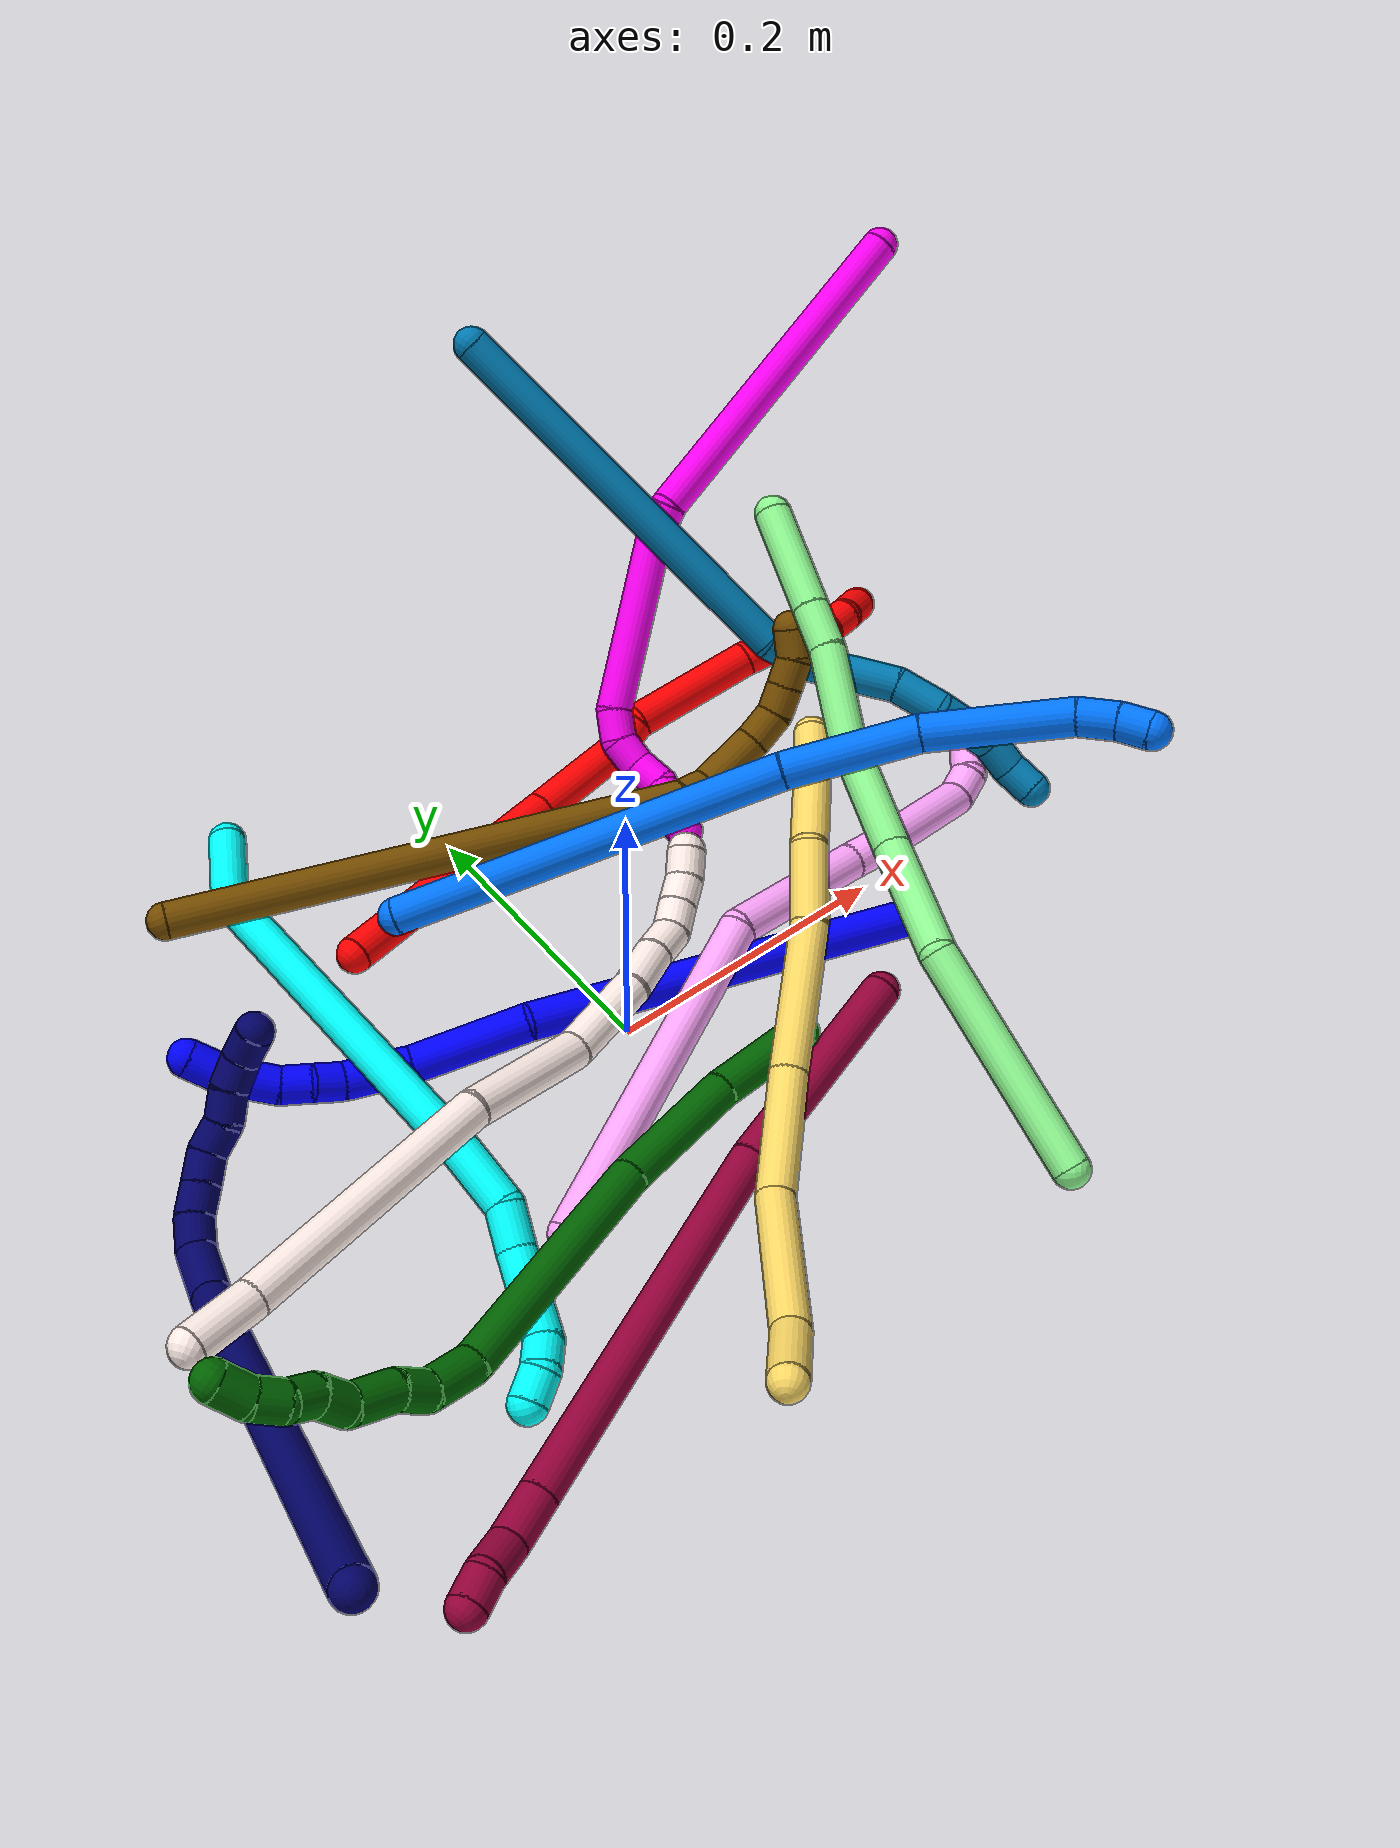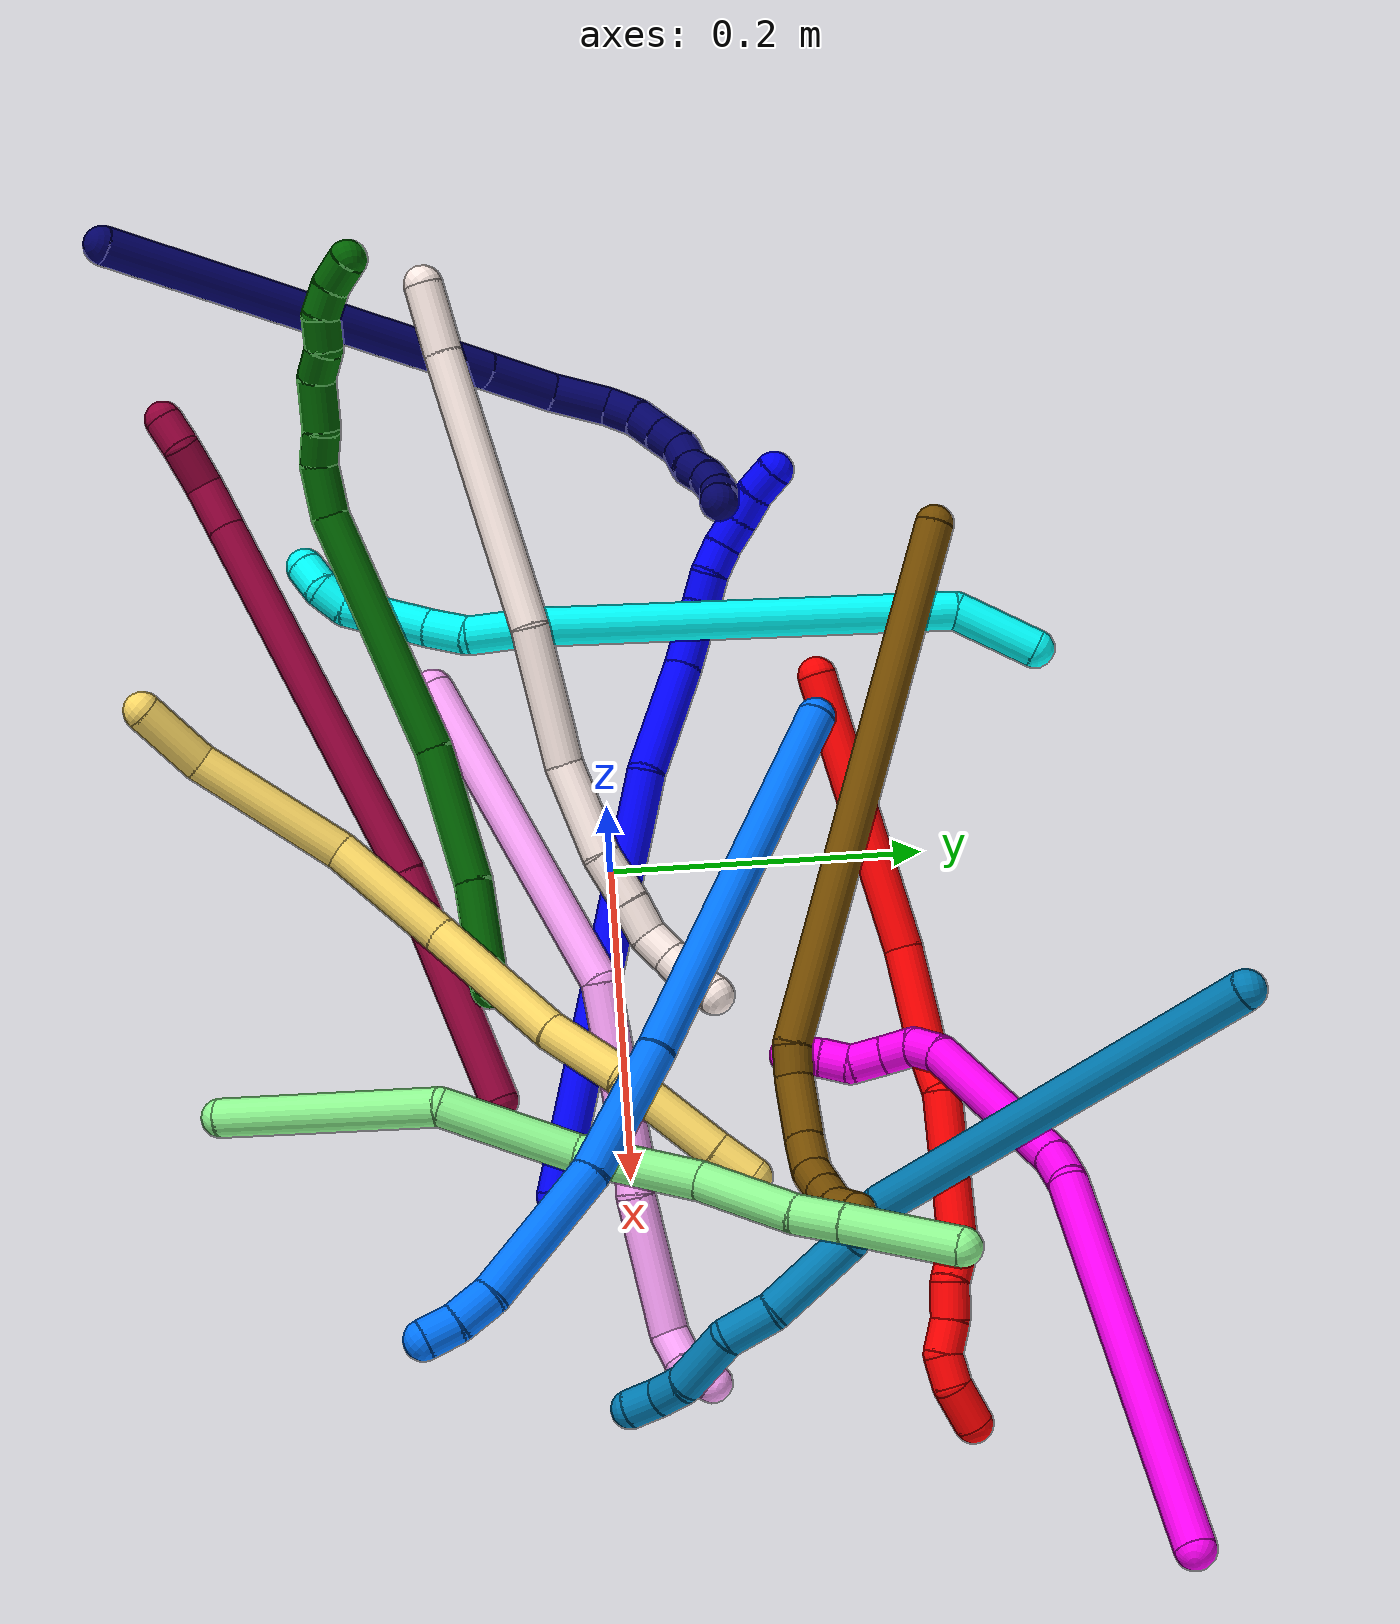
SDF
<sdf version="1.7">
 <world name="default">
  <plugin name="TubeGeneratorPlugin" filename="libtube_generator_plugin.so"/>
  <model name="photoneo_s_sensor">
   <static>1</static>
   <pose>0 0 2 1.57079 1.57079 3.14159</pose>
   <link name="link">
    <inertial><mass>0.1</mass></inertial>
    <sensor name="sensor" type="depth">
     <update_rate>30</update_rate>
     <camera>
      <horizontal_fov>1.22</horizontal_fov>
      <image><width>1920</width><height>1200</height><format>B8G8R8</format></image>
      <clip><near>0.1</near><far>4</far></clip>
      <depth_camera><output>points</output></depth_camera>
     </camera>
     <plugin name="camera_plugin" filename="libgazebo_ros_depth_camera.so">
      <baseline>0.2</baseline>
      <alwaysOn>1</alwaysOn>
      <updateRate>0.0</updateRate>
      <cameraName>camera_ir</cameraName>
      <imageTopicName>/camera/color/image_raw</imageTopicName>
      <cameraInfoTopicName>/camera/color/camera_info</cameraInfoTopicName>
      <depthImageTopicName>/camera/depth/image_raw</depthImageTopicName>
      <depthImageCameraInfoTopicName>/camera/depth/camera_info</depthImageCameraInfoTopicName>
      <pointCloudTopicName>/camera/depth/points</pointCloudTopicName>
      <frameName>fr_optical</frameName>
      <pointCloudCutoff>0.1</pointCloudCutoff>
      <pointCloudCutoffMax>2.0</pointCloudCutoffMax>
      <distortionK1>0</distortionK1>
      <distortionK2>0</distortionK2>
      <distortionK3>0</distortionK3>
      <distortionT1>0</distortionT1>
      <distortionT2>0</distortionT2>
      <CxPrime>0</CxPrime>
      <Cx>0</Cx>
      <Cy>0</Cy>
      <focalLength>0</focalLength>
      <hackBaseline>0</hackBaseline>
     </plugin>
    </sensor>
   </link>
  </model>
  <gravity>0 0 -9.8</gravity>
  <magnetic_field>6e-06 2.3e-05 -4.2e-05</magnetic_field>
  <atmosphere type="adiabatic"/>
  <physics name="default_physics" default="0" type="ode">
   <max_step_size>0.003</max_step_size>
   <real_time_factor>1</real_time_factor>
   <real_time_update_rate>1000</real_time_update_rate>
   <max_contacts>10000</max_contacts>
   <ode>
    <solver>
     <type>quick</type>
     <iters>100</iters>
     <sor>1.3</sor>
     <use_dynamic_moi_rescaling>0</use_dynamic_moi_rescaling>
    </solver>
    <constraints>
     <contact_max_correcting_vel>0</contact_max_correcting_vel>
     <contact_surface_layer>0.001</contact_surface_layer>
     <cfm>0</cfm>
     <erp>0.2</erp>
    </constraints>
   </ode>
  </physics>
  <scene><ambient>0.4 0.4 0.4 1</ambient><background>0.7 0.7 0.7 1</background><shadows>0</shadows></scene>
  <audio><device>default</device></audio>
  <spherical_coordinates>
   <surface_model>EARTH_WGS84</surface_model>
   <latitude_deg>0</latitude_deg>
   <longitude_deg>0</longitude_deg>
   <elevation>0</elevation>
   <heading_deg>0</heading_deg>
  </spherical_coordinates>
  <model name="bin">
   <static>1</static>
   <link name="bottom">
    <collision name="collision-bottom">
     <pose>0 0 -0.01 0 -0 0</pose>
     <geometry><box><size>0.8 0.6 0.02</size></box></geometry>
     <surface>
      <friction><ode><mu>100</mu><mu2>100</mu2></ode></friction>
      <contact><collide_bitmask>65535</collide_bitmask></contact>
     </surface>
    </collision>
   </link>
   <link name="west_wall">
    <collision name="collision-west_wall">
     <pose>-0.41 0 0.1 0 -0 0</pose>
     <geometry><box><size>0.02 0.6 0.2</size></box></geometry>
     <surface>
      <friction><ode><mu>100</mu><mu2>100</mu2></ode></friction>
      <contact><collide_bitmask>65535</collide_bitmask></contact>
     </surface>
    </collision>
   </link>
   <link name="east_wall">
    <collision name="collision-east_wall">
     <pose>0.41 0 0.1 0 -0 0</pose>
     <geometry><box><size>0.02 0.6 0.2</size></box></geometry>
     <surface>
      <friction><ode><mu>100</mu><mu2>100</mu2></ode></friction>
      <contact><collide_bitmask>65535</collide_bitmask></contact>
     </surface>
    </collision>
   </link>
   <link name="south_wall">
    <collision name="collision-south_wall">
     <pose>0 -0.31 0.1 0 -0 0</pose>
     <geometry><box><size>0.8 0.02 0.2</size></box></geometry>
     <surface>
      <friction><ode><mu>100</mu><mu2>100</mu2></ode></friction>
      <contact><collide_bitmask>65535</collide_bitmask></contact>
     </surface>
    </collision>
   </link>
   <link name="north_wall">
    <collision name="collision-north_wall">
     <pose>0 0.31 0.1 0 -0 0</pose>
     <geometry><box><size>0.8 0.02 0.2</size></box></geometry>
     <surface>
      <friction><ode><mu>100</mu><mu2>100</mu2></ode></friction>
      <contact><collide_bitmask>65535</collide_bitmask></contact>
     </surface>
    </collision>
   </link>
  </model>
  <model name="1">
   <static>0</static>
   <link name="1">
    <collision name="collision-cylinder-e_1_1_4">
     <pose>-0.122406 0.049401 0.041511 -0.871965 -1.08567 0.547983</pose>
     <geometry><cylinder><radius>0.0125</radius><length>0.276745</length></cylinder></geometry>
     <surface>
      <friction><ode><mu>1.16</mu><mu2>1.16</mu2><slip1>0</slip1><slip2>0</slip2></ode></friction>
      <contact><ode><kp>1e+06</kp><kd>1</kd><max_vel>0</max_vel><min_depth>0.001</min_depth></ode></contact>
     </surface>
    </collision>
    <visual name="visual-cylinder-e_1_1_4">
     <pose>-0.122406 0.049401 0.041511 -0.871965 -1.08567 0.547983</pose>
     <geometry><cylinder><radius>0.0125</radius><length>0.276745</length></cylinder></geometry>
     <material><ambient>0 0 1 1</ambient></material>
    </visual>
    <collision name="collision-cylinder-e_2_4_5">
     <pose>-0.282557 0.109242 0.084381 -1.44143 -1.29879 1.1763</pose>
     <geometry><cylinder><radius>0.0125</radius><length>0.07837</length></cylinder></geometry>
     <surface>
      <friction><ode><mu>1.16</mu><mu2>1.16</mu2><slip1>0</slip1><slip2>0</slip2></ode></friction>
      <contact><ode><kp>1e+06</kp><kd>1</kd><max_vel>0</max_vel><min_depth>0.001</min_depth></ode></contact>
     </surface>
    </collision>
    <visual name="visual-cylinder-e_2_4_5">
     <pose>-0.282557 0.109242 0.084381 -1.44143 -1.29879 1.1763</pose>
     <geometry><cylinder><radius>0.0125</radius><length>0.07837</length></cylinder></geometry>
     <material><ambient>0 0 1 1</ambient></material>
    </visual>
    <collision name="collision-cylinder-e_3_5_6">
     <pose>-0.331107 0.124428 0.088595 -1.02914 -1.09706 0.665299</pose>
     <geometry><cylinder><radius>0.0125</radius><length>0.024286</length></cylinder></geometry>
     <surface>
      <friction><ode><mu>1.16</mu><mu2>1.16</mu2><slip1>0</slip1><slip2>0</slip2></ode></friction>
      <contact><ode><kp>1e+06</kp><kd>1</kd><max_vel>0</max_vel><min_depth>0.001</min_depth></ode></contact>
     </surface>
    </collision>
    <visual name="visual-cylinder-e_3_5_6">
     <pose>-0.331107 0.124428 0.088595 -1.02914 -1.09706 0.665299</pose>
     <geometry><cylinder><radius>0.0125</radius><length>0.024286</length></cylinder></geometry>
     <material><ambient>0 0 1 1</ambient></material>
    </visual>
    <collision name="collision-cylinder-e_4_6_7">
     <pose>-0.351133 0.133119 0.093727 -1.04735 -1.11209 0.689091</pose>
     <geometry><cylinder><radius>0.0125</radius><length>0.020566</length></cylinder></geometry>
     <surface>
      <friction><ode><mu>1.16</mu><mu2>1.16</mu2><slip1>0</slip1><slip2>0</slip2></ode></friction>
      <contact><ode><kp>1e+06</kp><kd>1</kd><max_vel>0</max_vel><min_depth>0.001</min_depth></ode></contact>
     </surface>
    </collision>
    <visual name="visual-cylinder-e_4_6_7">
     <pose>-0.351133 0.133119 0.093727 -1.04735 -1.11209 0.689091</pose>
     <geometry><cylinder><radius>0.0125</radius><length>0.020566</length></cylinder></geometry>
     <material><ambient>0 0 1 1</ambient></material>
    </visual>
    <collision name="collision-cylinder-e_5_7_8">
     <pose>-0.367777 0.142401 0.100062 -0.920827 -0.836089 0.433714</pose>
     <geometry><cylinder><radius>0.0125</radius><length>0.020008</length></cylinder></geometry>
     <surface>
      <friction><ode><mu>1.16</mu><mu2>1.16</mu2><slip1>0</slip1><slip2>0</slip2></ode></friction>
      <contact><ode><kp>1e+06</kp><kd>1</kd><max_vel>0</max_vel><min_depth>0.001</min_depth></ode></contact>
     </surface>
    </collision>
    <visual name="visual-cylinder-e_5_7_8">
     <pose>-0.367777 0.142401 0.100062 -0.920827 -0.836089 0.433714</pose>
     <geometry><cylinder><radius>0.0125</radius><length>0.020008</length></cylinder></geometry>
     <material><ambient>0 0 1 1</ambient></material>
    </visual>
    <collision name="collision-cylinder-e_6_8_9">
     <pose>-0.38349 0.153088 0.105794 -1.26759 -0.976405 0.744258</pose>
     <geometry><cylinder><radius>0.0125</radius><length>0.020014</length></cylinder></geometry>
     <surface>
      <friction><ode><mu>1.16</mu><mu2>1.16</mu2><slip1>0</slip1><slip2>0</slip2></ode></friction>
      <contact><ode><kp>1e+06</kp><kd>1</kd><max_vel>0</max_vel><min_depth>0.001</min_depth></ode></contact>
     </surface>
    </collision>
    <visual name="visual-cylinder-e_6_8_9">
     <pose>-0.38349 0.153088 0.105794 -1.26759 -0.976405 0.744258</pose>
     <geometry><cylinder><radius>0.0125</radius><length>0.020014</length></cylinder></geometry>
     <material><ambient>0 0 1 1</ambient></material>
    </visual>
    <collision name="collision-cylinder-e_7_9_10">
     <pose>-0.398294 0.16575 0.109505 -1.29897 -0.709043 0.54805</pose>
     <geometry><cylinder><radius>0.0125</radius><length>0.020005</length></cylinder></geometry>
     <surface>
      <friction><ode><mu>1.16</mu><mu2>1.16</mu2><slip1>0</slip1><slip2>0</slip2></ode></friction>
      <contact><ode><kp>1e+06</kp><kd>1</kd><max_vel>0</max_vel><min_depth>0.001</min_depth></ode></contact>
     </surface>
    </collision>
    <visual name="visual-cylinder-e_7_9_10">
     <pose>-0.398294 0.16575 0.109505 -1.29897 -0.709043 0.54805</pose>
     <geometry><cylinder><radius>0.0125</radius><length>0.020005</length></cylinder></geometry>
     <material><ambient>0 0 1 1</ambient></material>
    </visual>
    <collision name="collision-cylinder-e_8_10_11">
     <pose>-0.410429 0.180727 0.114654 -1.1852 -0.597023 0.408593</pose>
     <geometry><cylinder><radius>0.0125</radius><length>0.020003</length></cylinder></geometry>
     <surface>
      <friction><ode><mu>1.16</mu><mu2>1.16</mu2><slip1>0</slip1><slip2>0</slip2></ode></friction>
      <contact><ode><kp>1e+06</kp><kd>1</kd><max_vel>0</max_vel><min_depth>0.001</min_depth></ode></contact>
     </surface>
    </collision>
    <visual name="visual-cylinder-e_8_10_11">
     <pose>-0.410429 0.180727 0.114654 -1.1852 -0.597023 0.408593</pose>
     <geometry><cylinder><radius>0.0125</radius><length>0.020003</length></cylinder></geometry>
     <material><ambient>0 0 1 1</ambient></material>
    </visual>
    <collision name="collision-cylinder-e_9_11_2">
     <pose>-0.4207 0.197068 0.119533 -1.36982 -0.48334 0.397356</pose>
     <geometry><cylinder><radius>0.0125</radius><length>0.020003</length></cylinder></geometry>
     <surface>
      <friction><ode><mu>1.16</mu><mu2>1.16</mu2><slip1>0</slip1><slip2>0</slip2></ode></friction>
      <contact><ode><kp>1e+06</kp><kd>1</kd><max_vel>0</max_vel><min_depth>0.001</min_depth></ode></contact>
     </surface>
    </collision>
    <visual name="visual-cylinder-e_9_11_2">
     <pose>-0.4207 0.197068 0.119533 -1.36982 -0.48334 0.397356</pose>
     <geometry><cylinder><radius>0.0125</radius><length>0.020003</length></cylinder></geometry>
     <material><ambient>0 0 1 1</ambient></material>
    </visual>
    <collision name="collision-sphere-2">
     <pose>-0.425348 0.205745 0.121301 0 -0 0</pose>
     <geometry><sphere><radius>0.0125</radius></sphere></geometry>
     <surface>
      <friction><ode><mu>1.16</mu><mu2>1.16</mu2><slip1>0</slip1><slip2>0</slip2></ode></friction>
      <contact><ode><kp>1e+06</kp><kd>1</kd><max_vel>0</max_vel><min_depth>0.001</min_depth></ode></contact>
     </surface>
    </collision>
    <visual name="visual-sphere-2">
     <pose>-0.425348 0.205745 0.121301 0 -0 0</pose>
     <geometry><sphere><radius>0.0125</radius></sphere></geometry>
     <material><ambient>0 0 1 1</ambient></material>
    </visual>
    <collision name="collision-sphere-11">
     <pose>-0.416051 0.18839 0.117765 0 -0 0</pose>
     <geometry><sphere><radius>0.0125</radius></sphere></geometry>
     <surface>
      <friction><ode><mu>1.16</mu><mu2>1.16</mu2><slip1>0</slip1><slip2>0</slip2></ode></friction>
      <contact><ode><kp>1e+06</kp><kd>1</kd><max_vel>0</max_vel><min_depth>0.001</min_depth></ode></contact>
     </surface>
    </collision>
    <visual name="visual-sphere-11">
     <pose>-0.416051 0.18839 0.117765 0 -0 0</pose>
     <geometry><sphere><radius>0.0125</radius></sphere></geometry>
     <material><ambient>0 0 1 1</ambient></material>
    </visual>
    <collision name="collision-sphere-10">
     <pose>-0.404806 0.173063 0.111543 0 -0 0</pose>
     <geometry><sphere><radius>0.0125</radius></sphere></geometry>
     <surface>
      <friction><ode><mu>1.16</mu><mu2>1.16</mu2><slip1>0</slip1><slip2>0</slip2></ode></friction>
      <contact><ode><kp>1e+06</kp><kd>1</kd><max_vel>0</max_vel><min_depth>0.001</min_depth></ode></contact>
     </surface>
    </collision>
    <visual name="visual-sphere-10">
     <pose>-0.404806 0.173063 0.111543 0 -0 0</pose>
     <geometry><sphere><radius>0.0125</radius></sphere></geometry>
     <material><ambient>0 0 1 1</ambient></material>
    </visual>
    <collision name="collision-sphere-9">
     <pose>-0.391781 0.158437 0.107467 0 -0 0</pose>
     <geometry><sphere><radius>0.0125</radius></sphere></geometry>
     <surface>
      <friction><ode><mu>1.16</mu><mu2>1.16</mu2><slip1>0</slip1><slip2>0</slip2></ode></friction>
      <contact><ode><kp>1e+06</kp><kd>1</kd><max_vel>0</max_vel><min_depth>0.001</min_depth></ode></contact>
     </surface>
    </collision>
    <visual name="visual-sphere-9">
     <pose>-0.391781 0.158437 0.107467 0 -0 0</pose>
     <geometry><sphere><radius>0.0125</radius></sphere></geometry>
     <material><ambient>0 0 1 1</ambient></material>
    </visual>
    <collision name="collision-sphere-4">
     <pose>-0.244813 0.098802 0.083023 0 -0 0</pose>
     <geometry><sphere><radius>0.0125</radius></sphere></geometry>
     <surface>
      <friction><ode><mu>1.16</mu><mu2>1.16</mu2><slip1>0</slip1><slip2>0</slip2></ode></friction>
      <contact><ode><kp>1e+06</kp><kd>1</kd><max_vel>0</max_vel><min_depth>0.001</min_depth></ode></contact>
     </surface>
    </collision>
    <visual name="visual-sphere-4">
     <pose>-0.244813 0.098802 0.083023 0 -0 0</pose>
     <geometry><sphere><radius>0.0125</radius></sphere></geometry>
     <material><ambient>0 0 1 1</ambient></material>
    </visual>
    <collision name="collision-sphere-1">
     <geometry><sphere><radius>0.0125</radius></sphere></geometry>
     <surface>
      <friction><ode><mu>1.16</mu><mu2>1.16</mu2><slip1>0</slip1><slip2>0</slip2></ode></friction>
      <contact><ode><kp>1e+06</kp><kd>1</kd><max_vel>0</max_vel><min_depth>0.001</min_depth></ode></contact>
     </surface>
    </collision>
    <visual name="visual-sphere-1">
     <geometry><sphere><radius>0.0125</radius></sphere></geometry>
     <material><ambient>0 0 1 1</ambient></material>
    </visual>
    <collision name="collision-sphere-8">
     <pose>-0.3752 0.14774 0.10412 0 -0 0</pose>
     <geometry><sphere><radius>0.0125</radius></sphere></geometry>
     <surface>
      <friction><ode><mu>1.16</mu><mu2>1.16</mu2><slip1>0</slip1><slip2>0</slip2></ode></friction>
      <contact><ode><kp>1e+06</kp><kd>1</kd><max_vel>0</max_vel><min_depth>0.001</min_depth></ode></contact>
     </surface>
    </collision>
    <visual name="visual-sphere-8">
     <pose>-0.3752 0.14774 0.10412 0 -0 0</pose>
     <geometry><sphere><radius>0.0125</radius></sphere></geometry>
     <material><ambient>0 0 1 1</ambient></material>
    </visual>
    <collision name="collision-sphere-5">
     <pose>-0.320302 0.119681 0.085739 0 -0 0</pose>
     <geometry><sphere><radius>0.0125</radius></sphere></geometry>
     <surface>
      <friction><ode><mu>1.16</mu><mu2>1.16</mu2><slip1>0</slip1><slip2>0</slip2></ode></friction>
      <contact><ode><kp>1e+06</kp><kd>1</kd><max_vel>0</max_vel><min_depth>0.001</min_depth></ode></contact>
     </surface>
    </collision>
    <visual name="visual-sphere-5">
     <pose>-0.320302 0.119681 0.085739 0 -0 0</pose>
     <geometry><sphere><radius>0.0125</radius></sphere></geometry>
     <material><ambient>0 0 1 1</ambient></material>
    </visual>
    <collision name="collision-sphere-6">
     <pose>-0.341913 0.129175 0.091451 0 -0 0</pose>
     <geometry><sphere><radius>0.0125</radius></sphere></geometry>
     <surface>
      <friction><ode><mu>1.16</mu><mu2>1.16</mu2><slip1>0</slip1><slip2>0</slip2></ode></friction>
      <contact><ode><kp>1e+06</kp><kd>1</kd><max_vel>0</max_vel><min_depth>0.001</min_depth></ode></contact>
     </surface>
    </collision>
    <visual name="visual-sphere-6">
     <pose>-0.341913 0.129175 0.091451 0 -0 0</pose>
     <geometry><sphere><radius>0.0125</radius></sphere></geometry>
     <material><ambient>0 0 1 1</ambient></material>
    </visual>
    <collision name="collision-sphere-7">
     <pose>-0.360354 0.137062 0.096003 0 -0 0</pose>
     <geometry><sphere><radius>0.0125</radius></sphere></geometry>
     <surface>
      <friction><ode><mu>1.16</mu><mu2>1.16</mu2><slip1>0</slip1><slip2>0</slip2></ode></friction>
      <contact><ode><kp>1e+06</kp><kd>1</kd><max_vel>0</max_vel><min_depth>0.001</min_depth></ode></contact>
     </surface>
    </collision>
    <visual name="visual-sphere-7">
     <pose>-0.360354 0.137062 0.096003 0 -0 0</pose>
     <geometry><sphere><radius>0.0125</radius></sphere></geometry>
     <material><ambient>0 0 1 1</ambient></material>
    </visual>
    <inertial>
     <pose>-0.221817 0.089556 0.066349 0 -0 0</pose>
     <mass>0.5</mass>
     <inertia>
      <ixx>0.001131</ixx>
      <ixy>0</ixy>
      <ixz>0</ixz>
      <iyy>0.002113</iyy>
      <iyz>0</iyz>
      <izz>0.000979</izz>
     </inertia>
    </inertial>
   </link>
   <pose>0.208085 -0.048132 0.012369 0.690896 -0.420688 -0.190544</pose>
  </model>
  <model name="2">
   <static>0</static>
   <link name="2">
    <collision name="collision-cylinder-e_1_1_4">
     <pose>0.003264 0.012116 0.091276 -0.131971 0.035439 -0.002342</pose>
     <geometry><cylinder><radius>0.0125</radius><length>0.184268</length></cylinder></geometry>
     <surface>
      <friction><ode><mu>1.16</mu><mu2>1.16</mu2><slip1>0</slip1><slip2>0</slip2></ode></friction>
      <contact><ode><kp>1e+06</kp><kd>1</kd><max_vel>0</max_vel><min_depth>0.001</min_depth></ode></contact>
     </surface>
    </collision>
    <visual name="visual-cylinder-e_1_1_4">
     <pose>0.003264 0.012116 0.091276 -0.131971 0.035439 -0.002342</pose>
     <geometry><cylinder><radius>0.0125</radius><length>0.184268</length></cylinder></geometry>
     <material><ambient>1 0 0 1</ambient></material>
    </visual>
    <collision name="collision-cylinder-e_2_4_5">
     <pose>0.010001 0.02385 0.218422 0.010653 0.096491 0.000514</pose>
     <geometry><cylinder><radius>0.0125</radius><length>0.072081</length></cylinder></geometry>
     <surface>
      <friction><ode><mu>1.16</mu><mu2>1.16</mu2><slip1>0</slip1><slip2>0</slip2></ode></friction>
      <contact><ode><kp>1e+06</kp><kd>1</kd><max_vel>0</max_vel><min_depth>0.001</min_depth></ode></contact>
     </surface>
    </collision>
    <visual name="visual-cylinder-e_2_4_5">
     <pose>0.010001 0.02385 0.218422 0.010653 0.096491 0.000514</pose>
     <geometry><cylinder><radius>0.0125</radius><length>0.072081</length></cylinder></geometry>
     <material><ambient>1 0 0 1</ambient></material>
    </visual>
    <collision name="collision-cylinder-e_3_5_6">
     <pose>0.013192 0.01867 0.266925 0.36296 -0.020839 -0.003824</pose>
     <geometry><cylinder><radius>0.0125</radius><length>0.027033</length></cylinder></geometry>
     <surface>
      <friction><ode><mu>1.16</mu><mu2>1.16</mu2><slip1>0</slip1><slip2>0</slip2></ode></friction>
      <contact><ode><kp>1e+06</kp><kd>1</kd><max_vel>0</max_vel><min_depth>0.001</min_depth></ode></contact>
     </surface>
    </collision>
    <visual name="visual-cylinder-e_3_5_6">
     <pose>0.013192 0.01867 0.266925 0.36296 -0.020839 -0.003824</pose>
     <geometry><cylinder><radius>0.0125</radius><length>0.027033</length></cylinder></geometry>
     <material><ambient>1 0 0 1</ambient></material>
    </visual>
    <collision name="collision-cylinder-e_4_6_7">
     <pose>0.0241 0.01379 0.327628 0.001722 0.228706 0.000198</pose>
     <geometry><cylinder><radius>0.0125</radius><length>0.098709</length></cylinder></geometry>
     <surface>
      <friction><ode><mu>1.16</mu><mu2>1.16</mu2><slip1>0</slip1><slip2>0</slip2></ode></friction>
      <contact><ode><kp>1e+06</kp><kd>1</kd><max_vel>0</max_vel><min_depth>0.001</min_depth></ode></contact>
     </surface>
    </collision>
    <visual name="visual-cylinder-e_4_6_7">
     <pose>0.0241 0.01379 0.327628 0.001722 0.228706 0.000198</pose>
     <geometry><cylinder><radius>0.0125</radius><length>0.098709</length></cylinder></geometry>
     <material><ambient>1 0 0 1</ambient></material>
    </visual>
    <collision name="collision-cylinder-e_5_7_8">
     <pose>0.04103 0.009682 0.385343 0.395271 0.502269 0.102658</pose>
     <geometry><cylinder><radius>0.0125</radius><length>0.023849</length></cylinder></geometry>
     <surface>
      <friction><ode><mu>1.16</mu><mu2>1.16</mu2><slip1>0</slip1><slip2>0</slip2></ode></friction>
      <contact><ode><kp>1e+06</kp><kd>1</kd><max_vel>0</max_vel><min_depth>0.001</min_depth></ode></contact>
     </surface>
    </collision>
    <visual name="visual-cylinder-e_5_7_8">
     <pose>0.04103 0.009682 0.385343 0.395271 0.502269 0.102658</pose>
     <geometry><cylinder><radius>0.0125</radius><length>0.023849</length></cylinder></geometry>
     <material><ambient>1 0 0 1</ambient></material>
    </visual>
    <collision name="collision-cylinder-e_6_8_9">
     <pose>0.05057 0.00641 0.406074 -0.067798 0.3295 -0.011276</pose>
     <geometry><cylinder><radius>0.0125</radius><length>0.023485</length></cylinder></geometry>
     <surface>
      <friction><ode><mu>1.16</mu><mu2>1.16</mu2><slip1>0</slip1><slip2>0</slip2></ode></friction>
      <contact><ode><kp>1e+06</kp><kd>1</kd><max_vel>0</max_vel><min_depth>0.001</min_depth></ode></contact>
     </surface>
    </collision>
    <visual name="visual-cylinder-e_6_8_9">
     <pose>0.05057 0.00641 0.406074 -0.067798 0.3295 -0.011276</pose>
     <geometry><cylinder><radius>0.0125</radius><length>0.023485</length></cylinder></geometry>
     <material><ambient>1 0 0 1</ambient></material>
    </visual>
    <collision name="collision-cylinder-e_7_9_10">
     <pose>0.059979 0.006975 0.426398 0.020373 0.54558 0.0057</pose>
     <geometry><cylinder><radius>0.0125</radius><length>0.021622</length></cylinder></geometry>
     <surface>
      <friction><ode><mu>1.16</mu><mu2>1.16</mu2><slip1>0</slip1><slip2>0</slip2></ode></friction>
      <contact><ode><kp>1e+06</kp><kd>1</kd><max_vel>0</max_vel><min_depth>0.001</min_depth></ode></contact>
     </surface>
    </collision>
    <visual name="visual-cylinder-e_7_9_10">
     <pose>0.059979 0.006975 0.426398 0.020373 0.54558 0.0057</pose>
     <geometry><cylinder><radius>0.0125</radius><length>0.021622</length></cylinder></geometry>
     <material><ambient>1 0 0 1</ambient></material>
    </visual>
    <collision name="collision-cylinder-e_8_10_11">
     <pose>0.066096 0.008377 0.445689 -0.156956 0.049805 -0.003917</pose>
     <geometry><cylinder><radius>0.0125</radius><length>0.020378</length></cylinder></geometry>
     <surface>
      <friction><ode><mu>1.16</mu><mu2>1.16</mu2><slip1>0</slip1><slip2>0</slip2></ode></friction>
      <contact><ode><kp>1e+06</kp><kd>1</kd><max_vel>0</max_vel><min_depth>0.001</min_depth></ode></contact>
     </surface>
    </collision>
    <visual name="visual-cylinder-e_8_10_11">
     <pose>0.066096 0.008377 0.445689 -0.156956 0.049805 -0.003917</pose>
     <geometry><cylinder><radius>0.0125</radius><length>0.020378</length></cylinder></geometry>
     <material><ambient>1 0 0 1</ambient></material>
    </visual>
    <collision name="collision-cylinder-e_9_11_2">
     <pose>0.064581 0.016576 0.468246 -0.486149 -0.14205 0.035281</pose>
     <geometry><cylinder><radius>0.0125</radius><length>0.028576</length></cylinder></geometry>
     <surface>
      <friction><ode><mu>1.16</mu><mu2>1.16</mu2><slip1>0</slip1><slip2>0</slip2></ode></friction>
      <contact><ode><kp>1e+06</kp><kd>1</kd><max_vel>0</max_vel><min_depth>0.001</min_depth></ode></contact>
     </surface>
    </collision>
    <visual name="visual-cylinder-e_9_11_2">
     <pose>0.064581 0.016576 0.468246 -0.486149 -0.14205 0.035281</pose>
     <geometry><cylinder><radius>0.0125</radius><length>0.028576</length></cylinder></geometry>
     <material><ambient>1 0 0 1</ambient></material>
    </visual>
    <collision name="collision-sphere-2">
     <pose>0.062558 0.023185 0.480751 0 -0 0</pose>
     <geometry><sphere><radius>0.0125</radius></sphere></geometry>
     <surface>
      <friction><ode><mu>1.16</mu><mu2>1.16</mu2><slip1>0</slip1><slip2>0</slip2></ode></friction>
      <contact><ode><kp>1e+06</kp><kd>1</kd><max_vel>0</max_vel><min_depth>0.001</min_depth></ode></contact>
     </surface>
    </collision>
    <visual name="visual-sphere-2">
     <pose>0.062558 0.023185 0.480751 0 -0 0</pose>
     <geometry><sphere><radius>0.0125</radius></sphere></geometry>
     <material><ambient>1 0 0 1</ambient></material>
    </visual>
    <collision name="collision-sphere-11">
     <pose>0.066604 0.009968 0.455741 0 -0 0</pose>
     <geometry><sphere><radius>0.0125</radius></sphere></geometry>
     <surface>
      <friction><ode><mu>1.16</mu><mu2>1.16</mu2><slip1>0</slip1><slip2>0</slip2></ode></friction>
      <contact><ode><kp>1e+06</kp><kd>1</kd><max_vel>0</max_vel><min_depth>0.001</min_depth></ode></contact>
     </surface>
    </collision>
    <visual name="visual-sphere-11">
     <pose>0.066604 0.009968 0.455741 0 -0 0</pose>
     <geometry><sphere><radius>0.0125</radius></sphere></geometry>
     <material><ambient>1 0 0 1</ambient></material>
    </visual>
    <collision name="collision-sphere-10">
     <pose>0.065589 0.006786 0.435638 0 -0 0</pose>
     <geometry><sphere><radius>0.0125</radius></sphere></geometry>
     <surface>
      <friction><ode><mu>1.16</mu><mu2>1.16</mu2><slip1>0</slip1><slip2>0</slip2></ode></friction>
      <contact><ode><kp>1e+06</kp><kd>1</kd><max_vel>0</max_vel><min_depth>0.001</min_depth></ode></contact>
     </surface>
    </collision>
    <visual name="visual-sphere-10">
     <pose>0.065589 0.006786 0.435638 0 -0 0</pose>
     <geometry><sphere><radius>0.0125</radius></sphere></geometry>
     <material><ambient>1 0 0 1</ambient></material>
    </visual>
    <collision name="collision-sphere-9">
     <pose>0.054369 0.007163 0.417159 0 -0 0</pose>
     <geometry><sphere><radius>0.0125</radius></sphere></geometry>
     <surface>
      <friction><ode><mu>1.16</mu><mu2>1.16</mu2><slip1>0</slip1><slip2>0</slip2></ode></friction>
      <contact><ode><kp>1e+06</kp><kd>1</kd><max_vel>0</max_vel><min_depth>0.001</min_depth></ode></contact>
     </surface>
    </collision>
    <visual name="visual-sphere-9">
     <pose>0.054369 0.007163 0.417159 0 -0 0</pose>
     <geometry><sphere><radius>0.0125</radius></sphere></geometry>
     <material><ambient>1 0 0 1</ambient></material>
    </visual>
    <collision name="collision-sphere-4">
     <pose>0.006529 0.024232 0.182551 0 -0 0</pose>
     <geometry><sphere><radius>0.0125</radius></sphere></geometry>
     <surface>
      <friction><ode><mu>1.16</mu><mu2>1.16</mu2><slip1>0</slip1><slip2>0</slip2></ode></friction>
      <contact><ode><kp>1e+06</kp><kd>1</kd><max_vel>0</max_vel><min_depth>0.001</min_depth></ode></contact>
     </surface>
    </collision>
    <visual name="visual-sphere-4">
     <pose>0.006529 0.024232 0.182551 0 -0 0</pose>
     <geometry><sphere><radius>0.0125</radius></sphere></geometry>
     <material><ambient>1 0 0 1</ambient></material>
    </visual>
    <collision name="collision-sphere-1">
     <geometry><sphere><radius>0.0125</radius></sphere></geometry>
     <surface>
      <friction><ode><mu>1.16</mu><mu2>1.16</mu2><slip1>0</slip1><slip2>0</slip2></ode></friction>
      <contact><ode><kp>1e+06</kp><kd>1</kd><max_vel>0</max_vel><min_depth>0.001</min_depth></ode></contact>
     </surface>
    </collision>
    <visual name="visual-sphere-1">
     <geometry><sphere><radius>0.0125</radius></sphere></geometry>
     <material><ambient>1 0 0 1</ambient></material>
    </visual>
    <collision name="collision-sphere-8">
     <pose>0.04677 0.005658 0.394989 0 -0 0</pose>
     <geometry><sphere><radius>0.0125</radius></sphere></geometry>
     <surface>
      <friction><ode><mu>1.16</mu><mu2>1.16</mu2><slip1>0</slip1><slip2>0</slip2></ode></friction>
      <contact><ode><kp>1e+06</kp><kd>1</kd><max_vel>0</max_vel><min_depth>0.001</min_depth></ode></contact>
     </surface>
    </collision>
    <visual name="visual-sphere-8">
     <pose>0.04677 0.005658 0.394989 0 -0 0</pose>
     <geometry><sphere><radius>0.0125</radius></sphere></geometry>
     <material><ambient>1 0 0 1</ambient></material>
    </visual>
    <collision name="collision-sphere-5">
     <pose>0.013473 0.023468 0.254292 0 -0 0</pose>
     <geometry><sphere><radius>0.0125</radius></sphere></geometry>
     <surface>
      <friction><ode><mu>1.16</mu><mu2>1.16</mu2><slip1>0</slip1><slip2>0</slip2></ode></friction>
      <contact><ode><kp>1e+06</kp><kd>1</kd><max_vel>0</max_vel><min_depth>0.001</min_depth></ode></contact>
     </surface>
    </collision>
    <visual name="visual-sphere-5">
     <pose>0.013473 0.023468 0.254292 0 -0 0</pose>
     <geometry><sphere><radius>0.0125</radius></sphere></geometry>
     <material><ambient>1 0 0 1</ambient></material>
    </visual>
    <collision name="collision-sphere-6">
     <pose>0.01291 0.013872 0.279558 0 -0 0</pose>
     <geometry><sphere><radius>0.0125</radius></sphere></geometry>
     <surface>
      <friction><ode><mu>1.16</mu><mu2>1.16</mu2><slip1>0</slip1><slip2>0</slip2></ode></friction>
      <contact><ode><kp>1e+06</kp><kd>1</kd><max_vel>0</max_vel><min_depth>0.001</min_depth></ode></contact>
     </surface>
    </collision>
    <visual name="visual-sphere-6">
     <pose>0.01291 0.013872 0.279558 0 -0 0</pose>
     <geometry><sphere><radius>0.0125</radius></sphere></geometry>
     <material><ambient>1 0 0 1</ambient></material>
    </visual>
    <collision name="collision-sphere-7">
     <pose>0.035289 0.013707 0.375697 0 -0 0</pose>
     <geometry><sphere><radius>0.0125</radius></sphere></geometry>
     <surface>
      <friction><ode><mu>1.16</mu><mu2>1.16</mu2><slip1>0</slip1><slip2>0</slip2></ode></friction>
      <contact><ode><kp>1e+06</kp><kd>1</kd><max_vel>0</max_vel><min_depth>0.001</min_depth></ode></contact>
     </surface>
    </collision>
    <visual name="visual-sphere-7">
     <pose>0.035289 0.013707 0.375697 0 -0 0</pose>
     <geometry><sphere><radius>0.0125</radius></sphere></geometry>
     <material><ambient>1 0 0 1</ambient></material>
    </visual>
    <inertial>
     <pose>0.021426 0.013988 0.245055 0 -0 0</pose>
     <mass>0.5</mass>
     <inertia>
      <ixx>0.00066</ixx>
      <ixy>0</ixy>
      <ixz>0</ixz>
      <iyy>0.000655</iyy>
      <iyz>0</iyz>
      <izz>-7.5e-05</izz>
     </inertia>
    </inertial>
   </link>
   <pose>-0.113829 0.140556 0.02774 -1.52259 0.159757 -1.31581</pose>
  </model>
  <model name="3">
   <static>0</static>
   <link name="3">
    <collision name="collision-cylinder-e_1_1_4">
     <pose>-0.00414 -0.028111 0.002272 1.49016 -0.145767 -0.134498</pose>
     <geometry><cylinder><radius>0.0125</radius><length>0.05701</length></cylinder></geometry>
     <surface>
      <friction><ode><mu>1.16</mu><mu2>1.16</mu2><slip1>0</slip1><slip2>0</slip2></ode></friction>
      <contact><ode><kp>1e+06</kp><kd>1</kd><max_vel>0</max_vel><min_depth>0.001</min_depth></ode></contact>
     </surface>
    </collision>
    <visual name="visual-cylinder-e_1_1_4">
     <pose>-0.00414 -0.028111 0.002272 1.49016 -0.145767 -0.134498</pose>
     <geometry><cylinder><radius>0.0125</radius><length>0.05701</length></cylinder></geometry>
     <material><ambient>0.003922 1 0.996078 1</ambient></material>
    </visual>
    <collision name="collision-cylinder-e_2_4_5">
     <pose>-0.009062 -0.171086 0.077737 1.00345 -0.005733 -0.003145</pose>
     <geometry><cylinder><radius>0.0125</radius><length>0.272408</length></cylinder></geometry>
     <surface>
      <friction><ode><mu>1.16</mu><mu2>1.16</mu2><slip1>0</slip1><slip2>0</slip2></ode></friction>
      <contact><ode><kp>1e+06</kp><kd>1</kd><max_vel>0</max_vel><min_depth>0.001</min_depth></ode></contact>
     </surface>
    </collision>
    <visual name="visual-cylinder-e_2_4_5">
     <pose>-0.009062 -0.171086 0.077737 1.00345 -0.005733 -0.003145</pose>
     <geometry><cylinder><radius>0.0125</radius><length>0.272408</length></cylinder></geometry>
     <material><ambient>0.003922 1 0.996078 1</ambient></material>
    </visual>
    <collision name="collision-cylinder-e_3_5_6">
     <pose>-0.004405 -0.304496 0.161168 1.06647 0.251274 0.14883</pose>
     <geometry><cylinder><radius>0.0125</radius><length>0.043743</length></cylinder></geometry>
     <surface>
      <friction><ode><mu>1.16</mu><mu2>1.16</mu2><slip1>0</slip1><slip2>0</slip2></ode></friction>
      <contact><ode><kp>1e+06</kp><kd>1</kd><max_vel>0</max_vel><min_depth>0.001</min_depth></ode></contact>
     </surface>
    </collision>
    <visual name="visual-cylinder-e_3_5_6">
     <pose>-0.004405 -0.304496 0.161168 1.06647 0.251274 0.14883</pose>
     <geometry><cylinder><radius>0.0125</radius><length>0.043743</length></cylinder></geometry>
     <material><ambient>0.003922 1 0.996078 1</ambient></material>
    </visual>
    <collision name="collision-cylinder-e_4_6_7">
     <pose>0.005454 -0.336722 0.172442 1.49511 0.311737 0.289322</pose>
     <geometry><cylinder><radius>0.0125</radius><length>0.028825</length></cylinder></geometry>
     <surface>
      <friction><ode><mu>1.16</mu><mu2>1.16</mu2><slip1>0</slip1><slip2>0</slip2></ode></friction>
      <contact><ode><kp>1e+06</kp><kd>1</kd><max_vel>0</max_vel><min_depth>0.001</min_depth></ode></contact>
     </surface>
    </collision>
    <visual name="visual-cylinder-e_4_6_7">
     <pose>0.005454 -0.336722 0.172442 1.49511 0.311737 0.289322</pose>
     <geometry><cylinder><radius>0.0125</radius><length>0.028825</length></cylinder></geometry>
     <material><ambient>0.003922 1 0.996078 1</ambient></material>
    </visual>
    <collision name="collision-cylinder-e_5_7_8">
     <pose>0.013121 -0.378674 0.178064 1.41004 0.112875 0.096074</pose>
     <geometry><cylinder><radius>0.0125</radius><length>0.057653</length></cylinder></geometry>
     <surface>
      <friction><ode><mu>1.16</mu><mu2>1.16</mu2><slip1>0</slip1><slip2>0</slip2></ode></friction>
      <contact><ode><kp>1e+06</kp><kd>1</kd><max_vel>0</max_vel><min_depth>0.001</min_depth></ode></contact>
     </surface>
    </collision>
    <visual name="visual-cylinder-e_5_7_8">
     <pose>0.013121 -0.378674 0.178064 1.41004 0.112875 0.096074</pose>
     <geometry><cylinder><radius>0.0125</radius><length>0.057653</length></cylinder></geometry>
     <material><ambient>0.003922 1 0.996078 1</ambient></material>
    </visual>
    <collision name="collision-cylinder-e_6_8_9">
     <pose>0.014119 -0.416733 0.181472 1.69042 -0.224376 -0.252675</pose>
     <geometry><cylinder><radius>0.0125</radius><length>0.020219</length></cylinder></geometry>
     <surface>
      <friction><ode><mu>1.16</mu><mu2>1.16</mu2><slip1>0</slip1><slip2>0</slip2></ode></friction>
      <contact><ode><kp>1e+06</kp><kd>1</kd><max_vel>0</max_vel><min_depth>0.001</min_depth></ode></contact>
     </surface>
    </collision>
    <visual name="visual-cylinder-e_6_8_9">
     <pose>0.014119 -0.416733 0.181472 1.69042 -0.224376 -0.252675</pose>
     <geometry><cylinder><radius>0.0125</radius><length>0.020219</length></cylinder></geometry>
     <material><ambient>0.003922 1 0.996078 1</ambient></material>
    </visual>
    <collision name="collision-cylinder-e_7_9_2">
     <pose>0.012321 -0.435373 0.175519 2.06563 0.044891 0.075211</pose>
     <geometry><cylinder><radius>0.0125</radius><length>0.020142</length></cylinder></geometry>
     <surface>
      <friction><ode><mu>1.16</mu><mu2>1.16</mu2><slip1>0</slip1><slip2>0</slip2></ode></friction>
      <contact><ode><kp>1e+06</kp><kd>1</kd><max_vel>0</max_vel><min_depth>0.001</min_depth></ode></contact>
     </surface>
    </collision>
    <visual name="visual-cylinder-e_7_9_2">
     <pose>0.012321 -0.435373 0.175519 2.06563 0.044891 0.075211</pose>
     <geometry><cylinder><radius>0.0125</radius><length>0.020142</length></cylinder></geometry>
     <material><ambient>0.003922 1 0.996078 1</ambient></material>
    </visual>
    <collision name="collision-sphere-2">
     <pose>0.012773 -0.444227 0.170741 0 -0 0</pose>
     <geometry><sphere><radius>0.0125</radius></sphere></geometry>
     <surface>
      <friction><ode><mu>1.16</mu><mu2>1.16</mu2><slip1>0</slip1><slip2>0</slip2></ode></friction>
      <contact><ode><kp>1e+06</kp><kd>1</kd><max_vel>0</max_vel><min_depth>0.001</min_depth></ode></contact>
     </surface>
    </collision>
    <visual name="visual-sphere-2">
     <pose>0.012773 -0.444227 0.170741 0 -0 0</pose>
     <geometry><sphere><radius>0.0125</radius></sphere></geometry>
     <material><ambient>0.003922 1 0.996078 1</ambient></material>
    </visual>
    <collision name="collision-sphere-9">
     <pose>0.011869 -0.426519 0.180296 0 -0 0</pose>
     <geometry><sphere><radius>0.0125</radius></sphere></geometry>
     <surface>
      <friction><ode><mu>1.16</mu><mu2>1.16</mu2><slip1>0</slip1><slip2>0</slip2></ode></friction>
      <contact><ode><kp>1e+06</kp><kd>1</kd><max_vel>0</max_vel><min_depth>0.001</min_depth></ode></contact>
     </surface>
    </collision>
    <visual name="visual-sphere-9">
     <pose>0.011869 -0.426519 0.180296 0 -0 0</pose>
     <geometry><sphere><radius>0.0125</radius></sphere></geometry>
     <material><ambient>0.003922 1 0.996078 1</ambient></material>
    </visual>
    <collision name="collision-sphere-4">
     <pose>-0.008281 -0.056223 0.004543 0 -0 0</pose>
     <geometry><sphere><radius>0.0125</radius></sphere></geometry>
     <surface>
      <friction><ode><mu>1.16</mu><mu2>1.16</mu2><slip1>0</slip1><slip2>0</slip2></ode></friction>
      <contact><ode><kp>1e+06</kp><kd>1</kd><max_vel>0</max_vel><min_depth>0.001</min_depth></ode></contact>
     </surface>
    </collision>
    <visual name="visual-sphere-4">
     <pose>-0.008281 -0.056223 0.004543 0 -0 0</pose>
     <geometry><sphere><radius>0.0125</radius></sphere></geometry>
     <material><ambient>0.003922 1 0.996078 1</ambient></material>
    </visual>
    <collision name="collision-sphere-1">
     <geometry><sphere><radius>0.0125</radius></sphere></geometry>
     <surface>
      <friction><ode><mu>1.16</mu><mu2>1.16</mu2><slip1>0</slip1><slip2>0</slip2></ode></friction>
      <contact><ode><kp>1e+06</kp><kd>1</kd><max_vel>0</max_vel><min_depth>0.001</min_depth></ode></contact>
     </surface>
    </collision>
    <visual name="visual-sphere-1">
     <geometry><sphere><radius>0.0125</radius></sphere></geometry>
     <material><ambient>0.003922 1 0.996078 1</ambient></material>
    </visual>
    <collision name="collision-sphere-8">
     <pose>0.016368 -0.406948 0.182649 0 -0 0</pose>
     <geometry><sphere><radius>0.0125</radius></sphere></geometry>
     <surface>
      <friction><ode><mu>1.16</mu><mu2>1.16</mu2><slip1>0</slip1><slip2>0</slip2></ode></friction>
      <contact><ode><kp>1e+06</kp><kd>1</kd><max_vel>0</max_vel><min_depth>0.001</min_depth></ode></contact>
     </surface>
    </collision>
    <visual name="visual-sphere-8">
     <pose>0.016368 -0.406948 0.182649 0 -0 0</pose>
     <geometry><sphere><radius>0.0125</radius></sphere></geometry>
     <material><ambient>0.003922 1 0.996078 1</ambient></material>
    </visual>
    <collision name="collision-sphere-5">
     <pose>-0.009843 -0.285949 0.150931 0 -0 0</pose>
     <geometry><sphere><radius>0.0125</radius></sphere></geometry>
     <surface>
      <friction><ode><mu>1.16</mu><mu2>1.16</mu2><slip1>0</slip1><slip2>0</slip2></ode></friction>
      <contact><ode><kp>1e+06</kp><kd>1</kd><max_vel>0</max_vel><min_depth>0.001</min_depth></ode></contact>
     </surface>
    </collision>
    <visual name="visual-sphere-5">
     <pose>-0.009843 -0.285949 0.150931 0 -0 0</pose>
     <geometry><sphere><radius>0.0125</radius></sphere></geometry>
     <material><ambient>0.003922 1 0.996078 1</ambient></material>
    </visual>
    <collision name="collision-sphere-6">
     <pose>0.001034 -0.323043 0.171405 0 -0 0</pose>
     <geometry><sphere><radius>0.0125</radius></sphere></geometry>
     <surface>
      <friction><ode><mu>1.16</mu><mu2>1.16</mu2><slip1>0</slip1><slip2>0</slip2></ode></friction>
      <contact><ode><kp>1e+06</kp><kd>1</kd><max_vel>0</max_vel><min_depth>0.001</min_depth></ode></contact>
     </surface>
    </collision>
    <visual name="visual-sphere-6">
     <pose>0.001034 -0.323043 0.171405 0 -0 0</pose>
     <geometry><sphere><radius>0.0125</radius></sphere></geometry>
     <material><ambient>0.003922 1 0.996078 1</ambient></material>
    </visual>
    <collision name="collision-sphere-7">
     <pose>0.009874 -0.3504 0.173479 0 -0 0</pose>
     <geometry><sphere><radius>0.0125</radius></sphere></geometry>
     <surface>
      <friction><ode><mu>1.16</mu><mu2>1.16</mu2><slip1>0</slip1><slip2>0</slip2></ode></friction>
      <contact><ode><kp>1e+06</kp><kd>1</kd><max_vel>0</max_vel><min_depth>0.001</min_depth></ode></contact>
     </surface>
    </collision>
    <visual name="visual-sphere-7">
     <pose>0.009874 -0.3504 0.173479 0 -0 0</pose>
     <geometry><sphere><radius>0.0125</radius></sphere></geometry>
     <material><ambient>0.003922 1 0.996078 1</ambient></material>
    </visual>
    <inertial>
     <pose>-0.0029 -0.22052 0.101593 0 -0 0</pose>
     <mass>0.5</mass>
     <inertia>
      <ixx>0.001741</ixx>
      <ixy>0</ixy>
      <ixz>0</ixz>
      <iyy>0.000881</iyy>
      <iyz>0</iyz>
      <izz>0.001499</izz>
     </inertia>
    </inertial>
   </link>
   <pose>-0.124534 0.28303 0.019312 0.333103 1.23944 -0.226459</pose>
  </model>
  <model name="4">
   <static>0</static>
   <link name="4">
    <collision name="collision-cylinder-e_1_1_4">
     <pose>0.038734 0.073724 0.080652 -0.740551 0.340659 -0.133333</pose>
     <geometry><cylinder><radius>0.0125</radius><length>0.231864</length></cylinder></geometry>
     <surface>
      <friction><ode><mu>1.16</mu><mu2>1.16</mu2><slip1>0</slip1><slip2>0</slip2></ode></friction>
      <contact><ode><kp>1e+06</kp><kd>1</kd><max_vel>0</max_vel><min_depth>0.001</min_depth></ode></contact>
     </surface>
    </collision>
    <visual name="visual-cylinder-e_1_1_4">
     <pose>0.038734 0.073724 0.080652 -0.740551 0.340659 -0.133333</pose>
     <geometry><cylinder><radius>0.0125</radius><length>0.231864</length></cylinder></geometry>
     <material><ambient>1 0.65098 0.996078 1</ambient></material>
    </visual>
    <collision name="collision-cylinder-e_2_4_5">
     <pose>0.108981 0.189998 0.176767 -1.22223 0.608088 -0.432761</pose>
     <geometry><cylinder><radius>0.0125</radius><length>0.110323</length></cylinder></geometry>
     <surface>
      <friction><ode><mu>1.16</mu><mu2>1.16</mu2><slip1>0</slip1><slip2>0</slip2></ode></friction>
      <contact><ode><kp>1e+06</kp><kd>1</kd><max_vel>0</max_vel><min_depth>0.001</min_depth></ode></contact>
     </surface>
    </collision>
    <visual name="visual-cylinder-e_2_4_5">
     <pose>0.108981 0.189998 0.176767 -1.22223 0.608088 -0.432761</pose>
     <geometry><cylinder><radius>0.0125</radius><length>0.110323</length></cylinder></geometry>
     <material><ambient>1 0.65098 0.996078 1</ambient></material>
    </visual>
    <collision name="collision-cylinder-e_3_5_6">
     <pose>0.149361 0.240576 0.196699 -1.06286 0.767655 -0.466179</pose>
     <geometry><cylinder><radius>0.0125</radius><length>0.025535</length></cylinder></geometry>
     <surface>
      <friction><ode><mu>1.16</mu><mu2>1.16</mu2><slip1>0</slip1><slip2>0</slip2></ode></friction>
      <contact><ode><kp>1e+06</kp><kd>1</kd><max_vel>0</max_vel><min_depth>0.001</min_depth></ode></contact>
     </surface>
    </collision>
    <visual name="visual-cylinder-e_3_5_6">
     <pose>0.149361 0.240576 0.196699 -1.06286 0.767655 -0.466179</pose>
     <geometry><cylinder><radius>0.0125</radius><length>0.025535</length></cylinder></geometry>
     <material><ambient>1 0.65098 0.996078 1</ambient></material>
    </visual>
    <collision name="collision-cylinder-e_4_6_7">
     <pose>0.181493 0.284481 0.213299 -1.2447 0.550854 -0.400101</pose>
     <geometry><cylinder><radius>0.0125</radius><length>0.088897</length></cylinder></geometry>
     <surface>
      <friction><ode><mu>1.16</mu><mu2>1.16</mu2><slip1>0</slip1><slip2>0</slip2></ode></friction>
      <contact><ode><kp>1e+06</kp><kd>1</kd><max_vel>0</max_vel><min_depth>0.001</min_depth></ode></contact>
     </surface>
    </collision>
    <visual name="visual-cylinder-e_4_6_7">
     <pose>0.181493 0.284481 0.213299 -1.2447 0.550854 -0.400101</pose>
     <geometry><cylinder><radius>0.0125</radius><length>0.088897</length></cylinder></geometry>
     <material><ambient>1 0.65098 0.996078 1</ambient></material>
    </visual>
    <collision name="collision-cylinder-e_5_7_8">
     <pose>0.208508 0.32636 0.23268 -0.691646 0.379238 -0.138082</pose>
     <geometry><cylinder><radius>0.0125</radius><length>0.02026</length></cylinder></geometry>
     <surface>
      <friction><ode><mu>1.16</mu><mu2>1.16</mu2><slip1>0</slip1><slip2>0</slip2></ode></friction>
      <contact><ode><kp>1e+06</kp><kd>1</kd><max_vel>0</max_vel><min_depth>0.001</min_depth></ode></contact>
     </surface>
    </collision>
    <visual name="visual-cylinder-e_5_7_8">
     <pose>0.208508 0.32636 0.23268 -0.691646 0.379238 -0.138082</pose>
     <geometry><cylinder><radius>0.0125</radius><length>0.02026</length></cylinder></geometry>
     <material><ambient>1 0.65098 0.996078 1</ambient></material>
    </visual>
    <collision name="collision-cylinder-e_6_8_2">
     <pose>0.211195 0.341542 0.246873 -0.923102 -0.092106 0.045836</pose>
     <geometry><cylinder><radius>0.0125</radius><length>0.023121</length></cylinder></geometry>
     <surface>
      <friction><ode><mu>1.16</mu><mu2>1.16</mu2><slip1>0</slip1><slip2>0</slip2></ode></friction>
      <contact><ode><kp>1e+06</kp><kd>1</kd><max_vel>0</max_vel><min_depth>0.001</min_depth></ode></contact>
     </surface>
    </collision>
    <visual name="visual-cylinder-e_6_8_2">
     <pose>0.211195 0.341542 0.246873 -0.923102 -0.092106 0.045836</pose>
     <geometry><cylinder><radius>0.0125</radius><length>0.023121</length></cylinder></geometry>
     <material><ambient>1 0.65098 0.996078 1</ambient></material>
    </visual>
    <collision name="collision-sphere-2">
     <pose>0.210132 0.350722 0.253818 0 -0 0</pose>
     <geometry><sphere><radius>0.0125</radius></sphere></geometry>
     <surface>
      <friction><ode><mu>1.16</mu><mu2>1.16</mu2><slip1>0</slip1><slip2>0</slip2></ode></friction>
      <contact><ode><kp>1e+06</kp><kd>1</kd><max_vel>0</max_vel><min_depth>0.001</min_depth></ode></contact>
     </surface>
    </collision>
    <visual name="visual-sphere-2">
     <pose>0.210132 0.350722 0.253818 0 -0 0</pose>
     <geometry><sphere><radius>0.0125</radius></sphere></geometry>
     <material><ambient>1 0.65098 0.996078 1</ambient></material>
    </visual>
    <collision name="collision-sphere-4">
     <pose>0.077468 0.147448 0.161304 0 -0 0</pose>
     <geometry><sphere><radius>0.0125</radius></sphere></geometry>
     <surface>
      <friction><ode><mu>1.16</mu><mu2>1.16</mu2><slip1>0</slip1><slip2>0</slip2></ode></friction>
      <contact><ode><kp>1e+06</kp><kd>1</kd><max_vel>0</max_vel><min_depth>0.001</min_depth></ode></contact>
     </surface>
    </collision>
    <visual name="visual-sphere-4">
     <pose>0.077468 0.147448 0.161304 0 -0 0</pose>
     <geometry><sphere><radius>0.0125</radius></sphere></geometry>
     <material><ambient>1 0.65098 0.996078 1</ambient></material>
    </visual>
    <collision name="collision-sphere-1">
     <geometry><sphere><radius>0.0125</radius></sphere></geometry>
     <surface>
      <friction><ode><mu>1.16</mu><mu2>1.16</mu2><slip1>0</slip1><slip2>0</slip2></ode></friction>
      <contact><ode><kp>1e+06</kp><kd>1</kd><max_vel>0</max_vel><min_depth>0.001</min_depth></ode></contact>
     </surface>
    </collision>
    <visual name="visual-sphere-1">
     <geometry><sphere><radius>0.0125</radius></sphere></geometry>
     <material><ambient>1 0.65098 0.996078 1</ambient></material>
    </visual>
    <collision name="collision-sphere-8">
     <pose>0.212258 0.332362 0.239927 0 -0 0</pose>
     <geometry><sphere><radius>0.0125</radius></sphere></geometry>
     <surface>
      <friction><ode><mu>1.16</mu><mu2>1.16</mu2><slip1>0</slip1><slip2>0</slip2></ode></friction>
      <contact><ode><kp>1e+06</kp><kd>1</kd><max_vel>0</max_vel><min_depth>0.001</min_depth></ode></contact>
     </surface>
    </collision>
    <visual name="visual-sphere-8">
     <pose>0.212258 0.332362 0.239927 0 -0 0</pose>
     <geometry><sphere><radius>0.0125</radius></sphere></geometry>
     <material><ambient>1 0.65098 0.996078 1</ambient></material>
    </visual>
    <collision name="collision-sphere-5">
     <pose>0.140495 0.232549 0.19223 0 -0 0</pose>
     <geometry><sphere><radius>0.0125</radius></sphere></geometry>
     <surface>
      <friction><ode><mu>1.16</mu><mu2>1.16</mu2><slip1>0</slip1><slip2>0</slip2></ode></friction>
      <contact><ode><kp>1e+06</kp><kd>1</kd><max_vel>0</max_vel><min_depth>0.001</min_depth></ode></contact>
     </surface>
    </collision>
    <visual name="visual-sphere-5">
     <pose>0.140495 0.232549 0.19223 0 -0 0</pose>
     <geometry><sphere><radius>0.0125</radius></sphere></geometry>
     <material><ambient>1 0.65098 0.996078 1</ambient></material>
    </visual>
    <collision name="collision-sphere-6">
     <pose>0.158228 0.248603 0.201167 0 -0 0</pose>
     <geometry><sphere><radius>0.0125</radius></sphere></geometry>
     <surface>
      <friction><ode><mu>1.16</mu><mu2>1.16</mu2><slip1>0</slip1><slip2>0</slip2></ode></friction>
      <contact><ode><kp>1e+06</kp><kd>1</kd><max_vel>0</max_vel><min_depth>0.001</min_depth></ode></contact>
     </surface>
    </collision>
    <visual name="visual-sphere-6">
     <pose>0.158228 0.248603 0.201167 0 -0 0</pose>
     <geometry><sphere><radius>0.0125</radius></sphere></geometry>
     <material><ambient>1 0.65098 0.996078 1</ambient></material>
    </visual>
    <collision name="collision-sphere-7">
     <pose>0.204758 0.320358 0.225432 0 -0 0</pose>
     <geometry><sphere><radius>0.0125</radius></sphere></geometry>
     <surface>
      <friction><ode><mu>1.16</mu><mu2>1.16</mu2><slip1>0</slip1><slip2>0</slip2></ode></friction>
      <contact><ode><kp>1e+06</kp><kd>1</kd><max_vel>0</max_vel><min_depth>0.001</min_depth></ode></contact>
     </surface>
    </collision>
    <visual name="visual-sphere-7">
     <pose>0.204758 0.320358 0.225432 0 -0 0</pose>
     <geometry><sphere><radius>0.0125</radius></sphere></geometry>
     <material><ambient>1 0.65098 0.996078 1</ambient></material>
    </visual>
    <inertial>
     <pose>0.100119 0.167993 0.145216 0 -0 0</pose>
     <mass>0.5</mass>
     <inertia>
      <ixx>0.000943</ixx>
      <ixy>0</ixy>
      <ixz>0</ixz>
      <iyy>0.000729</iyy>
      <iyz>0</iyz>
      <izz>-0.001241</izz>
     </inertia>
    </inertial>
   </link>
   <pose>-0.126403 -0.106135 0.011962 -0.647681 -0.063571 -0.805435</pose>
  </model>
  <model name="5">
   <static>0</static>
   <link name="5">
    <collision name="collision-cylinder-e_1_1_4">
     <pose>-0.003691 -0.006104 -0.023573 2.88822 -0.150417 -1.06843</pose>
     <geometry><cylinder><radius>0.0125</radius><length>0.049257</length></cylinder></geometry>
     <surface>
      <friction><ode><mu>1.16</mu><mu2>1.16</mu2><slip1>0</slip1><slip2>0</slip2></ode></friction>
      <contact><ode><kp>1e+06</kp><kd>1</kd><max_vel>0</max_vel><min_depth>0.001</min_depth></ode></contact>
     </surface>
    </collision>
    <visual name="visual-cylinder-e_1_1_4">
     <pose>-0.003691 -0.006104 -0.023573 2.88822 -0.150417 -1.06843</pose>
     <geometry><cylinder><radius>0.0125</radius><length>0.049257</length></cylinder></geometry>
     <material><ambient>1 0.858824 0.4 1</ambient></material>
    </visual>
    <collision name="collision-cylinder-e_2_4_5">
     <pose>-0.014434 -0.008838 -0.099311 -3.07708 -0.134116 2.2458</pose>
     <geometry><cylinder><radius>0.0125</radius><length>0.105497</length></cylinder></geometry>
     <surface>
      <friction><ode><mu>1.16</mu><mu2>1.16</mu2><slip1>0</slip1><slip2>0</slip2></ode></friction>
      <contact><ode><kp>1e+06</kp><kd>1</kd><max_vel>0</max_vel><min_depth>0.001</min_depth></ode></contact>
     </surface>
    </collision>
    <visual name="visual-cylinder-e_2_4_5">
     <pose>-0.014434 -0.008838 -0.099311 -3.07708 -0.134116 2.2458</pose>
     <geometry><cylinder><radius>0.0125</radius><length>0.105497</length></cylinder></geometry>
     <material><ambient>1 0.858824 0.4 1</ambient></material>
    </visual>
    <collision name="collision-cylinder-e_3_5_6">
     <pose>-0.015018 0.004647 -0.192981 -2.90255 0.150313 -1.12008</pose>
     <geometry><cylinder><radius>0.0125</radius><length>0.08641</length></cylinder></geometry>
     <surface>
      <friction><ode><mu>1.16</mu><mu2>1.16</mu2><slip1>0</slip1><slip2>0</slip2></ode></friction>
      <contact><ode><kp>1e+06</kp><kd>1</kd><max_vel>0</max_vel><min_depth>0.001</min_depth></ode></contact>
     </surface>
    </collision>
    <visual name="visual-cylinder-e_3_5_6">
     <pose>-0.015018 0.004647 -0.192981 -2.90255 0.150313 -1.12008</pose>
     <geometry><cylinder><radius>0.0125</radius><length>0.08641</length></cylinder></geometry>
     <material><ambient>1 0.858824 0.4 1</ambient></material>
    </visual>
    <collision name="collision-cylinder-e_4_6_7">
     <pose>0.00485 0.033464 -0.279424 -2.7472 0.268598 -1.18925</pose>
     <geometry><cylinder><radius>0.0125</radius><length>0.100973</length></cylinder></geometry>
     <surface>
      <friction><ode><mu>1.16</mu><mu2>1.16</mu2><slip1>0</slip1><slip2>0</slip2></ode></friction>
      <contact><ode><kp>1e+06</kp><kd>1</kd><max_vel>0</max_vel><min_depth>0.001</min_depth></ode></contact>
     </surface>
    </collision>
    <visual name="visual-cylinder-e_4_6_7">
     <pose>0.00485 0.033464 -0.279424 -2.7472 0.268598 -1.18925</pose>
     <geometry><cylinder><radius>0.0125</radius><length>0.100973</length></cylinder></geometry>
     <material><ambient>1 0.858824 0.4 1</ambient></material>
    </visual>
    <collision name="collision-cylinder-e_5_7_8">
     <pose>0.022345 0.064028 -0.3488 -2.68976 0.149686 -0.630705</pose>
     <geometry><cylinder><radius>0.0125</radius><length>0.05494</length></cylinder></geometry>
     <surface>
      <friction><ode><mu>1.16</mu><mu2>1.16</mu2><slip1>0</slip1><slip2>0</slip2></ode></friction>
      <contact><ode><kp>1e+06</kp><kd>1</kd><max_vel>0</max_vel><min_depth>0.001</min_depth></ode></contact>
     </surface>
    </collision>
    <visual name="visual-cylinder-e_5_7_8">
     <pose>0.022345 0.064028 -0.3488 -2.68976 0.149686 -0.630705</pose>
     <geometry><cylinder><radius>0.0125</radius><length>0.05494</length></cylinder></geometry>
     <material><ambient>1 0.858824 0.4 1</ambient></material>
    </visual>
    <collision name="collision-cylinder-e_6_8_9">
     <pose>0.028153 0.081507 -0.41018 -2.99063 0.045776 -0.587856</pose>
     <geometry><cylinder><radius>0.0125</radius><length>0.074814</length></cylinder></geometry>
     <surface>
      <friction><ode><mu>1.16</mu><mu2>1.16</mu2><slip1>0</slip1><slip2>0</slip2></ode></friction>
      <contact><ode><kp>1e+06</kp><kd>1</kd><max_vel>0</max_vel><min_depth>0.001</min_depth></ode></contact>
     </surface>
    </collision>
    <visual name="visual-cylinder-e_6_8_9">
     <pose>0.028153 0.081507 -0.41018 -2.99063 0.045776 -0.587856</pose>
     <geometry><cylinder><radius>0.0125</radius><length>0.074814</length></cylinder></geometry>
     <material><ambient>1 0.858824 0.4 1</ambient></material>
    </visual>
    <collision name="collision-cylinder-e_7_9_2">
     <pose>0.02964 0.088952 -0.461057 -3.01137 -0.016008 0.244301</pose>
     <geometry><cylinder><radius>0.0125</radius><length>0.028109</length></cylinder></geometry>
     <surface>
      <friction><ode><mu>1.16</mu><mu2>1.16</mu2><slip1>0</slip1><slip2>0</slip2></ode></friction>
      <contact><ode><kp>1e+06</kp><kd>1</kd><max_vel>0</max_vel><min_depth>0.001</min_depth></ode></contact>
     </surface>
    </collision>
    <visual name="visual-cylinder-e_7_9_2">
     <pose>0.02964 0.088952 -0.461057 -3.01137 -0.016008 0.244301</pose>
     <geometry><cylinder><radius>0.0125</radius><length>0.028109</length></cylinder></geometry>
     <material><ambient>1 0.858824 0.4 1</ambient></material>
    </visual>
    <collision name="collision-sphere-2">
     <pose>0.029415 0.090777 -0.47499 0 -0 0</pose>
     <geometry><sphere><radius>0.0125</radius></sphere></geometry>
     <surface>
      <friction><ode><mu>1.16</mu><mu2>1.16</mu2><slip1>0</slip1><slip2>0</slip2></ode></friction>
      <contact><ode><kp>1e+06</kp><kd>1</kd><max_vel>0</max_vel><min_depth>0.001</min_depth></ode></contact>
     </surface>
    </collision>
    <visual name="visual-sphere-2">
     <pose>0.029415 0.090777 -0.47499 0 -0 0</pose>
     <geometry><sphere><radius>0.0125</radius></sphere></geometry>
     <material><ambient>1 0.858824 0.4 1</ambient></material>
    </visual>
    <collision name="collision-sphere-9">
     <pose>0.029865 0.087127 -0.447123 0 -0 0</pose>
     <geometry><sphere><radius>0.0125</radius></sphere></geometry>
     <surface>
      <friction><ode><mu>1.16</mu><mu2>1.16</mu2><slip1>0</slip1><slip2>0</slip2></ode></friction>
      <contact><ode><kp>1e+06</kp><kd>1</kd><max_vel>0</max_vel><min_depth>0.001</min_depth></ode></contact>
     </surface>
    </collision>
    <visual name="visual-sphere-9">
     <pose>0.029865 0.087127 -0.447123 0 -0 0</pose>
     <geometry><sphere><radius>0.0125</radius></sphere></geometry>
     <material><ambient>1 0.858824 0.4 1</ambient></material>
    </visual>
    <collision name="collision-sphere-4">
     <pose>-0.007381 -0.012208 -0.047145 0 -0 0</pose>
     <geometry><sphere><radius>0.0125</radius></sphere></geometry>
     <surface>
      <friction><ode><mu>1.16</mu><mu2>1.16</mu2><slip1>0</slip1><slip2>0</slip2></ode></friction>
      <contact><ode><kp>1e+06</kp><kd>1</kd><max_vel>0</max_vel><min_depth>0.001</min_depth></ode></contact>
     </surface>
    </collision>
    <visual name="visual-sphere-4">
     <pose>-0.007381 -0.012208 -0.047145 0 -0 0</pose>
     <geometry><sphere><radius>0.0125</radius></sphere></geometry>
     <material><ambient>1 0.858824 0.4 1</ambient></material>
    </visual>
    <collision name="collision-sphere-1">
     <geometry><sphere><radius>0.0125</radius></sphere></geometry>
     <surface>
      <friction><ode><mu>1.16</mu><mu2>1.16</mu2><slip1>0</slip1><slip2>0</slip2></ode></friction>
      <contact><ode><kp>1e+06</kp><kd>1</kd><max_vel>0</max_vel><min_depth>0.001</min_depth></ode></contact>
     </surface>
    </collision>
    <visual name="visual-sphere-1">
     <geometry><sphere><radius>0.0125</radius></sphere></geometry>
     <material><ambient>1 0.858824 0.4 1</ambient></material>
    </visual>
    <collision name="collision-sphere-8">
     <pose>0.026442 0.075887 -0.373237 0 -0 0</pose>
     <geometry><sphere><radius>0.0125</radius></sphere></geometry>
     <surface>
      <friction><ode><mu>1.16</mu><mu2>1.16</mu2><slip1>0</slip1><slip2>0</slip2></ode></friction>
      <contact><ode><kp>1e+06</kp><kd>1</kd><max_vel>0</max_vel><min_depth>0.001</min_depth></ode></contact>
     </surface>
    </collision>
    <visual name="visual-sphere-8">
     <pose>0.026442 0.075887 -0.373237 0 -0 0</pose>
     <geometry><sphere><radius>0.0125</radius></sphere></geometry>
     <material><ambient>1 0.858824 0.4 1</ambient></material>
    </visual>
    <collision name="collision-sphere-5">
     <pose>-0.021488 -0.005468 -0.151477 0 -0 0</pose>
     <geometry><sphere><radius>0.0125</radius></sphere></geometry>
     <surface>
      <friction><ode><mu>1.16</mu><mu2>1.16</mu2><slip1>0</slip1><slip2>0</slip2></ode></friction>
      <contact><ode><kp>1e+06</kp><kd>1</kd><max_vel>0</max_vel><min_depth>0.001</min_depth></ode></contact>
     </surface>
    </collision>
    <visual name="visual-sphere-5">
     <pose>-0.021488 -0.005468 -0.151477 0 -0 0</pose>
     <geometry><sphere><radius>0.0125</radius></sphere></geometry>
     <material><ambient>1 0.858824 0.4 1</ambient></material>
    </visual>
    <collision name="collision-sphere-6">
     <pose>-0.008548 0.014761 -0.234484 0 -0 0</pose>
     <geometry><sphere><radius>0.0125</radius></sphere></geometry>
     <surface>
      <friction><ode><mu>1.16</mu><mu2>1.16</mu2><slip1>0</slip1><slip2>0</slip2></ode></friction>
      <contact><ode><kp>1e+06</kp><kd>1</kd><max_vel>0</max_vel><min_depth>0.001</min_depth></ode></contact>
     </surface>
    </collision>
    <visual name="visual-sphere-6">
     <pose>-0.008548 0.014761 -0.234484 0 -0 0</pose>
     <geometry><sphere><radius>0.0125</radius></sphere></geometry>
     <material><ambient>1 0.858824 0.4 1</ambient></material>
    </visual>
    <collision name="collision-sphere-7">
     <pose>0.018248 0.052168 -0.324363 0 -0 0</pose>
     <geometry><sphere><radius>0.0125</radius></sphere></geometry>
     <surface>
      <friction><ode><mu>1.16</mu><mu2>1.16</mu2><slip1>0</slip1><slip2>0</slip2></ode></friction>
      <contact><ode><kp>1e+06</kp><kd>1</kd><max_vel>0</max_vel><min_depth>0.001</min_depth></ode></contact>
     </surface>
    </collision>
    <visual name="visual-sphere-7">
     <pose>0.018248 0.052168 -0.324363 0 -0 0</pose>
     <geometry><sphere><radius>0.0125</radius></sphere></geometry>
     <material><ambient>1 0.858824 0.4 1</ambient></material>
    </visual>
    <inertial>
     <pose>0.003309 0.029327 -0.238676 0 -0 0</pose>
     <mass>0.5</mass>
     <inertia>
      <ixx>-4.3e-05</ixx>
      <ixy>0</ixy>
      <ixz>0</ixz>
      <iyy>-0.000115</iyy>
      <iyz>0</iyz>
      <izz>-0.000121</izz>
     </inertia>
    </inertial>
   </link>
   <pose>-0.109545 -0.287988 0.069973 1.37385 -0.497408 -0.668793</pose>
  </model>
  <model name="6">
   <static>0</static>
   <link name="6">
    <collision name="collision-cylinder-e_1_1_4">
     <pose>-0.010518 0.010585 0.031426 -0.324902 -0.307151 0.050729</pose>
     <geometry><cylinder><radius>0.0125</radius><length>0.069578</length></cylinder></geometry>
     <surface>
      <friction><ode><mu>1.16</mu><mu2>1.16</mu2><slip1>0</slip1><slip2>0</slip2></ode></friction>
      <contact><ode><kp>1e+06</kp><kd>1</kd><max_vel>0</max_vel><min_depth>0.001</min_depth></ode></contact>
     </surface>
    </collision>
    <visual name="visual-cylinder-e_1_1_4">
     <pose>-0.010518 0.010585 0.031426 -0.324902 -0.307151 0.050729</pose>
     <geometry><cylinder><radius>0.0125</radius><length>0.069578</length></cylinder></geometry>
     <material><ambient>0 0.392157 0.003922 1</ambient></material>
    </visual>
    <collision name="collision-cylinder-e_2_4_5">
     <pose>-0.02906 0.037333 0.103425 -0.379078 -0.181701 0.03495</pose>
     <geometry><cylinder><radius>0.0125</radius><length>0.088808</length></cylinder></geometry>
     <surface>
      <friction><ode><mu>1.16</mu><mu2>1.16</mu2><slip1>0</slip1><slip2>0</slip2></ode></friction>
      <contact><ode><kp>1e+06</kp><kd>1</kd><max_vel>0</max_vel><min_depth>0.001</min_depth></ode></contact>
     </surface>
    </collision>
    <visual name="visual-cylinder-e_2_4_5">
     <pose>-0.02906 0.037333 0.103425 -0.379078 -0.181701 0.03495</pose>
     <geometry><cylinder><radius>0.0125</radius><length>0.088808</length></cylinder></geometry>
     <material><ambient>0 0.392157 0.003922 1</ambient></material>
    </visual>
    <collision name="collision-cylinder-e_3_5_6">
     <pose>-0.043049 0.089514 0.217857 -0.453738 -0.072461 0.016734</pose>
     <geometry><cylinder><radius>0.0125</radius><length>0.16478</length></cylinder></geometry>
     <surface>
      <friction><ode><mu>1.16</mu><mu2>1.16</mu2><slip1>0</slip1><slip2>0</slip2></ode></friction>
      <contact><ode><kp>1e+06</kp><kd>1</kd><max_vel>0</max_vel><min_depth>0.001</min_depth></ode></contact>
     </surface>
    </collision>
    <visual name="visual-cylinder-e_3_5_6">
     <pose>-0.043049 0.089514 0.217857 -0.453738 -0.072461 0.016734</pose>
     <geometry><cylinder><radius>0.0125</radius><length>0.16478</length></cylinder></geometry>
     <material><ambient>0 0.392157 0.003922 1</ambient></material>
    </visual>
    <collision name="collision-cylinder-e_4_6_7">
     <pose>-0.054445 0.135043 0.305013 -0.62081 -0.320746 0.103685</pose>
     <geometry><cylinder><radius>0.0125</radius><length>0.034453</length></cylinder></geometry>
     <surface>
      <friction><ode><mu>1.16</mu><mu2>1.16</mu2><slip1>0</slip1><slip2>0</slip2></ode></friction>
      <contact><ode><kp>1e+06</kp><kd>1</kd><max_vel>0</max_vel><min_depth>0.001</min_depth></ode></contact>
     </surface>
    </collision>
    <visual name="visual-cylinder-e_4_6_7">
     <pose>-0.054445 0.135043 0.305013 -0.62081 -0.320746 0.103685</pose>
     <geometry><cylinder><radius>0.0125</radius><length>0.034453</length></cylinder></geometry>
     <material><ambient>0 0.392157 0.003922 1</ambient></material>
    </visual>
    <collision name="collision-cylinder-e_5_7_8">
     <pose>-0.066994 0.15226 0.323292 -0.997034 -0.659631 0.368475</pose>
     <geometry><cylinder><radius>0.0125</radius><length>0.023228</length></cylinder></geometry>
     <surface>
      <friction><ode><mu>1.16</mu><mu2>1.16</mu2><slip1>0</slip1><slip2>0</slip2></ode></friction>
      <contact><ode><kp>1e+06</kp><kd>1</kd><max_vel>0</max_vel><min_depth>0.001</min_depth></ode></contact>
     </surface>
    </collision>
    <visual name="visual-cylinder-e_5_7_8">
     <pose>-0.066994 0.15226 0.323292 -0.997034 -0.659631 0.368475</pose>
     <geometry><cylinder><radius>0.0125</radius><length>0.023228</length></cylinder></geometry>
     <material><ambient>0 0.392157 0.003922 1</ambient></material>
    </visual>
    <collision name="collision-cylinder-e_6_8_9">
     <pose>-0.081556 0.170131 0.339094 -0.754089 -0.464864 0.186924</pose>
     <geometry><cylinder><radius>0.0125</radius><length>0.033214</length></cylinder></geometry>
     <surface>
      <friction><ode><mu>1.16</mu><mu2>1.16</mu2><slip1>0</slip1><slip2>0</slip2></ode></friction>
      <contact><ode><kp>1e+06</kp><kd>1</kd><max_vel>0</max_vel><min_depth>0.001</min_depth></ode></contact>
     </surface>
    </collision>
    <visual name="visual-cylinder-e_6_8_9">
     <pose>-0.081556 0.170131 0.339094 -0.754089 -0.464864 0.186924</pose>
     <geometry><cylinder><radius>0.0125</radius><length>0.033214</length></cylinder></geometry>
     <material><ambient>0 0.392157 0.003922 1</ambient></material>
    </visual>
    <collision name="collision-cylinder-e_7_9_10">
     <pose>-0.097188 0.187893 0.352488 -1.24429 -0.795549 0.585347</pose>
     <geometry><cylinder><radius>0.0125</radius><length>0.022926</length></cylinder></geometry>
     <surface>
      <friction><ode><mu>1.16</mu><mu2>1.16</mu2><slip1>0</slip1><slip2>0</slip2></ode></friction>
      <contact><ode><kp>1e+06</kp><kd>1</kd><max_vel>0</max_vel><min_depth>0.001</min_depth></ode></contact>
     </surface>
    </collision>
    <visual name="visual-cylinder-e_7_9_10">
     <pose>-0.097188 0.187893 0.352488 -1.24429 -0.795549 0.585347</pose>
     <geometry><cylinder><radius>0.0125</radius><length>0.022926</length></cylinder></geometry>
     <material><ambient>0 0.392157 0.003922 1</ambient></material>
    </visual>
    <collision name="collision-cylinder-e_8_10_11">
     <pose>-0.110073 0.202763 0.360967 -0.888641 -0.464796 0.224401</pose>
     <geometry><cylinder><radius>0.0125</radius><length>0.020957</length></cylinder></geometry>
     <surface>
      <friction><ode><mu>1.16</mu><mu2>1.16</mu2><slip1>0</slip1><slip2>0</slip2></ode></friction>
      <contact><ode><kp>1e+06</kp><kd>1</kd><max_vel>0</max_vel><min_depth>0.001</min_depth></ode></contact>
     </surface>
    </collision>
    <visual name="visual-cylinder-e_8_10_11">
     <pose>-0.110073 0.202763 0.360967 -0.888641 -0.464796 0.224401</pose>
     <geometry><cylinder><radius>0.0125</radius><length>0.020957</length></cylinder></geometry>
     <material><ambient>0 0.392157 0.003922 1</ambient></material>
    </visual>
    <collision name="collision-cylinder-e_9_11_12">
     <pose>-0.122512 0.214525 0.371351 -0.786843 -0.884472 0.388128</pose>
     <geometry><cylinder><radius>0.0125</radius><length>0.020018</length></cylinder></geometry>
     <surface>
      <friction><ode><mu>1.16</mu><mu2>1.16</mu2><slip1>0</slip1><slip2>0</slip2></ode></friction>
      <contact><ode><kp>1e+06</kp><kd>1</kd><max_vel>0</max_vel><min_depth>0.001</min_depth></ode></contact>
     </surface>
    </collision>
    <visual name="visual-cylinder-e_9_11_12">
     <pose>-0.122512 0.214525 0.371351 -0.786843 -0.884472 0.388128</pose>
     <geometry><cylinder><radius>0.0125</radius><length>0.020018</length></cylinder></geometry>
     <material><ambient>0 0.392157 0.003922 1</ambient></material>
    </visual>
    <collision name="collision-cylinder-e_10_12_2">
     <pose>-0.13999 0.223926 0.37742 -1.25736 -1.08336 0.824835</pose>
     <geometry><cylinder><radius>0.0125</radius><length>0.022037</length></cylinder></geometry>
     <surface>
      <friction><ode><mu>1.16</mu><mu2>1.16</mu2><slip1>0</slip1><slip2>0</slip2></ode></friction>
      <contact><ode><kp>1e+06</kp><kd>1</kd><max_vel>0</max_vel><min_depth>0.001</min_depth></ode></contact>
     </surface>
    </collision>
    <visual name="visual-cylinder-e_10_12_2">
     <pose>-0.13999 0.223926 0.37742 -1.25736 -1.08336 0.824835</pose>
     <geometry><cylinder><radius>0.0125</radius><length>0.022037</length></cylinder></geometry>
     <material><ambient>0 0.392157 0.003922 1</ambient></material>
    </visual>
    <collision name="collision-sphere-2">
     <pose>-0.149726 0.228835 0.379011 0 -0 0</pose>
     <geometry><sphere><radius>0.0125</radius></sphere></geometry>
     <surface>
      <friction><ode><mu>1.16</mu><mu2>1.16</mu2><slip1>0</slip1><slip2>0</slip2></ode></friction>
      <contact><ode><kp>1e+06</kp><kd>1</kd><max_vel>0</max_vel><min_depth>0.001</min_depth></ode></contact>
     </surface>
    </collision>
    <visual name="visual-sphere-2">
     <pose>-0.149726 0.228835 0.379011 0 -0 0</pose>
     <geometry><sphere><radius>0.0125</radius></sphere></geometry>
     <material><ambient>0 0.392157 0.003922 1</ambient></material>
    </visual>
    <collision name="collision-sphere-12">
     <pose>-0.130255 0.219017 0.375829 0 -0 0</pose>
     <geometry><sphere><radius>0.0125</radius></sphere></geometry>
     <surface>
      <friction><ode><mu>1.16</mu><mu2>1.16</mu2><slip1>0</slip1><slip2>0</slip2></ode></friction>
      <contact><ode><kp>1e+06</kp><kd>1</kd><max_vel>0</max_vel><min_depth>0.001</min_depth></ode></contact>
     </surface>
    </collision>
    <visual name="visual-sphere-12">
     <pose>-0.130255 0.219017 0.375829 0 -0 0</pose>
     <geometry><sphere><radius>0.0125</radius></sphere></geometry>
     <material><ambient>0 0.392157 0.003922 1</ambient></material>
    </visual>
    <collision name="collision-sphere-11">
     <pose>-0.11477 0.210034 0.366872 0 -0 0</pose>
     <geometry><sphere><radius>0.0125</radius></sphere></geometry>
     <surface>
      <friction><ode><mu>1.16</mu><mu2>1.16</mu2><slip1>0</slip1><slip2>0</slip2></ode></friction>
      <contact><ode><kp>1e+06</kp><kd>1</kd><max_vel>0</max_vel><min_depth>0.001</min_depth></ode></contact>
     </surface>
    </collision>
    <visual name="visual-sphere-11">
     <pose>-0.11477 0.210034 0.366872 0 -0 0</pose>
     <geometry><sphere><radius>0.0125</radius></sphere></geometry>
     <material><ambient>0 0.392157 0.003922 1</ambient></material>
    </visual>
    <collision name="collision-sphere-10">
     <pose>-0.105376 0.195492 0.355061 0 -0 0</pose>
     <geometry><sphere><radius>0.0125</radius></sphere></geometry>
     <surface>
      <friction><ode><mu>1.16</mu><mu2>1.16</mu2><slip1>0</slip1><slip2>0</slip2></ode></friction>
      <contact><ode><kp>1e+06</kp><kd>1</kd><max_vel>0</max_vel><min_depth>0.001</min_depth></ode></contact>
     </surface>
    </collision>
    <visual name="visual-sphere-10">
     <pose>-0.105376 0.195492 0.355061 0 -0 0</pose>
     <geometry><sphere><radius>0.0125</radius></sphere></geometry>
     <material><ambient>0 0.392157 0.003922 1</ambient></material>
    </visual>
    <collision name="collision-sphere-9">
     <pose>-0.089001 0.180294 0.349914 0 -0 0</pose>
     <geometry><sphere><radius>0.0125</radius></sphere></geometry>
     <surface>
      <friction><ode><mu>1.16</mu><mu2>1.16</mu2><slip1>0</slip1><slip2>0</slip2></ode></friction>
      <contact><ode><kp>1e+06</kp><kd>1</kd><max_vel>0</max_vel><min_depth>0.001</min_depth></ode></contact>
     </surface>
    </collision>
    <visual name="visual-sphere-9">
     <pose>-0.089001 0.180294 0.349914 0 -0 0</pose>
     <geometry><sphere><radius>0.0125</radius></sphere></geometry>
     <material><ambient>0 0.392157 0.003922 1</ambient></material>
    </visual>
    <collision name="collision-sphere-4">
     <pose>-0.021037 0.021171 0.062852 0 -0 0</pose>
     <geometry><sphere><radius>0.0125</radius></sphere></geometry>
     <surface>
      <friction><ode><mu>1.16</mu><mu2>1.16</mu2><slip1>0</slip1><slip2>0</slip2></ode></friction>
      <contact><ode><kp>1e+06</kp><kd>1</kd><max_vel>0</max_vel><min_depth>0.001</min_depth></ode></contact>
     </surface>
    </collision>
    <visual name="visual-sphere-4">
     <pose>-0.021037 0.021171 0.062852 0 -0 0</pose>
     <geometry><sphere><radius>0.0125</radius></sphere></geometry>
     <material><ambient>0 0.392157 0.003922 1</ambient></material>
    </visual>
    <collision name="collision-sphere-1">
     <geometry><sphere><radius>0.0125</radius></sphere></geometry>
     <surface>
      <friction><ode><mu>1.16</mu><mu2>1.16</mu2><slip1>0</slip1><slip2>0</slip2></ode></friction>
      <contact><ode><kp>1e+06</kp><kd>1</kd><max_vel>0</max_vel><min_depth>0.001</min_depth></ode></contact>
     </surface>
    </collision>
    <visual name="visual-sphere-1">
     <geometry><sphere><radius>0.0125</radius></sphere></geometry>
     <material><ambient>0 0.392157 0.003922 1</ambient></material>
    </visual>
    <collision name="collision-sphere-8">
     <pose>-0.074111 0.159968 0.328274 0 -0 0</pose>
     <geometry><sphere><radius>0.0125</radius></sphere></geometry>
     <surface>
      <friction><ode><mu>1.16</mu><mu2>1.16</mu2><slip1>0</slip1><slip2>0</slip2></ode></friction>
      <contact><ode><kp>1e+06</kp><kd>1</kd><max_vel>0</max_vel><min_depth>0.001</min_depth></ode></contact>
     </surface>
    </collision>
    <visual name="visual-sphere-8">
     <pose>-0.074111 0.159968 0.328274 0 -0 0</pose>
     <geometry><sphere><radius>0.0125</radius></sphere></geometry>
     <material><ambient>0 0.392157 0.003922 1</ambient></material>
    </visual>
    <collision name="collision-sphere-5">
     <pose>-0.037084 0.053495 0.143997 0 -0 0</pose>
     <geometry><sphere><radius>0.0125</radius></sphere></geometry>
     <surface>
      <friction><ode><mu>1.16</mu><mu2>1.16</mu2><slip1>0</slip1><slip2>0</slip2></ode></friction>
      <contact><ode><kp>1e+06</kp><kd>1</kd><max_vel>0</max_vel><min_depth>0.001</min_depth></ode></contact>
     </surface>
    </collision>
    <visual name="visual-sphere-5">
     <pose>-0.037084 0.053495 0.143997 0 -0 0</pose>
     <geometry><sphere><radius>0.0125</radius></sphere></geometry>
     <material><ambient>0 0.392157 0.003922 1</ambient></material>
    </visual>
    <collision name="collision-sphere-6">
     <pose>-0.049014 0.125533 0.291716 0 -0 0</pose>
     <geometry><sphere><radius>0.0125</radius></sphere></geometry>
     <surface>
      <friction><ode><mu>1.16</mu><mu2>1.16</mu2><slip1>0</slip1><slip2>0</slip2></ode></friction>
      <contact><ode><kp>1e+06</kp><kd>1</kd><max_vel>0</max_vel><min_depth>0.001</min_depth></ode></contact>
     </surface>
    </collision>
    <visual name="visual-sphere-6">
     <pose>-0.049014 0.125533 0.291716 0 -0 0</pose>
     <geometry><sphere><radius>0.0125</radius></sphere></geometry>
     <material><ambient>0 0.392157 0.003922 1</ambient></material>
    </visual>
    <collision name="collision-sphere-7">
     <pose>-0.059876 0.144552 0.318311 0 -0 0</pose>
     <geometry><sphere><radius>0.0125</radius></sphere></geometry>
     <surface>
      <friction><ode><mu>1.16</mu><mu2>1.16</mu2><slip1>0</slip1><slip2>0</slip2></ode></friction>
      <contact><ode><kp>1e+06</kp><kd>1</kd><max_vel>0</max_vel><min_depth>0.001</min_depth></ode></contact>
     </surface>
    </collision>
    <visual name="visual-sphere-7">
     <pose>-0.059876 0.144552 0.318311 0 -0 0</pose>
     <geometry><sphere><radius>0.0125</radius></sphere></geometry>
     <material><ambient>0 0.392157 0.003922 1</ambient></material>
    </visual>
    <inertial>
     <pose>-0.053239 0.100856 0.215895 0 -0 0</pose>
     <mass>0.5</mass>
     <inertia>
      <ixx>0.000484</ixx>
      <ixy>0</ixy>
      <ixz>0</ixz>
      <iyy>0.000473</iyy>
      <iyz>0</iyz>
      <izz>-0.000121</izz>
     </inertia>
    </inertial>
   </link>
   <pose>0.074822 -0.081323 0.023047 1.93019 0.297955 -1.17497</pose>
  </model>
  <model name="7">
   <static>0</static>
   <link name="7">
    <collision name="collision-cylinder-e_1_1_4">
     <pose>0.023319 0.042674 -0.125709 -2.81433 0.173881 -0.971435</pose>
     <geometry><cylinder><radius>0.0125</radius><length>0.269574</length></cylinder></geometry>
     <surface>
      <friction><ode><mu>1.16</mu><mu2>1.16</mu2><slip1>0</slip1><slip2>0</slip2></ode></friction>
      <contact><ode><kp>1e+06</kp><kd>1</kd><max_vel>0</max_vel><min_depth>0.001</min_depth></ode></contact>
     </surface>
    </collision>
    <visual name="visual-cylinder-e_1_1_4">
     <pose>0.023319 0.042674 -0.125709 -2.81433 0.173881 -0.971435</pose>
     <geometry><cylinder><radius>0.0125</radius><length>0.269574</length></cylinder></geometry>
     <material><ambient>0.003922 0 0.403922 1</ambient></material>
    </visual>
    <collision name="collision-cylinder-e_2_4_5">
     <pose>0.051346 0.093453 -0.273281 -2.78659 0.199245 -1.01668</pose>
     <geometry><cylinder><radius>0.0125</radius><length>0.047576</length></cylinder></geometry>
     <surface>
      <friction><ode><mu>1.16</mu><mu2>1.16</mu2><slip1>0</slip1><slip2>0</slip2></ode></friction>
      <contact><ode><kp>1e+06</kp><kd>1</kd><max_vel>0</max_vel><min_depth>0.001</min_depth></ode></contact>
     </surface>
    </collision>
    <visual name="visual-cylinder-e_2_4_5">
     <pose>0.051346 0.093453 -0.273281 -2.78659 0.199245 -1.01668</pose>
     <geometry><cylinder><radius>0.0125</radius><length>0.047576</length></cylinder></geometry>
     <material><ambient>0.003922 0 0.403922 1</ambient></material>
    </visual>
    <collision name="collision-cylinder-e_3_5_6">
     <pose>0.061762 0.112971 -0.309161 -2.45824 0.305836 -0.817899</pose>
     <geometry><cylinder><radius>0.0125</radius><length>0.037909</length></cylinder></geometry>
     <surface>
      <friction><ode><mu>1.16</mu><mu2>1.16</mu2><slip1>0</slip1><slip2>0</slip2></ode></friction>
      <contact><ode><kp>1e+06</kp><kd>1</kd><max_vel>0</max_vel><min_depth>0.001</min_depth></ode></contact>
     </surface>
    </collision>
    <visual name="visual-cylinder-e_3_5_6">
     <pose>0.061762 0.112971 -0.309161 -2.45824 0.305836 -0.817899</pose>
     <geometry><cylinder><radius>0.0125</radius><length>0.037909</length></cylinder></geometry>
     <material><ambient>0.003922 0 0.403922 1</ambient></material>
    </visual>
    <collision name="collision-cylinder-e_4_6_7">
     <pose>0.073453 0.132305 -0.328041 -2.12151 0.57202 -0.967964</pose>
     <geometry><cylinder><radius>0.0125</radius><length>0.02211</length></cylinder></geometry>
     <surface>
      <friction><ode><mu>1.16</mu><mu2>1.16</mu2><slip1>0</slip1><slip2>0</slip2></ode></friction>
      <contact><ode><kp>1e+06</kp><kd>1</kd><max_vel>0</max_vel><min_depth>0.001</min_depth></ode></contact>
     </surface>
    </collision>
    <visual name="visual-cylinder-e_4_6_7">
     <pose>0.073453 0.132305 -0.328041 -2.12151 0.57202 -0.967964</pose>
     <geometry><cylinder><radius>0.0125</radius><length>0.02211</length></cylinder></geometry>
     <material><ambient>0.003922 0 0.403922 1</ambient></material>
    </visual>
    <collision name="collision-cylinder-e_5_7_8">
     <pose>0.086996 0.146412 -0.335252 -1.93329 0.851727 -1.16282</pose>
     <geometry><cylinder><radius>0.0125</radius><length>0.020091</length></cylinder></geometry>
     <surface>
      <friction><ode><mu>1.16</mu><mu2>1.16</mu2><slip1>0</slip1><slip2>0</slip2></ode></friction>
      <contact><ode><kp>1e+06</kp><kd>1</kd><max_vel>0</max_vel><min_depth>0.001</min_depth></ode></contact>
     </surface>
    </collision>
    <visual name="visual-cylinder-e_5_7_8">
     <pose>0.086996 0.146412 -0.335252 -1.93329 0.851727 -1.16282</pose>
     <geometry><cylinder><radius>0.0125</radius><length>0.020091</length></cylinder></geometry>
     <material><ambient>0.003922 0 0.403922 1</ambient></material>
    </visual>
    <collision name="collision-cylinder-e_6_8_9">
     <pose>0.102109 0.159079 -0.339623 -1.87367 0.838718 -1.09018</pose>
     <geometry><cylinder><radius>0.0125</radius><length>0.020315</length></cylinder></geometry>
     <surface>
      <friction><ode><mu>1.16</mu><mu2>1.16</mu2><slip1>0</slip1><slip2>0</slip2></ode></friction>
      <contact><ode><kp>1e+06</kp><kd>1</kd><max_vel>0</max_vel><min_depth>0.001</min_depth></ode></contact>
     </surface>
    </collision>
    <visual name="visual-cylinder-e_6_8_9">
     <pose>0.102109 0.159079 -0.339623 -1.87367 0.838718 -1.09018</pose>
     <geometry><cylinder><radius>0.0125</radius><length>0.020315</length></cylinder></geometry>
     <material><ambient>0.003922 0 0.403922 1</ambient></material>
    </visual>
    <collision name="collision-cylinder-e_7_9_10">
     <pose>0.118774 0.170123 -0.339189 -1.07647 1.05343 -0.668327</pose>
     <geometry><cylinder><radius>0.0125</radius><length>0.020964</length></cylinder></geometry>
     <surface>
      <friction><ode><mu>1.16</mu><mu2>1.16</mu2><slip1>0</slip1><slip2>0</slip2></ode></friction>
      <contact><ode><kp>1e+06</kp><kd>1</kd><max_vel>0</max_vel><min_depth>0.001</min_depth></ode></contact>
     </surface>
    </collision>
    <visual name="visual-cylinder-e_7_9_10">
     <pose>0.118774 0.170123 -0.339189 -1.07647 1.05343 -0.668327</pose>
     <geometry><cylinder><radius>0.0125</radius><length>0.020964</length></cylinder></geometry>
     <material><ambient>0.003922 0 0.403922 1</ambient></material>
    </visual>
    <collision name="collision-cylinder-e_8_10_11">
     <pose>0.134779 0.181963 -0.335463 -1.39851 0.751035 -0.640289</pose>
     <geometry><cylinder><radius>0.0125</radius><length>0.020208</length></cylinder></geometry>
     <surface>
      <friction><ode><mu>1.16</mu><mu2>1.16</mu2><slip1>0</slip1><slip2>0</slip2></ode></friction>
      <contact><ode><kp>1e+06</kp><kd>1</kd><max_vel>0</max_vel><min_depth>0.001</min_depth></ode></contact>
     </surface>
    </collision>
    <visual name="visual-cylinder-e_8_10_11">
     <pose>0.134779 0.181963 -0.335463 -1.39851 0.751035 -0.640289</pose>
     <geometry><cylinder><radius>0.0125</radius><length>0.020208</length></cylinder></geometry>
     <material><ambient>0.003922 0 0.403922 1</ambient></material>
    </visual>
    <collision name="collision-cylinder-e_9_11_12">
     <pose>0.149746 0.194724 -0.331805 -1.15958 0.932927 -0.637028</pose>
     <geometry><cylinder><radius>0.0125</radius><length>0.020094</length></cylinder></geometry>
     <surface>
      <friction><ode><mu>1.16</mu><mu2>1.16</mu2><slip1>0</slip1><slip2>0</slip2></ode></friction>
      <contact><ode><kp>1e+06</kp><kd>1</kd><max_vel>0</max_vel><min_depth>0.001</min_depth></ode></contact>
     </surface>
    </collision>
    <visual name="visual-cylinder-e_9_11_12">
     <pose>0.149746 0.194724 -0.331805 -1.15958 0.932927 -0.637028</pose>
     <geometry><cylinder><radius>0.0125</radius><length>0.020094</length></cylinder></geometry>
     <material><ambient>0.003922 0 0.403922 1</ambient></material>
    </visual>
    <collision name="collision-cylinder-e_10_12_2">
     <pose>0.164667 0.204818 -0.322799 -0.608675 0.704241 -0.229801</pose>
     <geometry><cylinder><radius>0.0125</radius><length>0.021159</length></cylinder></geometry>
     <surface>
      <friction><ode><mu>1.16</mu><mu2>1.16</mu2><slip1>0</slip1><slip2>0</slip2></ode></friction>
      <contact><ode><kp>1e+06</kp><kd>1</kd><max_vel>0</max_vel><min_depth>0.001</min_depth></ode></contact>
     </surface>
    </collision>
    <visual name="visual-cylinder-e_10_12_2">
     <pose>0.164667 0.204818 -0.322799 -0.608675 0.704241 -0.229801</pose>
     <geometry><cylinder><radius>0.0125</radius><length>0.021159</length></cylinder></geometry>
     <material><ambient>0.003922 0 0.403922 1</ambient></material>
    </visual>
    <collision name="collision-sphere-2">
     <pose>0.171517 0.209428 -0.316184 0 -0 0</pose>
     <geometry><sphere><radius>0.0125</radius></sphere></geometry>
     <surface>
      <friction><ode><mu>1.16</mu><mu2>1.16</mu2><slip1>0</slip1><slip2>0</slip2></ode></friction>
      <contact><ode><kp>1e+06</kp><kd>1</kd><max_vel>0</max_vel><min_depth>0.001</min_depth></ode></contact>
     </surface>
    </collision>
    <visual name="visual-sphere-2">
     <pose>0.171517 0.209428 -0.316184 0 -0 0</pose>
     <geometry><sphere><radius>0.0125</radius></sphere></geometry>
     <material><ambient>0.003922 0 0.403922 1</ambient></material>
    </visual>
    <collision name="collision-sphere-12">
     <pose>0.157817 0.200208 -0.329414 0 -0 0</pose>
     <geometry><sphere><radius>0.0125</radius></sphere></geometry>
     <surface>
      <friction><ode><mu>1.16</mu><mu2>1.16</mu2><slip1>0</slip1><slip2>0</slip2></ode></friction>
      <contact><ode><kp>1e+06</kp><kd>1</kd><max_vel>0</max_vel><min_depth>0.001</min_depth></ode></contact>
     </surface>
    </collision>
    <visual name="visual-sphere-12">
     <pose>0.157817 0.200208 -0.329414 0 -0 0</pose>
     <geometry><sphere><radius>0.0125</radius></sphere></geometry>
     <material><ambient>0.003922 0 0.403922 1</ambient></material>
    </visual>
    <collision name="collision-sphere-11">
     <pose>0.141674 0.18924 -0.334197 0 -0 0</pose>
     <geometry><sphere><radius>0.0125</radius></sphere></geometry>
     <surface>
      <friction><ode><mu>1.16</mu><mu2>1.16</mu2><slip1>0</slip1><slip2>0</slip2></ode></friction>
      <contact><ode><kp>1e+06</kp><kd>1</kd><max_vel>0</max_vel><min_depth>0.001</min_depth></ode></contact>
     </surface>
    </collision>
    <visual name="visual-sphere-11">
     <pose>0.141674 0.18924 -0.334197 0 -0 0</pose>
     <geometry><sphere><radius>0.0125</radius></sphere></geometry>
     <material><ambient>0.003922 0 0.403922 1</ambient></material>
    </visual>
    <collision name="collision-sphere-10">
     <pose>0.127884 0.174687 -0.336729 0 -0 0</pose>
     <geometry><sphere><radius>0.0125</radius></sphere></geometry>
     <surface>
      <friction><ode><mu>1.16</mu><mu2>1.16</mu2><slip1>0</slip1><slip2>0</slip2></ode></friction>
      <contact><ode><kp>1e+06</kp><kd>1</kd><max_vel>0</max_vel><min_depth>0.001</min_depth></ode></contact>
     </surface>
    </collision>
    <visual name="visual-sphere-10">
     <pose>0.127884 0.174687 -0.336729 0 -0 0</pose>
     <geometry><sphere><radius>0.0125</radius></sphere></geometry>
     <material><ambient>0.003922 0 0.403922 1</ambient></material>
    </visual>
    <collision name="collision-sphere-9">
     <pose>0.109664 0.16556 -0.341648 0 -0 0</pose>
     <geometry><sphere><radius>0.0125</radius></sphere></geometry>
     <surface>
      <friction><ode><mu>1.16</mu><mu2>1.16</mu2><slip1>0</slip1><slip2>0</slip2></ode></friction>
      <contact><ode><kp>1e+06</kp><kd>1</kd><max_vel>0</max_vel><min_depth>0.001</min_depth></ode></contact>
     </surface>
    </collision>
    <visual name="visual-sphere-9">
     <pose>0.109664 0.16556 -0.341648 0 -0 0</pose>
     <geometry><sphere><radius>0.0125</radius></sphere></geometry>
     <material><ambient>0.003922 0 0.403922 1</ambient></material>
    </visual>
    <collision name="collision-sphere-4">
     <pose>0.046638 0.085348 -0.251417 0 -0 0</pose>
     <geometry><sphere><radius>0.0125</radius></sphere></geometry>
     <surface>
      <friction><ode><mu>1.16</mu><mu2>1.16</mu2><slip1>0</slip1><slip2>0</slip2></ode></friction>
      <contact><ode><kp>1e+06</kp><kd>1</kd><max_vel>0</max_vel><min_depth>0.001</min_depth></ode></contact>
     </surface>
    </collision>
    <visual name="visual-sphere-4">
     <pose>0.046638 0.085348 -0.251417 0 -0 0</pose>
     <geometry><sphere><radius>0.0125</radius></sphere></geometry>
     <material><ambient>0.003922 0 0.403922 1</ambient></material>
    </visual>
    <collision name="collision-sphere-1">
     <geometry><sphere><radius>0.0125</radius></sphere></geometry>
     <surface>
      <friction><ode><mu>1.16</mu><mu2>1.16</mu2><slip1>0</slip1><slip2>0</slip2></ode></friction>
      <contact><ode><kp>1e+06</kp><kd>1</kd><max_vel>0</max_vel><min_depth>0.001</min_depth></ode></contact>
     </surface>
    </collision>
    <visual name="visual-sphere-1">
     <geometry><sphere><radius>0.0125</radius></sphere></geometry>
     <material><ambient>0.003922 0 0.403922 1</ambient></material>
    </visual>
    <collision name="collision-sphere-8">
     <pose>0.094554 0.152599 -0.337598 0 -0 0</pose>
     <geometry><sphere><radius>0.0125</radius></sphere></geometry>
     <surface>
      <friction><ode><mu>1.16</mu><mu2>1.16</mu2><slip1>0</slip1><slip2>0</slip2></ode></friction>
      <contact><ode><kp>1e+06</kp><kd>1</kd><max_vel>0</max_vel><min_depth>0.001</min_depth></ode></contact>
     </surface>
    </collision>
    <visual name="visual-sphere-8">
     <pose>0.094554 0.152599 -0.337598 0 -0 0</pose>
     <geometry><sphere><radius>0.0125</radius></sphere></geometry>
     <material><ambient>0.003922 0 0.403922 1</ambient></material>
    </visual>
    <collision name="collision-sphere-5">
     <pose>0.056055 0.101559 -0.295144 0 -0 0</pose>
     <geometry><sphere><radius>0.0125</radius></sphere></geometry>
     <surface>
      <friction><ode><mu>1.16</mu><mu2>1.16</mu2><slip1>0</slip1><slip2>0</slip2></ode></friction>
      <contact><ode><kp>1e+06</kp><kd>1</kd><max_vel>0</max_vel><min_depth>0.001</min_depth></ode></contact>
     </surface>
    </collision>
    <visual name="visual-sphere-5">
     <pose>0.056055 0.101559 -0.295144 0 -0 0</pose>
     <geometry><sphere><radius>0.0125</radius></sphere></geometry>
     <material><ambient>0.003922 0 0.403922 1</ambient></material>
    </visual>
    <collision name="collision-sphere-6">
     <pose>0.067469 0.124384 -0.323177 0 -0 0</pose>
     <geometry><sphere><radius>0.0125</radius></sphere></geometry>
     <surface>
      <friction><ode><mu>1.16</mu><mu2>1.16</mu2><slip1>0</slip1><slip2>0</slip2></ode></friction>
      <contact><ode><kp>1e+06</kp><kd>1</kd><max_vel>0</max_vel><min_depth>0.001</min_depth></ode></contact>
     </surface>
    </collision>
    <visual name="visual-sphere-6">
     <pose>0.067469 0.124384 -0.323177 0 -0 0</pose>
     <geometry><sphere><radius>0.0125</radius></sphere></geometry>
     <material><ambient>0.003922 0 0.403922 1</ambient></material>
    </visual>
    <collision name="collision-sphere-7">
     <pose>0.079438 0.140226 -0.332906 0 -0 0</pose>
     <geometry><sphere><radius>0.0125</radius></sphere></geometry>
     <surface>
      <friction><ode><mu>1.16</mu><mu2>1.16</mu2><slip1>0</slip1><slip2>0</slip2></ode></friction>
      <contact><ode><kp>1e+06</kp><kd>1</kd><max_vel>0</max_vel><min_depth>0.001</min_depth></ode></contact>
     </surface>
    </collision>
    <visual name="visual-sphere-7">
     <pose>0.079438 0.140226 -0.332906 0 -0 0</pose>
     <geometry><sphere><radius>0.0125</radius></sphere></geometry>
     <material><ambient>0.003922 0 0.403922 1</ambient></material>
    </visual>
    <inertial>
     <pose>0.056447 0.089642 -0.213769 0 -0 0</pose>
     <mass>0.5</mass>
     <inertia>
      <ixx>-0.000413</ixx>
      <ixy>0</ixy>
      <ixz>0</ixz>
      <iyy>-0.002141</iyy>
      <iyz>0</iyz>
      <izz>-0.000855</izz>
     </inertia>
    </inertial>
   </link>
   <pose>-0.383123 -0.288503 0.169021 0.694275 -0.142145 0.053065</pose>
  </model>
  <model name="8">
   <static>0</static>
   <link name="8">
    <collision name="collision-cylinder-e_1_1_4">
     <pose>-0.004543 0.00382 0.079052 -0.048285 -0.057345 0.001385</pose>
     <geometry><cylinder><radius>0.0125</radius><length>0.158548</length></cylinder></geometry>
     <surface>
      <friction><ode><mu>1.16</mu><mu2>1.16</mu2><slip1>0</slip1><slip2>0</slip2></ode></friction>
      <contact><ode><kp>1e+06</kp><kd>1</kd><max_vel>0</max_vel><min_depth>0.001</min_depth></ode></contact>
     </surface>
    </collision>
    <visual name="visual-cylinder-e_1_1_4">
     <pose>-0.004543 0.00382 0.079052 -0.048285 -0.057345 0.001385</pose>
     <geometry><cylinder><radius>0.0125</radius><length>0.158548</length></cylinder></geometry>
     <material><ambient>0.584314 0 0.227451 1</ambient></material>
    </visual>
    <collision name="collision-cylinder-e_2_4_5">
     <pose>-0.025671 0.006315 0.285629 0.010392 -0.129312 -0.000673</pose>
     <geometry><cylinder><radius>0.0125</radius><length>0.257214</length></cylinder></geometry>
     <surface>
      <friction><ode><mu>1.16</mu><mu2>1.16</mu2><slip1>0</slip1><slip2>0</slip2></ode></friction>
      <contact><ode><kp>1e+06</kp><kd>1</kd><max_vel>0</max_vel><min_depth>0.001</min_depth></ode></contact>
     </surface>
    </collision>
    <visual name="visual-cylinder-e_2_4_5">
     <pose>-0.025671 0.006315 0.285629 0.010392 -0.129312 -0.000673</pose>
     <geometry><cylinder><radius>0.0125</radius><length>0.257214</length></cylinder></geometry>
     <material><ambient>0.584314 0 0.227451 1</ambient></material>
    </visual>
    <collision name="collision-cylinder-e_3_5_6">
     <pose>-0.044415 0.00482 0.42968 0.010244 -0.129966 -0.000667</pose>
     <geometry><cylinder><radius>0.0125</radius><length>0.033332</length></cylinder></geometry>
     <surface>
      <friction><ode><mu>1.16</mu><mu2>1.16</mu2><slip1>0</slip1><slip2>0</slip2></ode></friction>
      <contact><ode><kp>1e+06</kp><kd>1</kd><max_vel>0</max_vel><min_depth>0.001</min_depth></ode></contact>
     </surface>
    </collision>
    <visual name="visual-cylinder-e_3_5_6">
     <pose>-0.044415 0.00482 0.42968 0.010244 -0.129966 -0.000667</pose>
     <geometry><cylinder><radius>0.0125</radius><length>0.033332</length></cylinder></geometry>
     <material><ambient>0.584314 0 0.227451 1</ambient></material>
    </visual>
    <collision name="collision-cylinder-e_4_6_7">
     <pose>-0.045301 -0.001393 0.459812 0.417948 0.08534 0.018109</pose>
     <geometry><cylinder><radius>0.0125</radius><length>0.029887</length></cylinder></geometry>
     <surface>
      <friction><ode><mu>1.16</mu><mu2>1.16</mu2><slip1>0</slip1><slip2>0</slip2></ode></friction>
      <contact><ode><kp>1e+06</kp><kd>1</kd><max_vel>0</max_vel><min_depth>0.001</min_depth></ode></contact>
     </surface>
    </collision>
    <visual name="visual-cylinder-e_4_6_7">
     <pose>-0.045301 -0.001393 0.459812 0.417948 0.08534 0.018109</pose>
     <geometry><cylinder><radius>0.0125</radius><length>0.029887</length></cylinder></geometry>
     <material><ambient>0.584314 0 0.227451 1</ambient></material>
    </visual>
    <collision name="collision-cylinder-e_5_7_2">
     <pose>-0.04595 -0.008398 0.483707 0.093292 -0.18395 -0.008611</pose>
     <geometry><cylinder><radius>0.0125</radius><length>0.021019</length></cylinder></geometry>
     <surface>
      <friction><ode><mu>1.16</mu><mu2>1.16</mu2><slip1>0</slip1><slip2>0</slip2></ode></friction>
      <contact><ode><kp>1e+06</kp><kd>1</kd><max_vel>0</max_vel><min_depth>0.001</min_depth></ode></contact>
     </surface>
    </collision>
    <visual name="visual-cylinder-e_5_7_2">
     <pose>-0.04595 -0.008398 0.483707 0.093292 -0.18395 -0.008611</pose>
     <geometry><cylinder><radius>0.0125</radius><length>0.021019</length></cylinder></geometry>
     <material><ambient>0.584314 0 0.227451 1</ambient></material>
    </visual>
    <collision name="collision-sphere-2">
     <pose>-0.047872 -0.009361 0.493994 0 -0 0</pose>
     <geometry><sphere><radius>0.0125</radius></sphere></geometry>
     <surface>
      <friction><ode><mu>1.16</mu><mu2>1.16</mu2><slip1>0</slip1><slip2>0</slip2></ode></friction>
      <contact><ode><kp>1e+06</kp><kd>1</kd><max_vel>0</max_vel><min_depth>0.001</min_depth></ode></contact>
     </surface>
    </collision>
    <visual name="visual-sphere-2">
     <pose>-0.047872 -0.009361 0.493994 0 -0 0</pose>
     <geometry><sphere><radius>0.0125</radius></sphere></geometry>
     <material><ambient>0.584314 0 0.227451 1</ambient></material>
    </visual>
    <collision name="collision-sphere-7">
     <pose>-0.044027 -0.007436 0.473419 0 -0 0</pose>
     <geometry><sphere><radius>0.0125</radius></sphere></geometry>
     <surface>
      <friction><ode><mu>1.16</mu><mu2>1.16</mu2><slip1>0</slip1><slip2>0</slip2></ode></friction>
      <contact><ode><kp>1e+06</kp><kd>1</kd><max_vel>0</max_vel><min_depth>0.001</min_depth></ode></contact>
     </surface>
    </collision>
    <visual name="visual-sphere-7">
     <pose>-0.044027 -0.007436 0.473419 0 -0 0</pose>
     <geometry><sphere><radius>0.0125</radius></sphere></geometry>
     <material><ambient>0.584314 0 0.227451 1</ambient></material>
    </visual>
    <collision name="collision-sphere-6">
     <pose>-0.046575 0.004651 0.446204 0 -0 0</pose>
     <geometry><sphere><radius>0.0125</radius></sphere></geometry>
     <surface>
      <friction><ode><mu>1.16</mu><mu2>1.16</mu2><slip1>0</slip1><slip2>0</slip2></ode></friction>
      <contact><ode><kp>1e+06</kp><kd>1</kd><max_vel>0</max_vel><min_depth>0.001</min_depth></ode></contact>
     </surface>
    </collision>
    <visual name="visual-sphere-6">
     <pose>-0.046575 0.004651 0.446204 0 -0 0</pose>
     <geometry><sphere><radius>0.0125</radius></sphere></geometry>
     <material><ambient>0.584314 0 0.227451 1</ambient></material>
    </visual>
    <collision name="collision-sphere-5">
     <pose>-0.042255 0.004989 0.413156 0 -0 0</pose>
     <geometry><sphere><radius>0.0125</radius></sphere></geometry>
     <surface>
      <friction><ode><mu>1.16</mu><mu2>1.16</mu2><slip1>0</slip1><slip2>0</slip2></ode></friction>
      <contact><ode><kp>1e+06</kp><kd>1</kd><max_vel>0</max_vel><min_depth>0.001</min_depth></ode></contact>
     </surface>
    </collision>
    <visual name="visual-sphere-5">
     <pose>-0.042255 0.004989 0.413156 0 -0 0</pose>
     <geometry><sphere><radius>0.0125</radius></sphere></geometry>
     <material><ambient>0.584314 0 0.227451 1</ambient></material>
    </visual>
    <collision name="collision-sphere-1">
     <geometry><sphere><radius>0.0125</radius></sphere></geometry>
     <surface>
      <friction><ode><mu>1.16</mu><mu2>1.16</mu2><slip1>0</slip1><slip2>0</slip2></ode></friction>
      <contact><ode><kp>1e+06</kp><kd>1</kd><max_vel>0</max_vel><min_depth>0.001</min_depth></ode></contact>
     </surface>
    </collision>
    <visual name="visual-sphere-1">
     <geometry><sphere><radius>0.0125</radius></sphere></geometry>
     <material><ambient>0.584314 0 0.227451 1</ambient></material>
    </visual>
    <collision name="collision-sphere-4">
     <pose>-0.009087 0.00764 0.158103 0 -0 0</pose>
     <geometry><sphere><radius>0.0125</radius></sphere></geometry>
     <surface>
      <friction><ode><mu>1.16</mu><mu2>1.16</mu2><slip1>0</slip1><slip2>0</slip2></ode></friction>
      <contact><ode><kp>1e+06</kp><kd>1</kd><max_vel>0</max_vel><min_depth>0.001</min_depth></ode></contact>
     </surface>
    </collision>
    <visual name="visual-sphere-4">
     <pose>-0.009087 0.00764 0.158103 0 -0 0</pose>
     <geometry><sphere><radius>0.0125</radius></sphere></geometry>
     <material><ambient>0.584314 0 0.227451 1</ambient></material>
    </visual>
    <inertial>
     <pose>-0.022247 0.004345 0.248466 0 -0 0</pose>
     <mass>0.5</mass>
     <inertia>
      <ixx>0.001759</ixx>
      <ixy>0</ixy>
      <ixz>0</ixz>
      <iyy>0.001774</iyy>
      <iyz>0</iyz>
      <izz>0.000243</izz>
     </inertia>
    </inertial>
   </link>
   <pose>0.14441 -0.080179 0.011484 -1.48178 -0.616222 1.82385</pose>
  </model>
  <model name="9">
   <static>0</static>
   <link name="9">
    <collision name="collision-cylinder-e_1_1_4">
     <pose>0.073939 -0.028355 -0.116179 2.90221 0.553751 2.34087</pose>
     <geometry><cylinder><radius>0.0125</radius><length>0.281202</length></cylinder></geometry>
     <surface>
      <friction><ode><mu>1.16</mu><mu2>1.16</mu2><slip1>0</slip1><slip2>0</slip2></ode></friction>
      <contact><ode><kp>1e+06</kp><kd>1</kd><max_vel>0</max_vel><min_depth>0.001</min_depth></ode></contact>
     </surface>
    </collision>
    <visual name="visual-cylinder-e_1_1_4">
     <pose>0.073939 -0.028355 -0.116179 2.90221 0.553751 2.34087</pose>
     <geometry><cylinder><radius>0.0125</radius><length>0.281202</length></cylinder></geometry>
     <material><ambient>0 0.490196 0.709804 1</ambient></material>
    </visual>
    <collision name="collision-cylinder-e_2_4_5">
     <pose>0.155662 -0.064796 -0.244338 2.54789 0.493961 1.3787</pose>
     <geometry><cylinder><radius>0.0125</radius><length>0.03283</length></cylinder></geometry>
     <surface>
      <friction><ode><mu>1.16</mu><mu2>1.16</mu2><slip1>0</slip1><slip2>0</slip2></ode></friction>
      <contact><ode><kp>1e+06</kp><kd>1</kd><max_vel>0</max_vel><min_depth>0.001</min_depth></ode></contact>
     </surface>
    </collision>
    <visual name="visual-cylinder-e_2_4_5">
     <pose>0.155662 -0.064796 -0.244338 2.54789 0.493961 1.3787</pose>
     <geometry><cylinder><radius>0.0125</radius><length>0.03283</length></cylinder></geometry>
     <material><ambient>0 0.490196 0.709804 1</ambient></material>
    </visual>
    <collision name="collision-cylinder-e_3_5_6">
     <pose>0.164992 -0.089295 -0.283132 2.59232 0.049187 0.174167</pose>
     <geometry><cylinder><radius>0.0125</radius><length>0.062955</length></cylinder></geometry>
     <surface>
      <friction><ode><mu>1.16</mu><mu2>1.16</mu2><slip1>0</slip1><slip2>0</slip2></ode></friction>
      <contact><ode><kp>1e+06</kp><kd>1</kd><max_vel>0</max_vel><min_depth>0.001</min_depth></ode></contact>
     </surface>
    </collision>
    <visual name="visual-cylinder-e_3_5_6">
     <pose>0.164992 -0.089295 -0.283132 2.59232 0.049187 0.174167</pose>
     <geometry><cylinder><radius>0.0125</radius><length>0.062955</length></cylinder></geometry>
     <material><ambient>0 0.490196 0.709804 1</ambient></material>
    </visual>
    <collision name="collision-cylinder-e_4_6_7">
     <pose>0.169682 -0.110576 -0.325578 2.83972 0.189602 1.11747</pose>
     <geometry><cylinder><radius>0.0125</radius><length>0.033341</length></cylinder></geometry>
     <surface>
      <friction><ode><mu>1.16</mu><mu2>1.16</mu2><slip1>0</slip1><slip2>0</slip2></ode></friction>
      <contact><ode><kp>1e+06</kp><kd>1</kd><max_vel>0</max_vel><min_depth>0.001</min_depth></ode></contact>
     </surface>
    </collision>
    <visual name="visual-cylinder-e_4_6_7">
     <pose>0.169682 -0.110576 -0.325578 2.83972 0.189602 1.11747</pose>
     <geometry><cylinder><radius>0.0125</radius><length>0.033341</length></cylinder></geometry>
     <material><ambient>0 0.490196 0.709804 1</ambient></material>
    </visual>
    <collision name="collision-cylinder-e_5_7_8">
     <pose>0.184897 -0.125279 -0.357242 2.59134 0.570703 1.60926</pose>
     <geometry><cylinder><radius>0.0125</radius><length>0.044699</length></cylinder></geometry>
     <surface>
      <friction><ode><mu>1.16</mu><mu2>1.16</mu2><slip1>0</slip1><slip2>0</slip2></ode></friction>
      <contact><ode><kp>1e+06</kp><kd>1</kd><max_vel>0</max_vel><min_depth>0.001</min_depth></ode></contact>
     </surface>
    </collision>
    <visual name="visual-cylinder-e_5_7_8">
     <pose>0.184897 -0.125279 -0.357242 2.59134 0.570703 1.60926</pose>
     <geometry><cylinder><radius>0.0125</radius><length>0.044699</length></cylinder></geometry>
     <material><ambient>0 0.490196 0.709804 1</ambient></material>
    </visual>
    <collision name="collision-cylinder-e_6_8_9">
     <pose>0.204155 -0.136675 -0.382082 2.96616 0.676555 2.65168</pose>
     <geometry><cylinder><radius>0.0125</radius><length>0.022946</length></cylinder></geometry>
     <surface>
      <friction><ode><mu>1.16</mu><mu2>1.16</mu2><slip1>0</slip1><slip2>0</slip2></ode></friction>
      <contact><ode><kp>1e+06</kp><kd>1</kd><max_vel>0</max_vel><min_depth>0.001</min_depth></ode></contact>
     </surface>
    </collision>
    <visual name="visual-cylinder-e_6_8_9">
     <pose>0.204155 -0.136675 -0.382082 2.96616 0.676555 2.65168</pose>
     <geometry><cylinder><radius>0.0125</radius><length>0.022946</length></cylinder></geometry>
     <material><ambient>0 0.490196 0.709804 1</ambient></material>
    </visual>
    <collision name="collision-cylinder-e_7_9_2">
     <pose>0.215207 -0.139712 -0.401095 2.99796 0.358978 2.38663</pose>
     <geometry><cylinder><radius>0.0125</radius><length>0.022026</length></cylinder></geometry>
     <surface>
      <friction><ode><mu>1.16</mu><mu2>1.16</mu2><slip1>0</slip1><slip2>0</slip2></ode></friction>
      <contact><ode><kp>1e+06</kp><kd>1</kd><max_vel>0</max_vel><min_depth>0.001</min_depth></ode></contact>
     </surface>
    </collision>
    <visual name="visual-cylinder-e_7_9_2">
     <pose>0.215207 -0.139712 -0.401095 2.99796 0.358978 2.38663</pose>
     <geometry><cylinder><radius>0.0125</radius><length>0.022026</length></cylinder></geometry>
     <material><ambient>0 0.490196 0.709804 1</ambient></material>
    </visual>
    <collision name="collision-sphere-2">
     <pose>0.219076 -0.141188 -0.4113 0 -0 0</pose>
     <geometry><sphere><radius>0.0125</radius></sphere></geometry>
     <surface>
      <friction><ode><mu>1.16</mu><mu2>1.16</mu2><slip1>0</slip1><slip2>0</slip2></ode></friction>
      <contact><ode><kp>1e+06</kp><kd>1</kd><max_vel>0</max_vel><min_depth>0.001</min_depth></ode></contact>
     </surface>
    </collision>
    <visual name="visual-sphere-2">
     <pose>0.219076 -0.141188 -0.4113 0 -0 0</pose>
     <geometry><sphere><radius>0.0125</radius></sphere></geometry>
     <material><ambient>0 0.490196 0.709804 1</ambient></material>
    </visual>
    <collision name="collision-sphere-9">
     <pose>0.211338 -0.138236 -0.39089 0 -0 0</pose>
     <geometry><sphere><radius>0.0125</radius></sphere></geometry>
     <surface>
      <friction><ode><mu>1.16</mu><mu2>1.16</mu2><slip1>0</slip1><slip2>0</slip2></ode></friction>
      <contact><ode><kp>1e+06</kp><kd>1</kd><max_vel>0</max_vel><min_depth>0.001</min_depth></ode></contact>
     </surface>
    </collision>
    <visual name="visual-sphere-9">
     <pose>0.211338 -0.138236 -0.39089 0 -0 0</pose>
     <geometry><sphere><radius>0.0125</radius></sphere></geometry>
     <material><ambient>0 0.490196 0.709804 1</ambient></material>
    </visual>
    <collision name="collision-sphere-4">
     <pose>0.147879 -0.056711 -0.232358 0 -0 0</pose>
     <geometry><sphere><radius>0.0125</radius></sphere></geometry>
     <surface>
      <friction><ode><mu>1.16</mu><mu2>1.16</mu2><slip1>0</slip1><slip2>0</slip2></ode></friction>
      <contact><ode><kp>1e+06</kp><kd>1</kd><max_vel>0</max_vel><min_depth>0.001</min_depth></ode></contact>
     </surface>
    </collision>
    <visual name="visual-sphere-4">
     <pose>0.147879 -0.056711 -0.232358 0 -0 0</pose>
     <geometry><sphere><radius>0.0125</radius></sphere></geometry>
     <material><ambient>0 0.490196 0.709804 1</ambient></material>
    </visual>
    <collision name="collision-sphere-1">
     <geometry><sphere><radius>0.0125</radius></sphere></geometry>
     <surface>
      <friction><ode><mu>1.16</mu><mu2>1.16</mu2><slip1>0</slip1><slip2>0</slip2></ode></friction>
      <contact><ode><kp>1e+06</kp><kd>1</kd><max_vel>0</max_vel><min_depth>0.001</min_depth></ode></contact>
     </surface>
    </collision>
    <visual name="visual-sphere-1">
     <geometry><sphere><radius>0.0125</radius></sphere></geometry>
     <material><ambient>0 0.490196 0.709804 1</ambient></material>
    </visual>
    <collision name="collision-sphere-8">
     <pose>0.196971 -0.135113 -0.373273 0 -0 0</pose>
     <geometry><sphere><radius>0.0125</radius></sphere></geometry>
     <surface>
      <friction><ode><mu>1.16</mu><mu2>1.16</mu2><slip1>0</slip1><slip2>0</slip2></ode></friction>
      <contact><ode><kp>1e+06</kp><kd>1</kd><max_vel>0</max_vel><min_depth>0.001</min_depth></ode></contact>
     </surface>
    </collision>
    <visual name="visual-sphere-8">
     <pose>0.196971 -0.135113 -0.373273 0 -0 0</pose>
     <geometry><sphere><radius>0.0125</radius></sphere></geometry>
     <material><ambient>0 0.490196 0.709804 1</ambient></material>
    </visual>
    <collision name="collision-sphere-5">
     <pose>0.163444 -0.072882 -0.256317 0 -0 0</pose>
     <geometry><sphere><radius>0.0125</radius></sphere></geometry>
     <surface>
      <friction><ode><mu>1.16</mu><mu2>1.16</mu2><slip1>0</slip1><slip2>0</slip2></ode></friction>
      <contact><ode><kp>1e+06</kp><kd>1</kd><max_vel>0</max_vel><min_depth>0.001</min_depth></ode></contact>
     </surface>
    </collision>
    <visual name="visual-sphere-5">
     <pose>0.163444 -0.072882 -0.256317 0 -0 0</pose>
     <geometry><sphere><radius>0.0125</radius></sphere></geometry>
     <material><ambient>0 0.490196 0.709804 1</ambient></material>
    </visual>
    <collision name="collision-sphere-6">
     <pose>0.16654 -0.105709 -0.309947 0 -0 0</pose>
     <geometry><sphere><radius>0.0125</radius></sphere></geometry>
     <surface>
      <friction><ode><mu>1.16</mu><mu2>1.16</mu2><slip1>0</slip1><slip2>0</slip2></ode></friction>
      <contact><ode><kp>1e+06</kp><kd>1</kd><max_vel>0</max_vel><min_depth>0.001</min_depth></ode></contact>
     </surface>
    </collision>
    <visual name="visual-sphere-6">
     <pose>0.16654 -0.105709 -0.309947 0 -0 0</pose>
     <geometry><sphere><radius>0.0125</radius></sphere></geometry>
     <material><ambient>0 0.490196 0.709804 1</ambient></material>
    </visual>
    <collision name="collision-sphere-7">
     <pose>0.172823 -0.115444 -0.34121 0 -0 0</pose>
     <geometry><sphere><radius>0.0125</radius></sphere></geometry>
     <surface>
      <friction><ode><mu>1.16</mu><mu2>1.16</mu2><slip1>0</slip1><slip2>0</slip2></ode></friction>
      <contact><ode><kp>1e+06</kp><kd>1</kd><max_vel>0</max_vel><min_depth>0.001</min_depth></ode></contact>
     </surface>
    </collision>
    <visual name="visual-sphere-7">
     <pose>0.172823 -0.115444 -0.34121 0 -0 0</pose>
     <geometry><sphere><radius>0.0125</radius></sphere></geometry>
     <material><ambient>0 0.490196 0.709804 1</ambient></material>
    </visual>
    <inertial>
     <pose>0.119273 -0.062445 -0.205883 0 -0 0</pose>
     <mass>0.5</mass>
     <inertia>
      <ixx>9.5e-05</ixx>
      <ixy>0</ixy>
      <ixz>0</ixz>
      <iyy>0.002561</iyy>
      <iyz>0</iyz>
      <izz>-0.000627</izz>
     </inertia>
    </inertial>
   </link>
   <pose>0.145454 0.358777 0.261483 -0.600686 1.45172 1.07958</pose>
  </model>
  <model name="10">
   <static>0</static>
   <link name="10">
    <collision name="collision-cylinder-e_1_1_4">
     <pose>-0.043579 0.041507 -0.107413 -2.77285 -0.361788 1.55132</pose>
     <geometry><cylinder><radius>0.0125</radius><length>0.246249</length></cylinder></geometry>
     <surface>
      <friction><ode><mu>1.16</mu><mu2>1.16</mu2><slip1>0</slip1><slip2>0</slip2></ode></friction>
      <contact><ode><kp>1e+06</kp><kd>1</kd><max_vel>0</max_vel><min_depth>0.001</min_depth></ode></contact>
     </surface>
    </collision>
    <visual name="visual-cylinder-e_1_1_4">
     <pose>-0.043579 0.041507 -0.107413 -2.77285 -0.361788 1.55132</pose>
     <geometry><cylinder><radius>0.0125</radius><length>0.246249</length></cylinder></geometry>
     <material><ambient>1 0 0.964706 1</ambient></material>
    </visual>
    <collision name="collision-cylinder-e_2_4_5">
     <pose>-0.091904 0.082434 -0.226689 3.0928 -0.380127 -2.88927</pose>
     <geometry><cylinder><radius>0.0125</radius><length>0.025578</length></cylinder></geometry>
     <surface>
      <friction><ode><mu>1.16</mu><mu2>1.16</mu2><slip1>0</slip1><slip2>0</slip2></ode></friction>
      <contact><ode><kp>1e+06</kp><kd>1</kd><max_vel>0</max_vel><min_depth>0.001</min_depth></ode></contact>
     </surface>
    </collision>
    <visual name="visual-cylinder-e_2_4_5">
     <pose>-0.091904 0.082434 -0.226689 3.0928 -0.380127 -2.88927</pose>
     <geometry><cylinder><radius>0.0125</radius><length>0.025578</length></cylinder></geometry>
     <material><ambient>1 0 0.964706 1</ambient></material>
    </visual>
    <collision name="collision-cylinder-e_3_5_6">
     <pose>-0.13348 0.079789 -0.287341 3.09927 -0.646186 -3.01534</pose>
     <geometry><cylinder><radius>0.0125</radius><length>0.122331</length></cylinder></geometry>
     <surface>
      <friction><ode><mu>1.16</mu><mu2>1.16</mu2><slip1>0</slip1><slip2>0</slip2></ode></friction>
      <contact><ode><kp>1e+06</kp><kd>1</kd><max_vel>0</max_vel><min_depth>0.001</min_depth></ode></contact>
     </surface>
    </collision>
    <visual name="visual-cylinder-e_3_5_6">
     <pose>-0.13348 0.079789 -0.287341 3.09927 -0.646186 -3.01534</pose>
     <geometry><cylinder><radius>0.0125</radius><length>0.122331</length></cylinder></geometry>
     <material><ambient>1 0 0.964706 1</ambient></material>
    </visual>
    <collision name="collision-cylinder-e_4_6_7">
     <pose>-0.178981 0.075143 -0.34213 2.73549 -0.925232 -2.35854</pose>
     <geometry><cylinder><radius>0.0125</radius><length>0.02171</length></cylinder></geometry>
     <surface>
      <friction><ode><mu>1.16</mu><mu2>1.16</mu2><slip1>0</slip1><slip2>0</slip2></ode></friction>
      <contact><ode><kp>1e+06</kp><kd>1</kd><max_vel>0</max_vel><min_depth>0.001</min_depth></ode></contact>
     </surface>
    </collision>
    <visual name="visual-cylinder-e_4_6_7">
     <pose>-0.178981 0.075143 -0.34213 2.73549 -0.925232 -2.35854</pose>
     <geometry><cylinder><radius>0.0125</radius><length>0.02171</length></cylinder></geometry>
     <material><ambient>1 0 0.964706 1</ambient></material>
    </visual>
    <collision name="collision-cylinder-e_5_7_8">
     <pose>-0.19643 0.067021 -0.349563 1.82391 -0.992957 -1.22104</pose>
     <geometry><cylinder><radius>0.0125</radius><length>0.02096</length></cylinder></geometry>
     <surface>
      <friction><ode><mu>1.16</mu><mu2>1.16</mu2><slip1>0</slip1><slip2>0</slip2></ode></friction>
      <contact><ode><kp>1e+06</kp><kd>1</kd><max_vel>0</max_vel><min_depth>0.001</min_depth></ode></contact>
     </surface>
    </collision>
    <visual name="visual-cylinder-e_5_7_8">
     <pose>-0.19643 0.067021 -0.349563 1.82391 -0.992957 -1.22104</pose>
     <geometry><cylinder><radius>0.0125</radius><length>0.02096</length></cylinder></geometry>
     <material><ambient>1 0 0.964706 1</ambient></material>
    </visual>
    <collision name="collision-cylinder-e_6_8_9">
     <pose>-0.215439 0.057568 -0.34955 1.2166 -1.1838 -0.875755</pose>
     <geometry><cylinder><radius>0.0125</radius><length>0.022096</length></cylinder></geometry>
     <surface>
      <friction><ode><mu>1.16</mu><mu2>1.16</mu2><slip1>0</slip1><slip2>0</slip2></ode></friction>
      <contact><ode><kp>1e+06</kp><kd>1</kd><max_vel>0</max_vel><min_depth>0.001</min_depth></ode></contact>
     </surface>
    </collision>
    <visual name="visual-cylinder-e_6_8_9">
     <pose>-0.215439 0.057568 -0.34955 1.2166 -1.1838 -0.875755</pose>
     <geometry><cylinder><radius>0.0125</radius><length>0.022096</length></cylinder></geometry>
     <material><ambient>1 0 0.964706 1</ambient></material>
    </visual>
    <collision name="collision-cylinder-e_7_9_10">
     <pose>-0.235344 0.052832 -0.351111 2.8736 -1.25895 -2.77555</pose>
     <geometry><cylinder><radius>0.0125</radius><length>0.020328</length></cylinder></geometry>
     <surface>
      <friction><ode><mu>1.16</mu><mu2>1.16</mu2><slip1>0</slip1><slip2>0</slip2></ode></friction>
      <contact><ode><kp>1e+06</kp><kd>1</kd><max_vel>0</max_vel><min_depth>0.001</min_depth></ode></contact>
     </surface>
    </collision>
    <visual name="visual-cylinder-e_7_9_10">
     <pose>-0.235344 0.052832 -0.351111 2.8736 -1.25895 -2.77555</pose>
     <geometry><cylinder><radius>0.0125</radius><length>0.020328</length></cylinder></geometry>
     <material><ambient>1 0 0.964706 1</ambient></material>
    </visual>
    <collision name="collision-cylinder-e_8_10_2">
     <pose>-0.255384 0.051876 -0.353737 0.328756 -1.53189 -0.316421</pose>
     <geometry><cylinder><radius>0.0125</radius><length>0.020749</length></cylinder></geometry>
     <surface>
      <friction><ode><mu>1.16</mu><mu2>1.16</mu2><slip1>0</slip1><slip2>0</slip2></ode></friction>
      <contact><ode><kp>1e+06</kp><kd>1</kd><max_vel>0</max_vel><min_depth>0.001</min_depth></ode></contact>
     </surface>
    </collision>
    <visual name="visual-cylinder-e_8_10_2">
     <pose>-0.255384 0.051876 -0.353737 0.328756 -1.53189 -0.316421</pose>
     <geometry><cylinder><radius>0.0125</radius><length>0.020749</length></cylinder></geometry>
     <material><ambient>1 0 0.964706 1</ambient></material>
    </visual>
    <collision name="collision-sphere-2">
     <pose>-0.265751 0.051745 -0.353355 0 -0 0</pose>
     <geometry><sphere><radius>0.0125</radius></sphere></geometry>
     <surface>
      <friction><ode><mu>1.16</mu><mu2>1.16</mu2><slip1>0</slip1><slip2>0</slip2></ode></friction>
      <contact><ode><kp>1e+06</kp><kd>1</kd><max_vel>0</max_vel><min_depth>0.001</min_depth></ode></contact>
     </surface>
    </collision>
    <visual name="visual-sphere-2">
     <pose>-0.265751 0.051745 -0.353355 0 -0 0</pose>
     <geometry><sphere><radius>0.0125</radius></sphere></geometry>
     <material><ambient>1 0 0.964706 1</ambient></material>
    </visual>
    <collision name="collision-sphere-10">
     <pose>-0.245018 0.052006 -0.354119 0 -0 0</pose>
     <geometry><sphere><radius>0.0125</radius></sphere></geometry>
     <surface>
      <friction><ode><mu>1.16</mu><mu2>1.16</mu2><slip1>0</slip1><slip2>0</slip2></ode></friction>
      <contact><ode><kp>1e+06</kp><kd>1</kd><max_vel>0</max_vel><min_depth>0.001</min_depth></ode></contact>
     </surface>
    </collision>
    <visual name="visual-sphere-10">
     <pose>-0.245018 0.052006 -0.354119 0 -0 0</pose>
     <geometry><sphere><radius>0.0125</radius></sphere></geometry>
     <material><ambient>1 0 0.964706 1</ambient></material>
    </visual>
    <collision name="collision-sphere-9">
     <pose>-0.22567 0.053658 -0.348104 0 -0 0</pose>
     <geometry><sphere><radius>0.0125</radius></sphere></geometry>
     <surface>
      <friction><ode><mu>1.16</mu><mu2>1.16</mu2><slip1>0</slip1><slip2>0</slip2></ode></friction>
      <contact><ode><kp>1e+06</kp><kd>1</kd><max_vel>0</max_vel><min_depth>0.001</min_depth></ode></contact>
     </surface>
    </collision>
    <visual name="visual-sphere-9">
     <pose>-0.22567 0.053658 -0.348104 0 -0 0</pose>
     <geometry><sphere><radius>0.0125</radius></sphere></geometry>
     <material><ambient>1 0 0.964706 1</ambient></material>
    </visual>
    <collision name="collision-sphere-4">
     <pose>-0.087159 0.083013 -0.214827 0 -0 0</pose>
     <geometry><sphere><radius>0.0125</radius></sphere></geometry>
     <surface>
      <friction><ode><mu>1.16</mu><mu2>1.16</mu2><slip1>0</slip1><slip2>0</slip2></ode></friction>
      <contact><ode><kp>1e+06</kp><kd>1</kd><max_vel>0</max_vel><min_depth>0.001</min_depth></ode></contact>
     </surface>
    </collision>
    <visual name="visual-sphere-4">
     <pose>-0.087159 0.083013 -0.214827 0 -0 0</pose>
     <geometry><sphere><radius>0.0125</radius></sphere></geometry>
     <material><ambient>1 0 0.964706 1</ambient></material>
    </visual>
    <collision name="collision-sphere-1">
     <geometry><sphere><radius>0.0125</radius></sphere></geometry>
     <surface>
      <friction><ode><mu>1.16</mu><mu2>1.16</mu2><slip1>0</slip1><slip2>0</slip2></ode></friction>
      <contact><ode><kp>1e+06</kp><kd>1</kd><max_vel>0</max_vel><min_depth>0.001</min_depth></ode></contact>
     </surface>
    </collision>
    <visual name="visual-sphere-1">
     <geometry><sphere><radius>0.0125</radius></sphere></geometry>
     <material><ambient>1 0 0.964706 1</ambient></material>
    </visual>
    <collision name="collision-sphere-8">
     <pose>-0.205208 0.061479 -0.350997 0 -0 0</pose>
     <geometry><sphere><radius>0.0125</radius></sphere></geometry>
     <surface>
      <friction><ode><mu>1.16</mu><mu2>1.16</mu2><slip1>0</slip1><slip2>0</slip2></ode></friction>
      <contact><ode><kp>1e+06</kp><kd>1</kd><max_vel>0</max_vel><min_depth>0.001</min_depth></ode></contact>
     </surface>
    </collision>
    <visual name="visual-sphere-8">
     <pose>-0.205208 0.061479 -0.350997 0 -0 0</pose>
     <geometry><sphere><radius>0.0125</radius></sphere></geometry>
     <material><ambient>1 0 0.964706 1</ambient></material>
    </visual>
    <collision name="collision-sphere-5">
     <pose>-0.096649 0.081855 -0.238551 0 -0 0</pose>
     <geometry><sphere><radius>0.0125</radius></sphere></geometry>
     <surface>
      <friction><ode><mu>1.16</mu><mu2>1.16</mu2><slip1>0</slip1><slip2>0</slip2></ode></friction>
      <contact><ode><kp>1e+06</kp><kd>1</kd><max_vel>0</max_vel><min_depth>0.001</min_depth></ode></contact>
     </surface>
    </collision>
    <visual name="visual-sphere-5">
     <pose>-0.096649 0.081855 -0.238551 0 -0 0</pose>
     <geometry><sphere><radius>0.0125</radius></sphere></geometry>
     <material><ambient>1 0 0.964706 1</ambient></material>
    </visual>
    <collision name="collision-sphere-6">
     <pose>-0.17031 0.077723 -0.33613 0 -0 0</pose>
     <geometry><sphere><radius>0.0125</radius></sphere></geometry>
     <surface>
      <friction><ode><mu>1.16</mu><mu2>1.16</mu2><slip1>0</slip1><slip2>0</slip2></ode></friction>
      <contact><ode><kp>1e+06</kp><kd>1</kd><max_vel>0</max_vel><min_depth>0.001</min_depth></ode></contact>
     </surface>
    </collision>
    <visual name="visual-sphere-6">
     <pose>-0.17031 0.077723 -0.33613 0 -0 0</pose>
     <geometry><sphere><radius>0.0125</radius></sphere></geometry>
     <material><ambient>1 0 0.964706 1</ambient></material>
    </visual>
    <collision name="collision-sphere-7">
     <pose>-0.187651 0.072563 -0.34813 0 -0 0</pose>
     <geometry><sphere><radius>0.0125</radius></sphere></geometry>
     <surface>
      <friction><ode><mu>1.16</mu><mu2>1.16</mu2><slip1>0</slip1><slip2>0</slip2></ode></friction>
      <contact><ode><kp>1e+06</kp><kd>1</kd><max_vel>0</max_vel><min_depth>0.001</min_depth></ode></contact>
     </surface>
    </collision>
    <visual name="visual-sphere-7">
     <pose>-0.187651 0.072563 -0.34813 0 -0 0</pose>
     <geometry><sphere><radius>0.0125</radius></sphere></geometry>
     <material><ambient>1 0 0.964706 1</ambient></material>
    </visual>
    <inertial>
     <pose>-0.104514 0.057097 -0.208709 0 -0 0</pose>
     <mass>0.5</mass>
     <inertia>
      <ixx>0.001029</ixx>
      <ixy>0</ixy>
      <ixz>0</ixz>
      <iyy>0.001461</iyy>
      <iyz>0</iyz>
      <izz>0.000104</izz>
     </inertia>
    </inertial>
   </link>
   <pose>0.458457 0.303589 0.237351 0.798773 -0.05288 1.39179</pose>
  </model>
  <model name="11">
   <static>0</static>
   <link name="11">
    <collision name="collision-cylinder-e_1_1_4">
     <pose>-0.003858 0.011179 -0.019559 -2.62235 -0.169609 0.619486</pose>
     <geometry><cylinder><radius>0.0125</radius><length>0.045713</length></cylinder></geometry>
     <surface>
      <friction><ode><mu>1.16</mu><mu2>1.16</mu2><slip1>0</slip1><slip2>0</slip2></ode></friction>
      <contact><ode><kp>1e+06</kp><kd>1</kd><max_vel>0</max_vel><min_depth>0.001</min_depth></ode></contact>
     </surface>
    </collision>
    <visual name="visual-cylinder-e_1_1_4">
     <pose>-0.003858 0.011179 -0.019559 -2.62235 -0.169609 0.619486</pose>
     <geometry><cylinder><radius>0.0125</radius><length>0.045713</length></cylinder></geometry>
     <material><ambient>1 0.933333 0.909804 1</ambient></material>
    </visual>
    <collision name="collision-cylinder-e_2_4_5">
     <pose>-0.024615 0.060723 -0.12032 -2.70022 -0.185986 0.787957</pose>
     <geometry><cylinder><radius>0.0125</radius><length>0.182769</length></cylinder></geometry>
     <surface>
      <friction><ode><mu>1.16</mu><mu2>1.16</mu2><slip1>0</slip1><slip2>0</slip2></ode></friction>
      <contact><ode><kp>1e+06</kp><kd>1</kd><max_vel>0</max_vel><min_depth>0.001</min_depth></ode></contact>
     </surface>
    </collision>
    <visual name="visual-cylinder-e_2_4_5">
     <pose>-0.024615 0.060723 -0.12032 -2.70022 -0.185986 0.787957</pose>
     <geometry><cylinder><radius>0.0125</radius><length>0.182769</length></cylinder></geometry>
     <material><ambient>1 0.933333 0.909804 1</ambient></material>
    </visual>
    <collision name="collision-cylinder-e_3_5_6">
     <pose>-0.048291 0.125693 -0.237267 -2.50175 -0.150952 0.448811</pose>
     <geometry><cylinder><radius>0.0125</radius><length>0.090144</length></cylinder></geometry>
     <surface>
      <friction><ode><mu>1.16</mu><mu2>1.16</mu2><slip1>0</slip1><slip2>0</slip2></ode></friction>
      <contact><ode><kp>1e+06</kp><kd>1</kd><max_vel>0</max_vel><min_depth>0.001</min_depth></ode></contact>
     </surface>
    </collision>
    <visual name="visual-cylinder-e_3_5_6">
     <pose>-0.048291 0.125693 -0.237267 -2.50175 -0.150952 0.448811</pose>
     <geometry><cylinder><radius>0.0125</radius><length>0.090144</length></cylinder></geometry>
     <material><ambient>1 0.933333 0.909804 1</ambient></material>
    </visual>
    <collision name="collision-cylinder-e_4_6_7">
     <pose>-0.059091 0.163457 -0.30188 -2.77272 -0.129243 0.667781</pose>
     <geometry><cylinder><radius>0.0125</radius><length>0.062419</length></cylinder></geometry>
     <surface>
      <friction><ode><mu>1.16</mu><mu2>1.16</mu2><slip1>0</slip1><slip2>0</slip2></ode></friction>
      <contact><ode><kp>1e+06</kp><kd>1</kd><max_vel>0</max_vel><min_depth>0.001</min_depth></ode></contact>
     </surface>
    </collision>
    <visual name="visual-cylinder-e_4_6_7">
     <pose>-0.059091 0.163457 -0.30188 -2.77272 -0.129243 0.667781</pose>
     <geometry><cylinder><radius>0.0125</radius><length>0.062419</length></cylinder></geometry>
     <material><ambient>1 0.933333 0.909804 1</ambient></material>
    </visual>
    <collision name="collision-cylinder-e_5_7_8">
     <pose>-0.062306 0.180466 -0.346674 -2.78959 0.047542 -0.265804</pose>
     <geometry><cylinder><radius>0.0125</radius><length>0.033972</length></cylinder></geometry>
     <surface>
      <friction><ode><mu>1.16</mu><mu2>1.16</mu2><slip1>0</slip1><slip2>0</slip2></ode></friction>
      <contact><ode><kp>1e+06</kp><kd>1</kd><max_vel>0</max_vel><min_depth>0.001</min_depth></ode></contact>
     </surface>
    </collision>
    <visual name="visual-cylinder-e_5_7_8">
     <pose>-0.062306 0.180466 -0.346674 -2.78959 0.047542 -0.265804</pose>
     <geometry><cylinder><radius>0.0125</radius><length>0.033972</length></cylinder></geometry>
     <material><ambient>1 0.933333 0.909804 1</ambient></material>
    </visual>
    <collision name="collision-cylinder-e_6_8_9">
     <pose>-0.061398 0.191329 -0.373893 -2.72383 0.008214 -0.038746</pose>
     <geometry><cylinder><radius>0.0125</radius><length>0.024711</length></cylinder></geometry>
     <surface>
      <friction><ode><mu>1.16</mu><mu2>1.16</mu2><slip1>0</slip1><slip2>0</slip2></ode></friction>
      <contact><ode><kp>1e+06</kp><kd>1</kd><max_vel>0</max_vel><min_depth>0.001</min_depth></ode></contact>
     </surface>
    </collision>
    <visual name="visual-cylinder-e_6_8_9">
     <pose>-0.061398 0.191329 -0.373893 -2.72383 0.008214 -0.038746</pose>
     <geometry><cylinder><radius>0.0125</radius><length>0.024711</length></cylinder></geometry>
     <material><ambient>1 0.933333 0.909804 1</ambient></material>
    </visual>
    <collision name="collision-cylinder-e_7_9_10">
     <pose>-0.060009 0.19624 -0.395185 3.13149 0.128021 2.98429</pose>
     <geometry><cylinder><radius>0.0125</radius><length>0.020165</length></cylinder></geometry>
     <surface>
      <friction><ode><mu>1.16</mu><mu2>1.16</mu2><slip1>0</slip1><slip2>0</slip2></ode></friction>
      <contact><ode><kp>1e+06</kp><kd>1</kd><max_vel>0</max_vel><min_depth>0.001</min_depth></ode></contact>
     </surface>
    </collision>
    <visual name="visual-cylinder-e_7_9_10">
     <pose>-0.060009 0.19624 -0.395185 3.13149 0.128021 2.98429</pose>
     <geometry><cylinder><radius>0.0125</radius><length>0.020165</length></cylinder></geometry>
     <material><ambient>1 0.933333 0.909804 1</ambient></material>
    </visual>
    <collision name="collision-cylinder-e_8_10_11">
     <pose>-0.057932 0.195983 -0.415169 3.12598 0.078928 2.75122</pose>
     <geometry><cylinder><radius>0.0125</radius><length>0.020033</length></cylinder></geometry>
     <surface>
      <friction><ode><mu>1.16</mu><mu2>1.16</mu2><slip1>0</slip1><slip2>0</slip2></ode></friction>
      <contact><ode><kp>1e+06</kp><kd>1</kd><max_vel>0</max_vel><min_depth>0.001</min_depth></ode></contact>
     </surface>
    </collision>
    <visual name="visual-cylinder-e_8_10_11">
     <pose>-0.057932 0.195983 -0.415169 3.12598 0.078928 2.75122</pose>
     <geometry><cylinder><radius>0.0125</radius><length>0.020033</length></cylinder></geometry>
     <material><ambient>1 0.933333 0.909804 1</ambient></material>
    </visual>
    <collision name="collision-cylinder-e_9_11_2">
     <pose>-0.055729 0.193395 -0.434787 2.89433 0.141295 1.03534</pose>
     <geometry><cylinder><radius>0.0125</radius><length>0.020073</length></cylinder></geometry>
     <surface>
      <friction><ode><mu>1.16</mu><mu2>1.16</mu2><slip1>0</slip1><slip2>0</slip2></ode></friction>
      <contact><ode><kp>1e+06</kp><kd>1</kd><max_vel>0</max_vel><min_depth>0.001</min_depth></ode></contact>
     </surface>
    </collision>
    <visual name="visual-cylinder-e_9_11_2">
     <pose>-0.055729 0.193395 -0.434787 2.89433 0.141295 1.03534</pose>
     <geometry><cylinder><radius>0.0125</radius><length>0.020073</length></cylinder></geometry>
     <material><ambient>1 0.933333 0.909804 1</ambient></material>
    </visual>
    <collision name="collision-sphere-2">
     <pose>-0.054315 0.190963 -0.444422 0 -0 0</pose>
     <geometry><sphere><radius>0.0125</radius></sphere></geometry>
     <surface>
      <friction><ode><mu>1.16</mu><mu2>1.16</mu2><slip1>0</slip1><slip2>0</slip2></ode></friction>
      <contact><ode><kp>1e+06</kp><kd>1</kd><max_vel>0</max_vel><min_depth>0.001</min_depth></ode></contact>
     </surface>
    </collision>
    <visual name="visual-sphere-2">
     <pose>-0.054315 0.190963 -0.444422 0 -0 0</pose>
     <geometry><sphere><radius>0.0125</radius></sphere></geometry>
     <material><ambient>1 0.933333 0.909804 1</ambient></material>
    </visual>
    <collision name="collision-sphere-11">
     <pose>-0.057142 0.195827 -0.425153 0 -0 0</pose>
     <geometry><sphere><radius>0.0125</radius></sphere></geometry>
     <surface>
      <friction><ode><mu>1.16</mu><mu2>1.16</mu2><slip1>0</slip1><slip2>0</slip2></ode></friction>
      <contact><ode><kp>1e+06</kp><kd>1</kd><max_vel>0</max_vel><min_depth>0.001</min_depth></ode></contact>
     </surface>
    </collision>
    <visual name="visual-sphere-11">
     <pose>-0.057142 0.195827 -0.425153 0 -0 0</pose>
     <geometry><sphere><radius>0.0125</radius></sphere></geometry>
     <material><ambient>1 0.933333 0.909804 1</ambient></material>
    </visual>
    <collision name="collision-sphere-10">
     <pose>-0.058722 0.196139 -0.405184 0 -0 0</pose>
     <geometry><sphere><radius>0.0125</radius></sphere></geometry>
     <surface>
      <friction><ode><mu>1.16</mu><mu2>1.16</mu2><slip1>0</slip1><slip2>0</slip2></ode></friction>
      <contact><ode><kp>1e+06</kp><kd>1</kd><max_vel>0</max_vel><min_depth>0.001</min_depth></ode></contact>
     </surface>
    </collision>
    <visual name="visual-sphere-10">
     <pose>-0.058722 0.196139 -0.405184 0 -0 0</pose>
     <geometry><sphere><radius>0.0125</radius></sphere></geometry>
     <material><ambient>1 0.933333 0.909804 1</ambient></material>
    </visual>
    <collision name="collision-sphere-9">
     <pose>-0.061296 0.196341 -0.385186 0 -0 0</pose>
     <geometry><sphere><radius>0.0125</radius></sphere></geometry>
     <surface>
      <friction><ode><mu>1.16</mu><mu2>1.16</mu2><slip1>0</slip1><slip2>0</slip2></ode></friction>
      <contact><ode><kp>1e+06</kp><kd>1</kd><max_vel>0</max_vel><min_depth>0.001</min_depth></ode></contact>
     </surface>
    </collision>
    <visual name="visual-sphere-9">
     <pose>-0.061296 0.196341 -0.385186 0 -0 0</pose>
     <geometry><sphere><radius>0.0125</radius></sphere></geometry>
     <material><ambient>1 0.933333 0.909804 1</ambient></material>
    </visual>
    <collision name="collision-sphere-4">
     <pose>-0.007716 0.022358 -0.039119 0 -0 0</pose>
     <geometry><sphere><radius>0.0125</radius></sphere></geometry>
     <surface>
      <friction><ode><mu>1.16</mu><mu2>1.16</mu2><slip1>0</slip1><slip2>0</slip2></ode></friction>
      <contact><ode><kp>1e+06</kp><kd>1</kd><max_vel>0</max_vel><min_depth>0.001</min_depth></ode></contact>
     </surface>
    </collision>
    <visual name="visual-sphere-4">
     <pose>-0.007716 0.022358 -0.039119 0 -0 0</pose>
     <geometry><sphere><radius>0.0125</radius></sphere></geometry>
     <material><ambient>1 0.933333 0.909804 1</ambient></material>
    </visual>
    <collision name="collision-sphere-1">
     <geometry><sphere><radius>0.0125</radius></sphere></geometry>
     <surface>
      <friction><ode><mu>1.16</mu><mu2>1.16</mu2><slip1>0</slip1><slip2>0</slip2></ode></friction>
      <contact><ode><kp>1e+06</kp><kd>1</kd><max_vel>0</max_vel><min_depth>0.001</min_depth></ode></contact>
     </surface>
    </collision>
    <visual name="visual-sphere-1">
     <geometry><sphere><radius>0.0125</radius></sphere></geometry>
     <material><ambient>1 0.933333 0.909804 1</ambient></material>
    </visual>
    <collision name="collision-sphere-8">
     <pose>-0.061499 0.186316 -0.362601 0 -0 0</pose>
     <geometry><sphere><radius>0.0125</radius></sphere></geometry>
     <surface>
      <friction><ode><mu>1.16</mu><mu2>1.16</mu2><slip1>0</slip1><slip2>0</slip2></ode></friction>
      <contact><ode><kp>1e+06</kp><kd>1</kd><max_vel>0</max_vel><min_depth>0.001</min_depth></ode></contact>
     </surface>
    </collision>
    <visual name="visual-sphere-8">
     <pose>-0.061499 0.186316 -0.362601 0 -0 0</pose>
     <geometry><sphere><radius>0.0125</radius></sphere></geometry>
     <material><ambient>1 0.933333 0.909804 1</ambient></material>
    </visual>
    <collision name="collision-sphere-5">
     <pose>-0.041513 0.099088 -0.201522 0 -0 0</pose>
     <geometry><sphere><radius>0.0125</radius></sphere></geometry>
     <surface>
      <friction><ode><mu>1.16</mu><mu2>1.16</mu2><slip1>0</slip1><slip2>0</slip2></ode></friction>
      <contact><ode><kp>1e+06</kp><kd>1</kd><max_vel>0</max_vel><min_depth>0.001</min_depth></ode></contact>
     </surface>
    </collision>
    <visual name="visual-sphere-5">
     <pose>-0.041513 0.099088 -0.201522 0 -0 0</pose>
     <geometry><sphere><radius>0.0125</radius></sphere></geometry>
     <material><ambient>1 0.933333 0.909804 1</ambient></material>
    </visual>
    <collision name="collision-sphere-6">
     <pose>-0.055069 0.152298 -0.273012 0 -0 0</pose>
     <geometry><sphere><radius>0.0125</radius></sphere></geometry>
     <surface>
      <friction><ode><mu>1.16</mu><mu2>1.16</mu2><slip1>0</slip1><slip2>0</slip2></ode></friction>
      <contact><ode><kp>1e+06</kp><kd>1</kd><max_vel>0</max_vel><min_depth>0.001</min_depth></ode></contact>
     </surface>
    </collision>
    <visual name="visual-sphere-6">
     <pose>-0.055069 0.152298 -0.273012 0 -0 0</pose>
     <geometry><sphere><radius>0.0125</radius></sphere></geometry>
     <material><ambient>1 0.933333 0.909804 1</ambient></material>
    </visual>
    <collision name="collision-sphere-7">
     <pose>-0.063114 0.174616 -0.330747 0 -0 0</pose>
     <geometry><sphere><radius>0.0125</radius></sphere></geometry>
     <surface>
      <friction><ode><mu>1.16</mu><mu2>1.16</mu2><slip1>0</slip1><slip2>0</slip2></ode></friction>
      <contact><ode><kp>1e+06</kp><kd>1</kd><max_vel>0</max_vel><min_depth>0.001</min_depth></ode></contact>
     </surface>
    </collision>
    <visual name="visual-sphere-7">
     <pose>-0.063114 0.174616 -0.330747 0 -0 0</pose>
     <geometry><sphere><radius>0.0125</radius></sphere></geometry>
     <material><ambient>1 0.933333 0.909804 1</ambient></material>
    </visual>
    <inertial>
     <pose>-0.03968 0.111534 -0.218293 0 -0 0</pose>
     <mass>0.5</mass>
     <inertia>
      <ixx>0.000848</ixx>
      <ixy>0</ixy>
      <ixz>0</ixz>
      <iyy>5.2e-05</iyy>
      <iyz>0</iyz>
      <izz>-0.000195</izz>
     </inertia>
    </inertial>
   </link>
   <pose>-0.364864 -0.09409 0.111033 -1.80703 0.405923 2.06478</pose>
  </model>
  <model name="12">
   <static>0</static>
   <link name="12">
    <collision name="collision-cylinder-e_1_1_4">
     <pose>0.164723 -0.004492 -0.059137 3.06578 1.2252 3.03378</pose>
     <geometry><cylinder><radius>0.0125</radius><length>0.350149</length></cylinder></geometry>
     <surface>
      <friction><ode><mu>1.16</mu><mu2>1.16</mu2><slip1>0</slip1><slip2>0</slip2></ode></friction>
      <contact><ode><kp>1e+06</kp><kd>1</kd><max_vel>0</max_vel><min_depth>0.001</min_depth></ode></contact>
     </surface>
    </collision>
    <visual name="visual-cylinder-e_1_1_4">
     <pose>0.164723 -0.004492 -0.059137 3.06578 1.2252 3.03378</pose>
     <geometry><cylinder><radius>0.0125</radius><length>0.350149</length></cylinder></geometry>
     <material><ambient>0.466667 0.301961 0 1</ambient></material>
    </visual>
    <collision name="collision-cylinder-e_2_4_5">
     <pose>0.339045 -0.005844 -0.121023 -2.28973 1.16073 -1.93098</pose>
     <geometry><cylinder><radius>0.0125</radius><length>0.020934</length></cylinder></geometry>
     <surface>
      <friction><ode><mu>1.16</mu><mu2>1.16</mu2><slip1>0</slip1><slip2>0</slip2></ode></friction>
      <contact><ode><kp>1e+06</kp><kd>1</kd><max_vel>0</max_vel><min_depth>0.001</min_depth></ode></contact>
     </surface>
    </collision>
    <visual name="visual-cylinder-e_2_4_5">
     <pose>0.339045 -0.005844 -0.121023 -2.28973 1.16073 -1.93098</pose>
     <geometry><cylinder><radius>0.0125</radius><length>0.020934</length></cylinder></geometry>
     <material><ambient>0.466667 0.301961 0 1</ambient></material>
    </visual>
    <collision name="collision-cylinder-e_3_5_6">
     <pose>0.370361 0.001075 -0.120647 -0.879996 1.34877 -0.719905</pose>
     <geometry><cylinder><radius>0.0125</radius><length>0.044526</length></cylinder></geometry>
     <surface>
      <friction><ode><mu>1.16</mu><mu2>1.16</mu2><slip1>0</slip1><slip2>0</slip2></ode></friction>
      <contact><ode><kp>1e+06</kp><kd>1</kd><max_vel>0</max_vel><min_depth>0.001</min_depth></ode></contact>
     </surface>
    </collision>
    <visual name="visual-cylinder-e_3_5_6">
     <pose>0.370361 0.001075 -0.120647 -0.879996 1.34877 -0.719905</pose>
     <geometry><cylinder><radius>0.0125</radius><length>0.044526</length></cylinder></geometry>
     <material><ambient>0.466667 0.301961 0 1</ambient></material>
    </visual>
    <collision name="collision-cylinder-e_4_6_7">
     <pose>0.403431 0.006145 -0.113913 -0.34358 1.24509 -0.247786</pose>
     <geometry><cylinder><radius>0.0125</radius><length>0.023969</length></cylinder></geometry>
     <surface>
      <friction><ode><mu>1.16</mu><mu2>1.16</mu2><slip1>0</slip1><slip2>0</slip2></ode></friction>
      <contact><ode><kp>1e+06</kp><kd>1</kd><max_vel>0</max_vel><min_depth>0.001</min_depth></ode></contact>
     </surface>
    </collision>
    <visual name="visual-cylinder-e_4_6_7">
     <pose>0.403431 0.006145 -0.113913 -0.34358 1.24509 -0.247786</pose>
     <geometry><cylinder><radius>0.0125</radius><length>0.023969</length></cylinder></geometry>
     <material><ambient>0.466667 0.301961 0 1</ambient></material>
    </visual>
    <collision name="collision-cylinder-e_5_7_8">
     <pose>0.422691 0.008878 -0.104084 -0.227695 0.891574 -0.109172</pose>
     <geometry><cylinder><radius>0.0125</radius><length>0.020322</length></cylinder></geometry>
     <surface>
      <friction><ode><mu>1.16</mu><mu2>1.16</mu2><slip1>0</slip1><slip2>0</slip2></ode></friction>
      <contact><ode><kp>1e+06</kp><kd>1</kd><max_vel>0</max_vel><min_depth>0.001</min_depth></ode></contact>
     </surface>
    </collision>
    <visual name="visual-cylinder-e_5_7_8">
     <pose>0.422691 0.008878 -0.104084 -0.227695 0.891574 -0.109172</pose>
     <geometry><cylinder><radius>0.0125</radius><length>0.020322</length></cylinder></geometry>
     <material><ambient>0.466667 0.301961 0 1</ambient></material>
    </visual>
    <collision name="collision-cylinder-e_6_8_9">
     <pose>0.43808 0.010764 -0.091231 -0.067038 0.844285 -0.030119</pose>
     <geometry><cylinder><radius>0.0125</radius><length>0.020022</length></cylinder></geometry>
     <surface>
      <friction><ode><mu>1.16</mu><mu2>1.16</mu2><slip1>0</slip1><slip2>0</slip2></ode></friction>
      <contact><ode><kp>1e+06</kp><kd>1</kd><max_vel>0</max_vel><min_depth>0.001</min_depth></ode></contact>
     </surface>
    </collision>
    <visual name="visual-cylinder-e_6_8_9">
     <pose>0.43808 0.010764 -0.091231 -0.067038 0.844285 -0.030119</pose>
     <geometry><cylinder><radius>0.0125</radius><length>0.020022</length></cylinder></geometry>
     <material><ambient>0.466667 0.301961 0 1</ambient></material>
    </visual>
    <collision name="collision-cylinder-e_7_9_2">
     <pose>0.449672 0.0138 -0.075809 -0.286663 0.421574 -0.06174</pose>
     <geometry><cylinder><radius>0.0125</radius><length>0.020079</length></cylinder></geometry>
     <surface>
      <friction><ode><mu>1.16</mu><mu2>1.16</mu2><slip1>0</slip1><slip2>0</slip2></ode></friction>
      <contact><ode><kp>1e+06</kp><kd>1</kd><max_vel>0</max_vel><min_depth>0.001</min_depth></ode></contact>
     </surface>
    </collision>
    <visual name="visual-cylinder-e_7_9_2">
     <pose>0.449672 0.0138 -0.075809 -0.286663 0.421574 -0.06174</pose>
     <geometry><cylinder><radius>0.0125</radius><length>0.020079</length></cylinder></geometry>
     <material><ambient>0.466667 0.301961 0 1</ambient></material>
    </visual>
    <collision name="collision-sphere-2">
     <pose>0.45378 0.01639 -0.067023 0 -0 0</pose>
     <geometry><sphere><radius>0.0125</radius></sphere></geometry>
     <surface>
      <friction><ode><mu>1.16</mu><mu2>1.16</mu2><slip1>0</slip1><slip2>0</slip2></ode></friction>
      <contact><ode><kp>1e+06</kp><kd>1</kd><max_vel>0</max_vel><min_depth>0.001</min_depth></ode></contact>
     </surface>
    </collision>
    <visual name="visual-sphere-2">
     <pose>0.45378 0.01639 -0.067023 0 -0 0</pose>
     <geometry><sphere><radius>0.0125</radius></sphere></geometry>
     <material><ambient>0.466667 0.301961 0 1</ambient></material>
    </visual>
    <collision name="collision-sphere-9">
     <pose>0.445564 0.01121 -0.084596 0 -0 0</pose>
     <geometry><sphere><radius>0.0125</radius></sphere></geometry>
     <surface>
      <friction><ode><mu>1.16</mu><mu2>1.16</mu2><slip1>0</slip1><slip2>0</slip2></ode></friction>
      <contact><ode><kp>1e+06</kp><kd>1</kd><max_vel>0</max_vel><min_depth>0.001</min_depth></ode></contact>
     </surface>
    </collision>
    <visual name="visual-sphere-9">
     <pose>0.445564 0.01121 -0.084596 0 -0 0</pose>
     <geometry><sphere><radius>0.0125</radius></sphere></geometry>
     <material><ambient>0.466667 0.301961 0 1</ambient></material>
    </visual>
    <collision name="collision-sphere-4">
     <pose>0.329446 -0.008984 -0.118275 0 -0 0</pose>
     <geometry><sphere><radius>0.0125</radius></sphere></geometry>
     <surface>
      <friction><ode><mu>1.16</mu><mu2>1.16</mu2><slip1>0</slip1><slip2>0</slip2></ode></friction>
      <contact><ode><kp>1e+06</kp><kd>1</kd><max_vel>0</max_vel><min_depth>0.001</min_depth></ode></contact>
     </surface>
    </collision>
    <visual name="visual-sphere-4">
     <pose>0.329446 -0.008984 -0.118275 0 -0 0</pose>
     <geometry><sphere><radius>0.0125</radius></sphere></geometry>
     <material><ambient>0.466667 0.301961 0 1</ambient></material>
    </visual>
    <collision name="collision-sphere-1">
     <geometry><sphere><radius>0.0125</radius></sphere></geometry>
     <surface>
      <friction><ode><mu>1.16</mu><mu2>1.16</mu2><slip1>0</slip1><slip2>0</slip2></ode></friction>
      <contact><ode><kp>1e+06</kp><kd>1</kd><max_vel>0</max_vel><min_depth>0.001</min_depth></ode></contact>
     </surface>
    </collision>
    <visual name="visual-sphere-1">
     <geometry><sphere><radius>0.0125</radius></sphere></geometry>
     <material><ambient>0.466667 0.301961 0 1</ambient></material>
    </visual>
    <collision name="collision-sphere-8">
     <pose>0.430597 0.010319 -0.097866 0 -0 0</pose>
     <geometry><sphere><radius>0.0125</radius></sphere></geometry>
     <surface>
      <friction><ode><mu>1.16</mu><mu2>1.16</mu2><slip1>0</slip1><slip2>0</slip2></ode></friction>
      <contact><ode><kp>1e+06</kp><kd>1</kd><max_vel>0</max_vel><min_depth>0.001</min_depth></ode></contact>
     </surface>
    </collision>
    <visual name="visual-sphere-8">
     <pose>0.430597 0.010319 -0.097866 0 -0 0</pose>
     <geometry><sphere><radius>0.0125</radius></sphere></geometry>
     <material><ambient>0.466667 0.301961 0 1</ambient></material>
    </visual>
    <collision name="collision-sphere-5">
     <pose>0.348644 -0.002703 -0.123771 0 -0 0</pose>
     <geometry><sphere><radius>0.0125</radius></sphere></geometry>
     <surface>
      <friction><ode><mu>1.16</mu><mu2>1.16</mu2><slip1>0</slip1><slip2>0</slip2></ode></friction>
      <contact><ode><kp>1e+06</kp><kd>1</kd><max_vel>0</max_vel><min_depth>0.001</min_depth></ode></contact>
     </surface>
    </collision>
    <visual name="visual-sphere-5">
     <pose>0.348644 -0.002703 -0.123771 0 -0 0</pose>
     <geometry><sphere><radius>0.0125</radius></sphere></geometry>
     <material><ambient>0.466667 0.301961 0 1</ambient></material>
    </visual>
    <collision name="collision-sphere-6">
     <pose>0.392077 0.004853 -0.117524 0 -0 0</pose>
     <geometry><sphere><radius>0.0125</radius></sphere></geometry>
     <surface>
      <friction><ode><mu>1.16</mu><mu2>1.16</mu2><slip1>0</slip1><slip2>0</slip2></ode></friction>
      <contact><ode><kp>1e+06</kp><kd>1</kd><max_vel>0</max_vel><min_depth>0.001</min_depth></ode></contact>
     </surface>
    </collision>
    <visual name="visual-sphere-6">
     <pose>0.392077 0.004853 -0.117524 0 -0 0</pose>
     <geometry><sphere><radius>0.0125</radius></sphere></geometry>
     <material><ambient>0.466667 0.301961 0 1</ambient></material>
    </visual>
    <collision name="collision-sphere-7">
     <pose>0.414786 0.007437 -0.110302 0 -0 0</pose>
     <geometry><sphere><radius>0.0125</radius></sphere></geometry>
     <surface>
      <friction><ode><mu>1.16</mu><mu2>1.16</mu2><slip1>0</slip1><slip2>0</slip2></ode></friction>
      <contact><ode><kp>1e+06</kp><kd>1</kd><max_vel>0</max_vel><min_depth>0.001</min_depth></ode></contact>
     </surface>
    </collision>
    <visual name="visual-sphere-7">
     <pose>0.414786 0.007437 -0.110302 0 -0 0</pose>
     <geometry><sphere><radius>0.0125</radius></sphere></geometry>
     <material><ambient>0.466667 0.301961 0 1</ambient></material>
    </visual>
    <inertial>
     <pose>0.234651 -0.001654 -0.073613 0 -0 0</pose>
     <mass>0.5</mass>
     <inertia>
      <ixx>-0.00104</ixx>
      <ixy>0</ixy>
      <ixz>0</ixz>
      <iyy>0.003734</iyy>
      <iyz>0</iyz>
      <izz>-0.00331</izz>
     </inertia>
    </inertial>
   </link>
   <pose>-0.203614 0.222057 0.049489 -0.475443 -0.2919 -0.159559</pose>
  </model>
  <model name="13">
   <static>0</static>
   <link name="13">
    <collision name="collision-cylinder-e_1_1_4">
     <pose>0.0396 0.053489 0.039922 -0.92963 0.535488 -0.273415</pose>
     <geometry><cylinder><radius>0.0125</radius><length>0.155216</length></cylinder></geometry>
     <surface>
      <friction><ode><mu>1.16</mu><mu2>1.16</mu2><slip1>0</slip1><slip2>0</slip2></ode></friction>
      <contact><ode><kp>1e+06</kp><kd>1</kd><max_vel>0</max_vel><min_depth>0.001</min_depth></ode></contact>
     </surface>
    </collision>
    <visual name="visual-cylinder-e_1_1_4">
     <pose>0.0396 0.053489 0.039922 -0.92963 0.535488 -0.273415</pose>
     <geometry><cylinder><radius>0.0125</radius><length>0.155216</length></cylinder></geometry>
     <material><ambient>0.564706 0.984314 0.572549 1</ambient></material>
    </visual>
    <collision name="collision-cylinder-e_2_4_5">
     <pose>0.080526 0.144534 0.104118 -0.996995 0.029629 -0.016129</pose>
     <geometry><cylinder><radius>0.0125</radius><length>0.089475</length></cylinder></geometry>
     <surface>
      <friction><ode><mu>1.16</mu><mu2>1.16</mu2><slip1>0</slip1><slip2>0</slip2></ode></friction>
      <contact><ode><kp>1e+06</kp><kd>1</kd><max_vel>0</max_vel><min_depth>0.001</min_depth></ode></contact>
     </surface>
    </collision>
    <visual name="visual-cylinder-e_2_4_5">
     <pose>0.080526 0.144534 0.104118 -0.996995 0.029629 -0.016129</pose>
     <geometry><cylinder><radius>0.0125</radius><length>0.089475</length></cylinder></geometry>
     <material><ambient>0.564706 0.984314 0.572549 1</ambient></material>
    </visual>
    <collision name="collision-cylinder-e_3_5_6">
     <pose>0.093653 0.216138 0.147535 -1.05862 0.293425 -0.172464</pose>
     <geometry><cylinder><radius>0.0125</radius><length>0.081608</length></cylinder></geometry>
     <surface>
      <friction><ode><mu>1.16</mu><mu2>1.16</mu2><slip1>0</slip1><slip2>0</slip2></ode></friction>
      <contact><ode><kp>1e+06</kp><kd>1</kd><max_vel>0</max_vel><min_depth>0.001</min_depth></ode></contact>
     </surface>
    </collision>
    <visual name="visual-cylinder-e_3_5_6">
     <pose>0.093653 0.216138 0.147535 -1.05862 0.293425 -0.172464</pose>
     <geometry><cylinder><radius>0.0125</radius><length>0.081608</length></cylinder></geometry>
     <material><ambient>0.564706 0.984314 0.572549 1</ambient></material>
    </visual>
    <collision name="collision-cylinder-e_4_6_7">
     <pose>0.117017 0.279905 0.176278 -1.25832 0.354561 -0.259333</pose>
     <geometry><cylinder><radius>0.0125</radius><length>0.066606</length></cylinder></geometry>
     <surface>
      <friction><ode><mu>1.16</mu><mu2>1.16</mu2><slip1>0</slip1><slip2>0</slip2></ode></friction>
      <contact><ode><kp>1e+06</kp><kd>1</kd><max_vel>0</max_vel><min_depth>0.001</min_depth></ode></contact>
     </surface>
    </collision>
    <visual name="visual-cylinder-e_4_6_7">
     <pose>0.117017 0.279905 0.176278 -1.25832 0.354561 -0.259333</pose>
     <geometry><cylinder><radius>0.0125</radius><length>0.066606</length></cylinder></geometry>
     <material><ambient>0.564706 0.984314 0.572549 1</ambient></material>
    </visual>
    <collision name="collision-cylinder-e_5_7_8">
     <pose>0.13456 0.322725 0.19268 -1.09202 0.384931 -0.23573</pose>
     <geometry><cylinder><radius>0.0125</radius><length>0.031853</length></cylinder></geometry>
     <surface>
      <friction><ode><mu>1.16</mu><mu2>1.16</mu2><slip1>0</slip1><slip2>0</slip2></ode></friction>
      <contact><ode><kp>1e+06</kp><kd>1</kd><max_vel>0</max_vel><min_depth>0.001</min_depth></ode></contact>
     </surface>
    </collision>
    <visual name="visual-cylinder-e_5_7_8">
     <pose>0.13456 0.322725 0.19268 -1.09202 0.384931 -0.23573</pose>
     <geometry><cylinder><radius>0.0125</radius><length>0.031853</length></cylinder></geometry>
     <material><ambient>0.564706 0.984314 0.572549 1</ambient></material>
    </visual>
    <collision name="collision-cylinder-e_6_8_2">
     <pose>0.153945 0.367 0.215724 -1.09041 0.364316 -0.222521</pose>
     <geometry><cylinder><radius>0.0125</radius><length>0.075241</length></cylinder></geometry>
     <surface>
      <friction><ode><mu>1.16</mu><mu2>1.16</mu2><slip1>0</slip1><slip2>0</slip2></ode></friction>
      <contact><ode><kp>1e+06</kp><kd>1</kd><max_vel>0</max_vel><min_depth>0.001</min_depth></ode></contact>
     </surface>
    </collision>
    <visual name="visual-cylinder-e_6_8_2">
     <pose>0.153945 0.367 0.215724 -1.09041 0.364316 -0.222521</pose>
     <geometry><cylinder><radius>0.0125</radius><length>0.075241</length></cylinder></geometry>
     <material><ambient>0.564706 0.984314 0.572549 1</ambient></material>
    </visual>
    <collision name="collision-sphere-2">
     <pose>0.167349 0.398173 0.231969 0 -0 0</pose>
     <geometry><sphere><radius>0.0125</radius></sphere></geometry>
     <surface>
      <friction><ode><mu>1.16</mu><mu2>1.16</mu2><slip1>0</slip1><slip2>0</slip2></ode></friction>
      <contact><ode><kp>1e+06</kp><kd>1</kd><max_vel>0</max_vel><min_depth>0.001</min_depth></ode></contact>
     </surface>
    </collision>
    <visual name="visual-sphere-2">
     <pose>0.167349 0.398173 0.231969 0 -0 0</pose>
     <geometry><sphere><radius>0.0125</radius></sphere></geometry>
     <material><ambient>0.564706 0.984314 0.572549 1</ambient></material>
    </visual>
    <collision name="collision-sphere-4">
     <pose>0.079201 0.106978 0.079844 0 -0 0</pose>
     <geometry><sphere><radius>0.0125</radius></sphere></geometry>
     <surface>
      <friction><ode><mu>1.16</mu><mu2>1.16</mu2><slip1>0</slip1><slip2>0</slip2></ode></friction>
      <contact><ode><kp>1e+06</kp><kd>1</kd><max_vel>0</max_vel><min_depth>0.001</min_depth></ode></contact>
     </surface>
    </collision>
    <visual name="visual-sphere-4">
     <pose>0.079201 0.106978 0.079844 0 -0 0</pose>
     <geometry><sphere><radius>0.0125</radius></sphere></geometry>
     <material><ambient>0.564706 0.984314 0.572549 1</ambient></material>
    </visual>
    <collision name="collision-sphere-1">
     <geometry><sphere><radius>0.0125</radius></sphere></geometry>
     <surface>
      <friction><ode><mu>1.16</mu><mu2>1.16</mu2><slip1>0</slip1><slip2>0</slip2></ode></friction>
      <contact><ode><kp>1e+06</kp><kd>1</kd><max_vel>0</max_vel><min_depth>0.001</min_depth></ode></contact>
     </surface>
    </collision>
    <visual name="visual-sphere-1">
     <geometry><sphere><radius>0.0125</radius></sphere></geometry>
     <material><ambient>0.564706 0.984314 0.572549 1</ambient></material>
    </visual>
    <collision name="collision-sphere-8">
     <pose>0.14054 0.335827 0.19948 0 -0 0</pose>
     <geometry><sphere><radius>0.0125</radius></sphere></geometry>
     <surface>
      <friction><ode><mu>1.16</mu><mu2>1.16</mu2><slip1>0</slip1><slip2>0</slip2></ode></friction>
      <contact><ode><kp>1e+06</kp><kd>1</kd><max_vel>0</max_vel><min_depth>0.001</min_depth></ode></contact>
     </surface>
    </collision>
    <visual name="visual-sphere-8">
     <pose>0.14054 0.335827 0.19948 0 -0 0</pose>
     <geometry><sphere><radius>0.0125</radius></sphere></geometry>
     <material><ambient>0.564706 0.984314 0.572549 1</ambient></material>
    </visual>
    <collision name="collision-sphere-5">
     <pose>0.081851 0.18209 0.128392 0 -0 0</pose>
     <geometry><sphere><radius>0.0125</radius></sphere></geometry>
     <surface>
      <friction><ode><mu>1.16</mu><mu2>1.16</mu2><slip1>0</slip1><slip2>0</slip2></ode></friction>
      <contact><ode><kp>1e+06</kp><kd>1</kd><max_vel>0</max_vel><min_depth>0.001</min_depth></ode></contact>
     </surface>
    </collision>
    <visual name="visual-sphere-5">
     <pose>0.081851 0.18209 0.128392 0 -0 0</pose>
     <geometry><sphere><radius>0.0125</radius></sphere></geometry>
     <material><ambient>0.564706 0.984314 0.572549 1</ambient></material>
    </visual>
    <collision name="collision-sphere-6">
     <pose>0.105455 0.250186 0.166677 0 -0 0</pose>
     <geometry><sphere><radius>0.0125</radius></sphere></geometry>
     <surface>
      <friction><ode><mu>1.16</mu><mu2>1.16</mu2><slip1>0</slip1><slip2>0</slip2></ode></friction>
      <contact><ode><kp>1e+06</kp><kd>1</kd><max_vel>0</max_vel><min_depth>0.001</min_depth></ode></contact>
     </surface>
    </collision>
    <visual name="visual-sphere-6">
     <pose>0.105455 0.250186 0.166677 0 -0 0</pose>
     <geometry><sphere><radius>0.0125</radius></sphere></geometry>
     <material><ambient>0.564706 0.984314 0.572549 1</ambient></material>
    </visual>
    <collision name="collision-sphere-7">
     <pose>0.128579 0.309624 0.18588 0 -0 0</pose>
     <geometry><sphere><radius>0.0125</radius></sphere></geometry>
     <surface>
      <friction><ode><mu>1.16</mu><mu2>1.16</mu2><slip1>0</slip1><slip2>0</slip2></ode></friction>
      <contact><ode><kp>1e+06</kp><kd>1</kd><max_vel>0</max_vel><min_depth>0.001</min_depth></ode></contact>
     </surface>
    </collision>
    <visual name="visual-sphere-7">
     <pose>0.128579 0.309624 0.18588 0 -0 0</pose>
     <geometry><sphere><radius>0.0125</radius></sphere></geometry>
     <material><ambient>0.564706 0.984314 0.572549 1</ambient></material>
    </visual>
    <inertial>
     <pose>0.089316 0.19082 0.123325 0 -0 0</pose>
     <mass>0.5</mass>
     <inertia>
      <ixx>0.00035</ixx>
      <ixy>0</ixy>
      <ixz>0</ixz>
      <iyy>0.000243</iyy>
      <iyz>0</iyz>
      <izz>-0.000556</izz>
     </inertia>
    </inertial>
   </link>
   <pose>0.143719 -0.256489 0.012497 2.5984 -1.0604 2.70123</pose>
  </model>
  <model name="14">
   <static>0</static>
   <link name="14">
    <collision name="collision-cylinder-e_1_1_4">
     <pose>0.107701 -0.051622 -0.059042 2.42314 0.941397 1.87006</pose>
     <geometry><cylinder><radius>0.0125</radius><length>0.266461</length></cylinder></geometry>
     <surface>
      <friction><ode><mu>1.16</mu><mu2>1.16</mu2><slip1>0</slip1><slip2>0</slip2></ode></friction>
      <contact><ode><kp>1e+06</kp><kd>1</kd><max_vel>0</max_vel><min_depth>0.001</min_depth></ode></contact>
     </surface>
    </collision>
    <visual name="visual-cylinder-e_1_1_4">
     <pose>0.107701 -0.051622 -0.059042 2.42314 0.941397 1.87006</pose>
     <geometry><cylinder><radius>0.0125</radius><length>0.266461</length></cylinder></geometry>
     <material><ambient>0 0.462745 1 1</ambient></material>
    </visual>
    <collision name="collision-cylinder-e_2_4_5">
     <pose>0.250023 -0.124439 -0.136453 2.28487 0.889923 1.6141</pose>
     <geometry><cylinder><radius>0.0125</radius><length>0.08911</length></cylinder></geometry>
     <surface>
      <friction><ode><mu>1.16</mu><mu2>1.16</mu2><slip1>0</slip1><slip2>0</slip2></ode></friction>
      <contact><ode><kp>1e+06</kp><kd>1</kd><max_vel>0</max_vel><min_depth>0.001</min_depth></ode></contact>
     </surface>
    </collision>
    <visual name="visual-cylinder-e_2_4_5">
     <pose>0.250023 -0.124439 -0.136453 2.28487 0.889923 1.6141</pose>
     <geometry><cylinder><radius>0.0125</radius><length>0.08911</length></cylinder></geometry>
     <material><ambient>0 0.462745 1 1</ambient></material>
    </visual>
    <collision name="collision-cylinder-e_3_5_6">
     <pose>0.323563 -0.172123 -0.166236 1.97769 0.932994 1.3065</pose>
     <geometry><cylinder><radius>0.0125</radius><length>0.096887</length></cylinder></geometry>
     <surface>
      <friction><ode><mu>1.16</mu><mu2>1.16</mu2><slip1>0</slip1><slip2>0</slip2></ode></friction>
      <contact><ode><kp>1e+06</kp><kd>1</kd><max_vel>0</max_vel><min_depth>0.001</min_depth></ode></contact>
     </surface>
    </collision>
    <visual name="visual-cylinder-e_3_5_6">
     <pose>0.323563 -0.172123 -0.166236 1.97769 0.932994 1.3065</pose>
     <geometry><cylinder><radius>0.0125</radius><length>0.096887</length></cylinder></geometry>
     <material><ambient>0 0.462745 1 1</ambient></material>
    </visual>
    <collision name="collision-cylinder-e_4_6_7">
     <pose>0.372533 -0.206963 -0.177958 1.60747 0.877231 0.905768</pose>
     <geometry><cylinder><radius>0.0125</radius><length>0.026141</length></cylinder></geometry>
     <surface>
      <friction><ode><mu>1.16</mu><mu2>1.16</mu2><slip1>0</slip1><slip2>0</slip2></ode></friction>
      <contact><ode><kp>1e+06</kp><kd>1</kd><max_vel>0</max_vel><min_depth>0.001</min_depth></ode></contact>
     </surface>
    </collision>
    <visual name="visual-cylinder-e_4_6_7">
     <pose>0.372533 -0.206963 -0.177958 1.60747 0.877231 0.905768</pose>
     <geometry><cylinder><radius>0.0125</radius><length>0.026141</length></cylinder></geometry>
     <material><ambient>0 0.462745 1 1</ambient></material>
    </visual>
    <collision name="collision-cylinder-e_5_7_2">
     <pose>0.390536 -0.222202 -0.176309 1.29418 0.837673 0.648989</pose>
     <geometry><cylinder><radius>0.0125</radius><length>0.021401</length></cylinder></geometry>
     <surface>
      <friction><ode><mu>1.16</mu><mu2>1.16</mu2><slip1>0</slip1><slip2>0</slip2></ode></friction>
      <contact><ode><kp>1e+06</kp><kd>1</kd><max_vel>0</max_vel><min_depth>0.001</min_depth></ode></contact>
     </surface>
    </collision>
    <visual name="visual-cylinder-e_5_7_2">
     <pose>0.390536 -0.222202 -0.176309 1.29418 0.837673 0.648989</pose>
     <geometry><cylinder><radius>0.0125</radius><length>0.021401</length></cylinder></geometry>
     <material><ambient>0 0.462745 1 1</ambient></material>
    </visual>
    <collision name="collision-sphere-2">
     <pose>0.398487 -0.22909 -0.174353 0 -0 0</pose>
     <geometry><sphere><radius>0.0125</radius></sphere></geometry>
     <surface>
      <friction><ode><mu>1.16</mu><mu2>1.16</mu2><slip1>0</slip1><slip2>0</slip2></ode></friction>
      <contact><ode><kp>1e+06</kp><kd>1</kd><max_vel>0</max_vel><min_depth>0.001</min_depth></ode></contact>
     </surface>
    </collision>
    <visual name="visual-sphere-2">
     <pose>0.398487 -0.22909 -0.174353 0 -0 0</pose>
     <geometry><sphere><radius>0.0125</radius></sphere></geometry>
     <material><ambient>0 0.462745 1 1</ambient></material>
    </visual>
    <collision name="collision-sphere-7">
     <pose>0.382584 -0.215313 -0.178265 0 -0 0</pose>
     <geometry><sphere><radius>0.0125</radius></sphere></geometry>
     <surface>
      <friction><ode><mu>1.16</mu><mu2>1.16</mu2><slip1>0</slip1><slip2>0</slip2></ode></friction>
      <contact><ode><kp>1e+06</kp><kd>1</kd><max_vel>0</max_vel><min_depth>0.001</min_depth></ode></contact>
     </surface>
    </collision>
    <visual name="visual-sphere-7">
     <pose>0.382584 -0.215313 -0.178265 0 -0 0</pose>
     <geometry><sphere><radius>0.0125</radius></sphere></geometry>
     <material><ambient>0 0.462745 1 1</ambient></material>
    </visual>
    <collision name="collision-sphere-6">
     <pose>0.362483 -0.198613 -0.177652 0 -0 0</pose>
     <geometry><sphere><radius>0.0125</radius></sphere></geometry>
     <surface>
      <friction><ode><mu>1.16</mu><mu2>1.16</mu2><slip1>0</slip1><slip2>0</slip2></ode></friction>
      <contact><ode><kp>1e+06</kp><kd>1</kd><max_vel>0</max_vel><min_depth>0.001</min_depth></ode></contact>
     </surface>
    </collision>
    <visual name="visual-sphere-6">
     <pose>0.362483 -0.198613 -0.177652 0 -0 0</pose>
     <geometry><sphere><radius>0.0125</radius></sphere></geometry>
     <material><ambient>0 0.462745 1 1</ambient></material>
    </visual>
    <collision name="collision-sphere-5">
     <pose>0.284643 -0.145634 -0.154821 0 -0 0</pose>
     <geometry><sphere><radius>0.0125</radius></sphere></geometry>
     <surface>
      <friction><ode><mu>1.16</mu><mu2>1.16</mu2><slip1>0</slip1><slip2>0</slip2></ode></friction>
      <contact><ode><kp>1e+06</kp><kd>1</kd><max_vel>0</max_vel><min_depth>0.001</min_depth></ode></contact>
     </surface>
    </collision>
    <visual name="visual-sphere-5">
     <pose>0.284643 -0.145634 -0.154821 0 -0 0</pose>
     <geometry><sphere><radius>0.0125</radius></sphere></geometry>
     <material><ambient>0 0.462745 1 1</ambient></material>
    </visual>
    <collision name="collision-sphere-1">
     <geometry><sphere><radius>0.0125</radius></sphere></geometry>
     <surface>
      <friction><ode><mu>1.16</mu><mu2>1.16</mu2><slip1>0</slip1><slip2>0</slip2></ode></friction>
      <contact><ode><kp>1e+06</kp><kd>1</kd><max_vel>0</max_vel><min_depth>0.001</min_depth></ode></contact>
     </surface>
    </collision>
    <visual name="visual-sphere-1">
     <geometry><sphere><radius>0.0125</radius></sphere></geometry>
     <material><ambient>0 0.462745 1 1</ambient></material>
    </visual>
    <collision name="collision-sphere-4">
     <pose>0.215402 -0.103245 -0.118085 0 -0 0</pose>
     <geometry><sphere><radius>0.0125</radius></sphere></geometry>
     <surface>
      <friction><ode><mu>1.16</mu><mu2>1.16</mu2><slip1>0</slip1><slip2>0</slip2></ode></friction>
      <contact><ode><kp>1e+06</kp><kd>1</kd><max_vel>0</max_vel><min_depth>0.001</min_depth></ode></contact>
     </surface>
    </collision>
    <visual name="visual-sphere-4">
     <pose>0.215402 -0.103245 -0.118085 0 -0 0</pose>
     <geometry><sphere><radius>0.0125</radius></sphere></geometry>
     <material><ambient>0 0.462745 1 1</ambient></material>
    </visual>
    <inertial>
     <pose>0.200846 -0.103372 -0.104846 0 -0 0</pose>
     <mass>0.5</mass>
     <inertia>
      <ixx>0.000748</ixx>
      <ixy>0</ixy>
      <ixz>0</ixz>
      <iyy>0.00221</iyy>
      <iyz>0</iyz>
      <izz>-0.000721</izz>
     </inertia>
    </inertial>
   </link>
   <pose>-0.082593 0.136993 0.046686 1.63179 -0.815847 -1.00662</pose>
  </model>
 </world>
</sdf>
